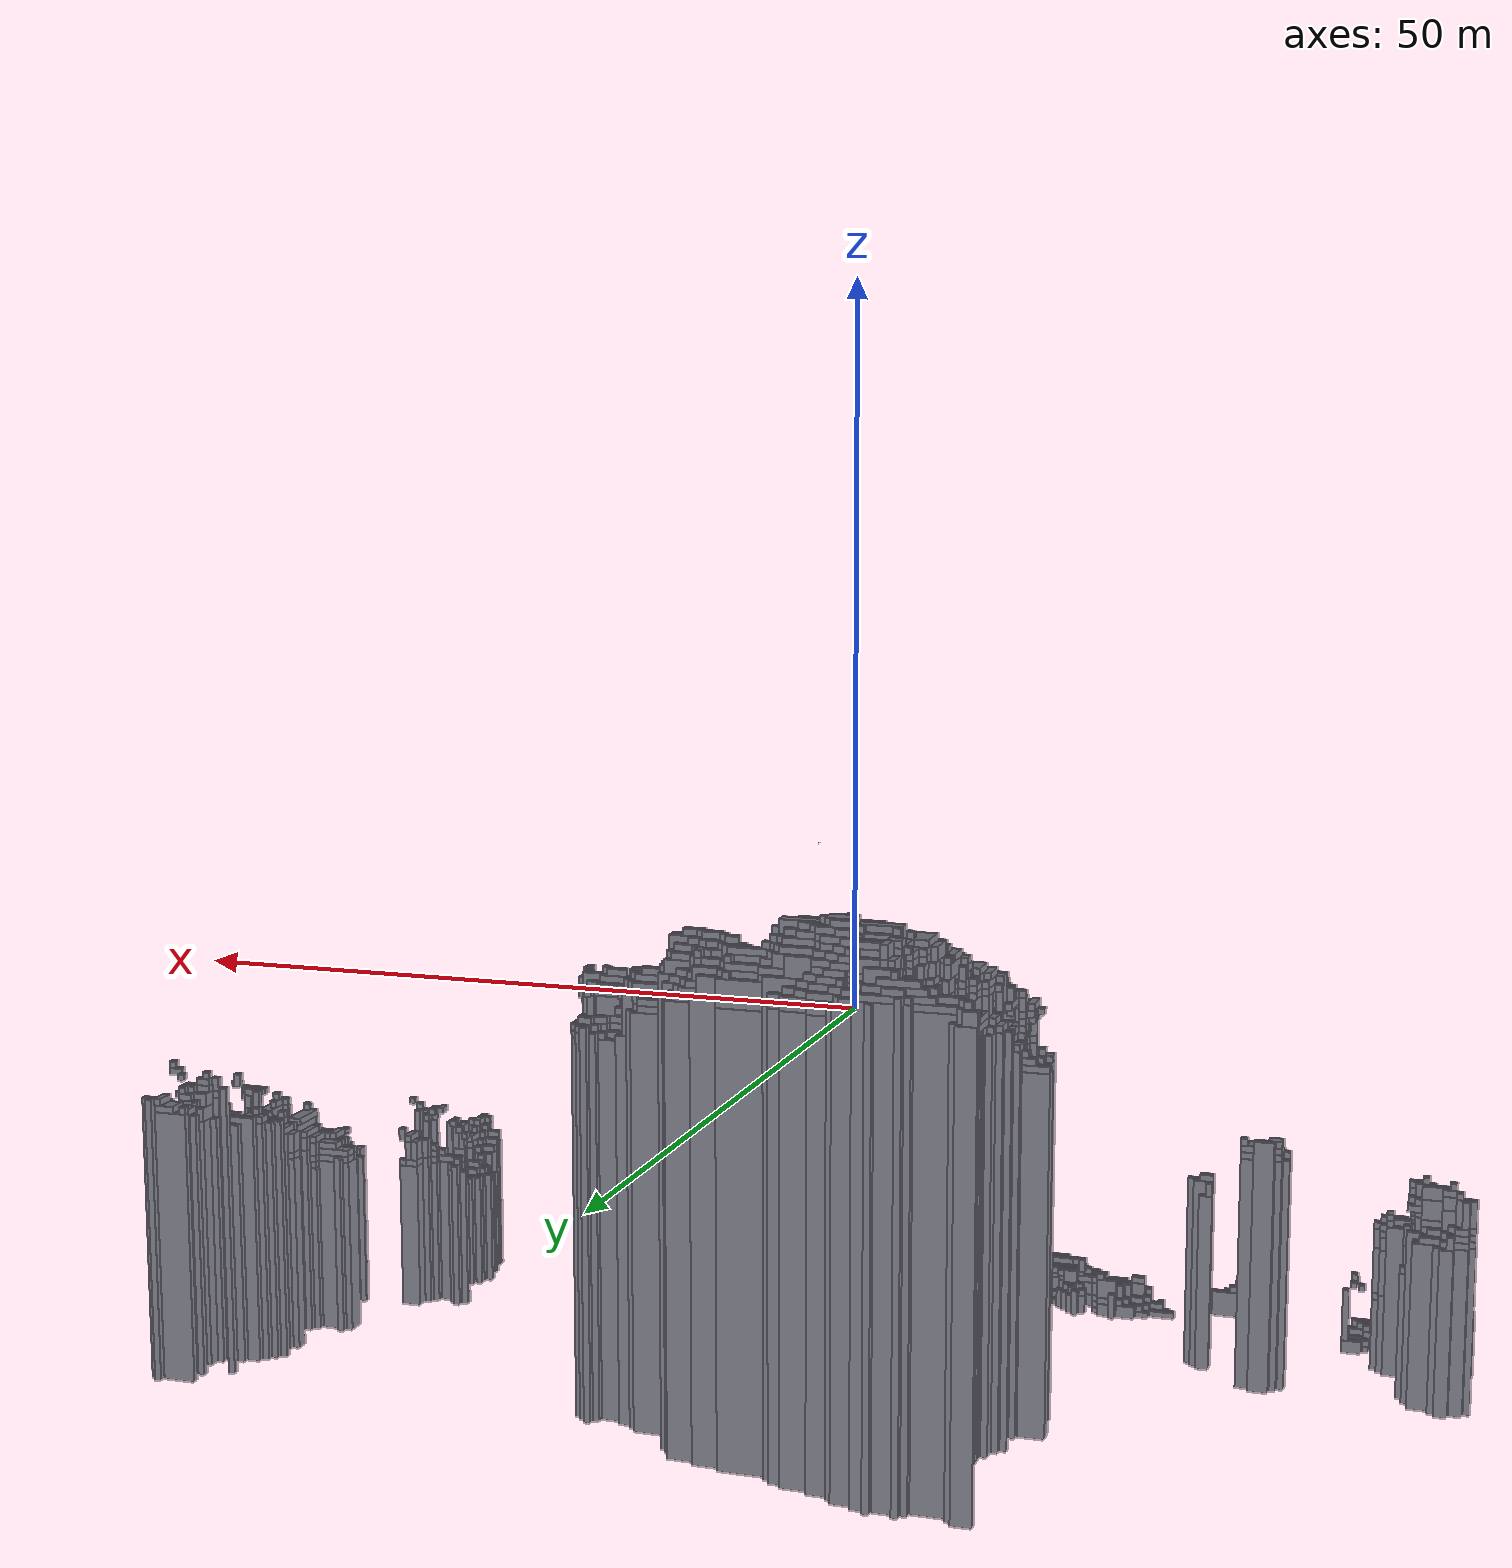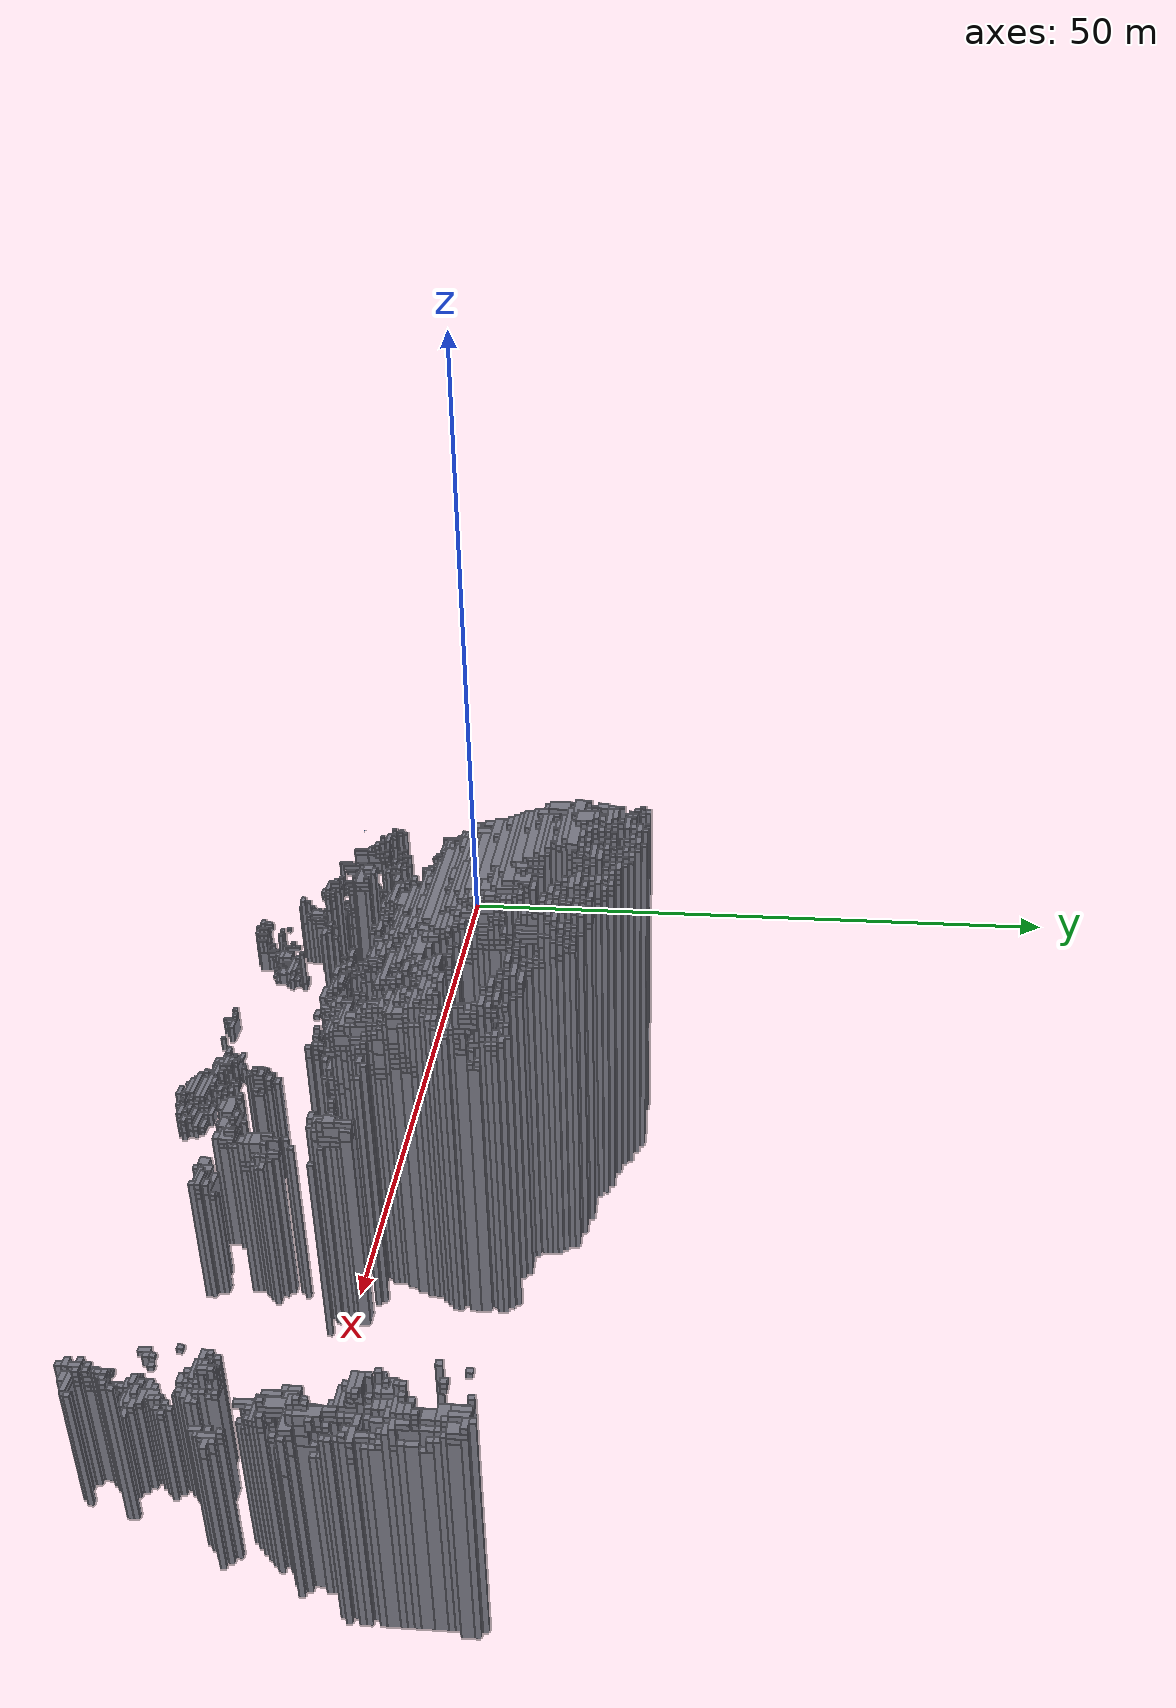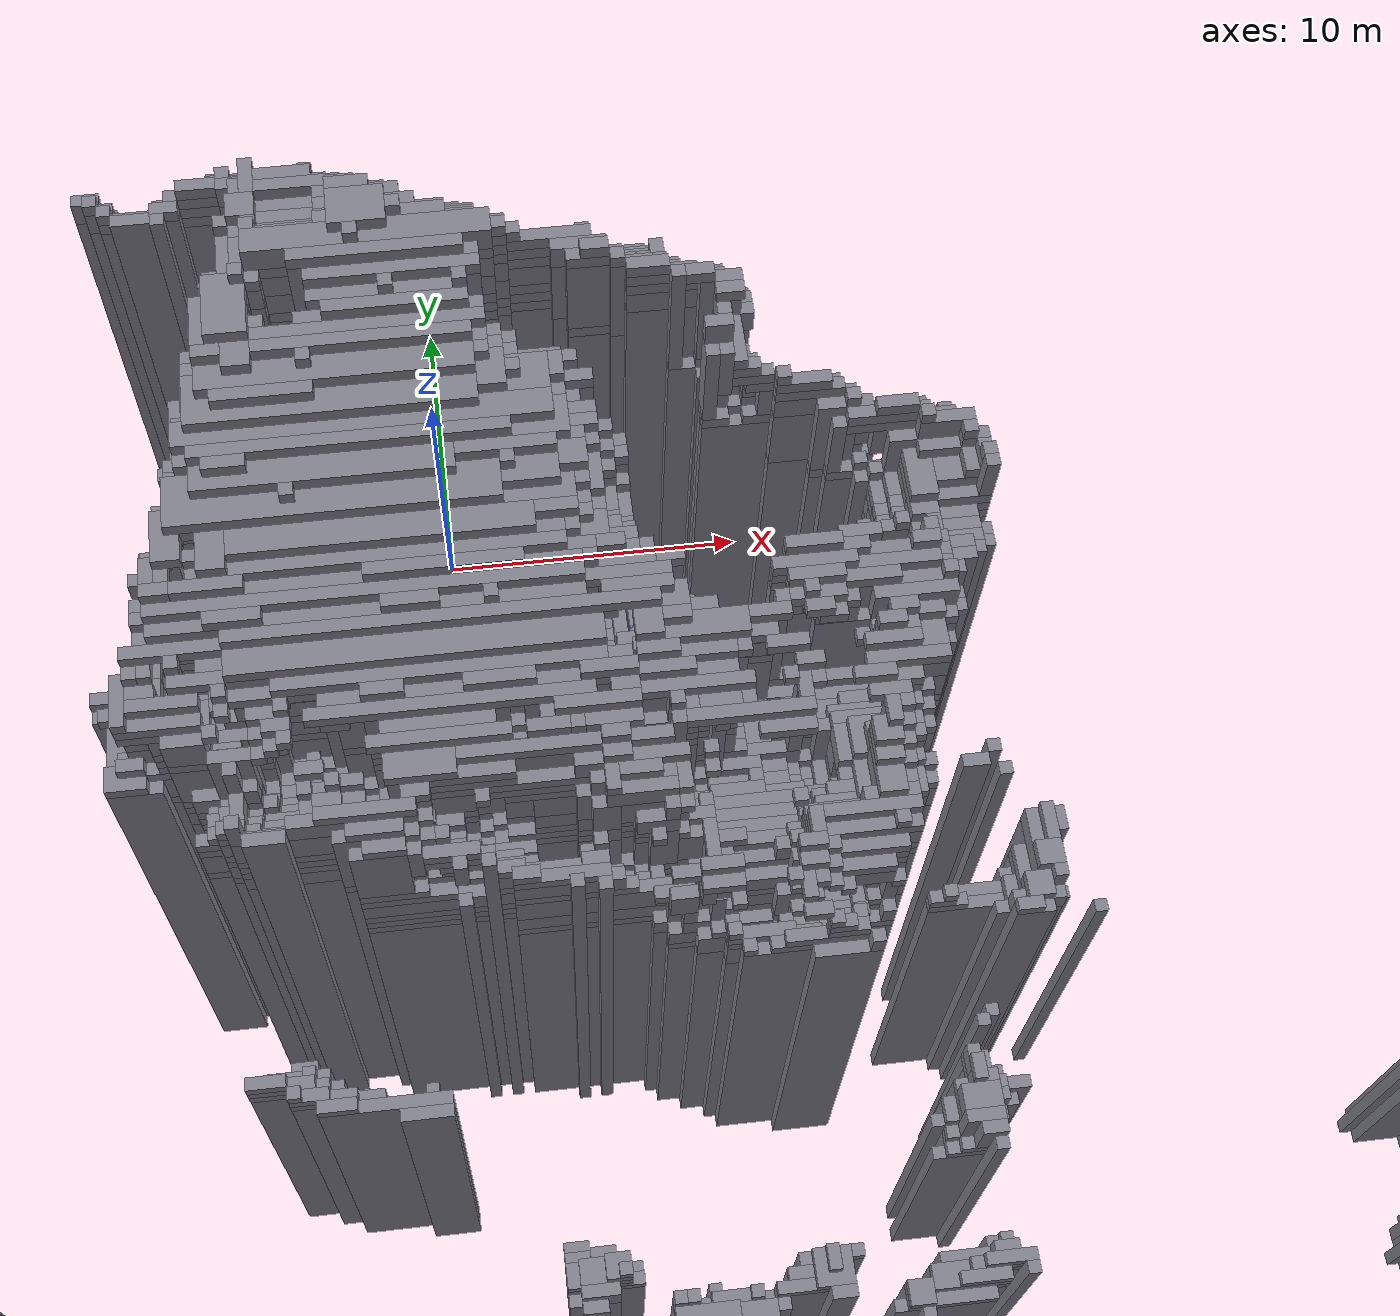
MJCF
<mujoco model="splat_collision">
  <compiler angle="radian"/>
  <option timestep="0.002"/>
  <visual><headlight ambient="0.4 0.4 0.4"/></visual>
  <asset>
    <!-- boxes need no assets -->
  </asset>
  <worldbody>
    <light pos="0 0 4" dir="0 0 -1"/>
    <geom name="vox0" type="box" pos="-39.233 -15.8933 -24.1855" size="2.25 0.25 6.25" rgba="0.5 0.5 0.55 1"/>
    <geom name="vox1" type="box" pos="-39.483 -15.8933 -17.6855" size="2 0.25 0.25" rgba="0.5 0.5 0.55 1"/>
    <geom name="vox2" type="box" pos="-40.233 -15.8933 -17.1855" size="1.25 0.25 0.25" rgba="0.5 0.5 0.55 1"/>
    <geom name="vox3" type="box" pos="-40.483 -15.8933 -16.6855" size="1 0.25 0.25" rgba="0.5 0.5 0.55 1"/>
    <geom name="vox4" type="box" pos="-40.733 -15.8933 -15.4355" size="0.75 0.25 1" rgba="0.5 0.5 0.55 1"/>
    <geom name="vox5" type="box" pos="-37.483 -23.8933 -27.9355" size="3.5 0.25 2.5" rgba="0.5 0.5 0.55 1"/>
    <geom name="vox6" type="box" pos="-38.983 -16.3933 -24.1855" size="2 0.25 6.25" rgba="0.5 0.5 0.55 1"/>
    <geom name="vox7" type="box" pos="-39.233 -16.3933 -17.6855" size="1.75 0.25 0.25" rgba="0.5 0.5 0.55 1"/>
    <geom name="vox8" type="box" pos="-39.483 -16.3933 -17.1855" size="1.5 0.25 0.25" rgba="0.5 0.5 0.55 1"/>
    <geom name="vox9" type="box" pos="-39.983 -16.3933 -16.1855" size="1 0.25 0.75" rgba="0.5 0.5 0.55 1"/>
    <geom name="vox10" type="box" pos="-39.733 -15.3933 -24.1855" size="1.25 0.25 6.25" rgba="0.5 0.5 0.55 1"/>
    <geom name="vox11" type="box" pos="-39.983 -15.3933 -17.6855" size="1 0.25 0.25" rgba="0.5 0.5 0.55 1"/>
    <geom name="vox12" type="box" pos="-40.233 -15.3933 -17.1855" size="0.75 0.25 0.25" rgba="0.5 0.5 0.55 1"/>
    <geom name="vox13" type="box" pos="-40.483 -15.3933 -16.6855" size="0.5 0.25 0.25" rgba="0.5 0.5 0.55 1"/>
    <geom name="vox14" type="box" pos="-40.733 -15.3933 -15.4355" size="0.25 0.25 1" rgba="0.5 0.5 0.55 1"/>
    <geom name="vox15" type="box" pos="-38.733 -26.3933 -27.6855" size="1.75 0.25 2.75" rgba="0.5 0.5 0.55 1"/>
    <geom name="vox16" type="box" pos="-37.483 -24.3933 -28.1855" size="3 0.25 2.25" rgba="0.5 0.5 0.55 1"/>
    <geom name="vox17" type="box" pos="-37.983 -24.3933 -25.6855" size="2.5 0.25 0.25" rgba="0.5 0.5 0.55 1"/>
    <geom name="vox18" type="box" pos="-36.983 -23.3933 -27.6855" size="3.5 0.25 2.75" rgba="0.5 0.5 0.55 1"/>
    <geom name="vox19" type="box" pos="-38.483 -16.8933 -23.9355" size="2 0.25 6.5" rgba="0.5 0.5 0.55 1"/>
    <geom name="vox20" type="box" pos="-38.983 -16.8933 -17.1855" size="1.5 0.25 0.25" rgba="0.5 0.5 0.55 1"/>
    <geom name="vox21" type="box" pos="-39.733 -16.3933 -14.9355" size="0.75 0.25 0.5" rgba="0.5 0.5 0.55 1"/>
    <geom name="vox22" type="box" pos="-40.233 -15.8933 -14.1855" size="0.25 0.25 0.25" rgba="0.5 0.5 0.55 1"/>
    <geom name="vox23" type="box" pos="-38.983 -27.8933 -27.6855" size="1 0.25 2.75" rgba="0.5 0.5 0.55 1"/>
    <geom name="vox24" type="box" pos="-38.483 -26.8933 -27.4355" size="1.5 0.25 3" rgba="0.5 0.5 0.55 1"/>
    <geom name="vox25" type="box" pos="-38.483 -25.3933 -27.9355" size="1.5 0.75 2.5" rgba="0.5 0.5 0.55 1"/>
    <geom name="vox26" type="box" pos="-36.983 -22.8933 -27.4355" size="3 0.25 3" rgba="0.5 0.5 0.55 1"/>
    <geom name="vox27" type="box" pos="-38.233 -22.3933 -27.6855" size="1.75 0.25 2.75" rgba="0.5 0.5 0.55 1"/>
    <geom name="vox28" type="box" pos="-39.233 -22.3933 -24.6855" size="0.75 0.25 0.25" rgba="0.5 0.5 0.55 1"/>
    <geom name="vox29" type="box" pos="-38.483 -21.8933 -27.9355" size="1.5 0.25 2.5" rgba="0.5 0.5 0.55 1"/>
    <geom name="vox30" type="box" pos="-39.233 -21.8933 -25.1855" size="0.75 0.25 0.25" rgba="0.5 0.5 0.55 1"/>
    <geom name="vox31" type="box" pos="-39.483 -21.8933 -24.6855" size="0.5 0.25 0.25" rgba="0.5 0.5 0.55 1"/>
    <geom name="vox32" type="box" pos="-39.483 -16.3933 -14.1855" size="0.5 0.25 0.25" rgba="0.5 0.5 0.55 1"/>
    <geom name="vox33" type="box" pos="-39.733 -16.3933 -13.6855" size="0.25 0.25 0.25" rgba="0.5 0.5 0.55 1"/>
    <geom name="vox34" type="box" pos="-39.483 -14.8933 -24.1855" size="0.5 0.25 6.25" rgba="0.5 0.5 0.55 1"/>
    <geom name="vox35" type="box" pos="-39.733 -14.8933 -17.4355" size="0.25 0.25 0.5" rgba="0.5 0.5 0.55 1"/>
    <geom name="vox36" type="box" pos="-38.733 -27.6433 -24.4355" size="0.75 0.5 0.5" rgba="0.5 0.5 0.55 1"/>
    <geom name="vox37" type="box" pos="-38.233 -27.3933 -27.6855" size="1.25 0.25 2.75" rgba="0.5 0.5 0.55 1"/>
    <geom name="vox38" type="box" pos="-38.233 -26.8933 -24.1855" size="1.25 0.25 0.25" rgba="0.5 0.5 0.55 1"/>
    <geom name="vox39" type="box" pos="-38.233 -26.3933 -24.6855" size="1.25 0.25 0.25" rgba="0.5 0.5 0.55 1"/>
    <geom name="vox40" type="box" pos="-38.233 -24.8933 -25.1855" size="1.25 1.25 0.25" rgba="0.5 0.5 0.55 1"/>
    <geom name="vox41" type="box" pos="-38.483 -23.3933 -24.6855" size="1 0.25 0.25" rgba="0.5 0.5 0.55 1"/>
    <geom name="vox42" type="box" pos="-39.233 -21.6433 -24.1855" size="0.25 0.5 0.25" rgba="0.5 0.5 0.55 1"/>
    <geom name="vox43" type="box" pos="-37.983 -21.3933 -27.6855" size="1.5 0.25 2.75" rgba="0.5 0.5 0.55 1"/>
    <geom name="vox44" type="box" pos="-38.983 -21.3933 -24.6855" size="0.5 0.25 0.25" rgba="0.5 0.5 0.55 1"/>
    <geom name="vox45" type="box" pos="-38.983 -21.3933 -23.6855" size="0.5 0.25 0.25" rgba="0.5 0.5 0.55 1"/>
    <geom name="vox46" type="box" pos="-38.483 -16.8933 -16.6855" size="1 0.25 0.25" rgba="0.5 0.5 0.55 1"/>
    <geom name="vox47" type="box" pos="-38.483 -16.8933 -14.4355" size="1 0.25 0.5" rgba="0.5 0.5 0.55 1"/>
    <geom name="vox48" type="box" pos="-37.983 -25.3933 -24.6855" size="1 0.75 0.25" rgba="0.5 0.5 0.55 1"/>
    <geom name="vox49" type="box" pos="-38.233 -24.1433 -24.6855" size="0.75 0.5 0.25" rgba="0.5 0.5 0.55 1"/>
    <geom name="vox50" type="box" pos="-38.483 -23.1433 -24.1855" size="0.5 0.5 0.25" rgba="0.5 0.5 0.55 1"/>
    <geom name="vox51" type="box" pos="-38.733 -22.3933 -24.1855" size="0.25 0.25 0.25" rgba="0.5 0.5 0.55 1"/>
    <geom name="vox52" type="box" pos="-38.733 -22.3933 -21.6855" size="0.25 0.25 0.25" rgba="0.5 0.5 0.55 1"/>
    <geom name="vox53" type="box" pos="-38.733 -21.1433 -22.9355" size="0.25 1 0.5" rgba="0.5 0.5 0.55 1"/>
    <geom name="vox54" type="box" pos="-38.733 -20.8933 -24.1855" size="0.25 0.75 0.25" rgba="0.5 0.5 0.55 1"/>
    <geom name="vox55" type="box" pos="-37.733 -20.6433 -27.4355" size="1.25 0.5 3" rgba="0.5 0.5 0.55 1"/>
    <geom name="vox56" type="box" pos="-37.733 -20.6433 -23.6855" size="1.25 0.5 0.25" rgba="0.5 0.5 0.55 1"/>
    <geom name="vox57" type="box" pos="-38.733 -20.8933 -22.1855" size="0.25 0.25 0.25" rgba="0.5 0.5 0.55 1"/>
    <geom name="vox58" type="box" pos="-37.733 -19.1433 -25.1855" size="1.25 0.5 5.25" rgba="0.5 0.5 0.55 1"/>
    <geom name="vox59" type="box" pos="-37.983 -19.1433 -19.6855" size="1 0.5 0.25" rgba="0.5 0.5 0.55 1"/>
    <geom name="vox60" type="box" pos="-37.733 -17.3933 -25.6855" size="1.25 0.25 4.75" rgba="0.5 0.5 0.55 1"/>
    <geom name="vox61" type="box" pos="-37.983 -17.3933 -18.1855" size="1 0.25 0.25" rgba="0.5 0.5 0.55 1"/>
    <geom name="vox62" type="box" pos="-38.233 -16.8933 -15.6855" size="0.75 0.25 0.75" rgba="0.5 0.5 0.55 1"/>
    <geom name="vox63" type="box" pos="-38.233 -27.3933 -23.6855" size="0.25 0.75 0.25" rgba="0.5 0.5 0.55 1"/>
    <geom name="vox64" type="box" pos="-37.983 -25.6433 -24.1855" size="0.5 1 0.25" rgba="0.5 0.5 0.55 1"/>
    <geom name="vox65" type="box" pos="-38.233 -24.1433 -24.1855" size="0.25 0.5 0.25" rgba="0.5 0.5 0.55 1"/>
    <geom name="vox66" type="box" pos="-37.983 -22.8933 -23.6855" size="0.5 0.25 0.25" rgba="0.5 0.5 0.55 1"/>
    <geom name="vox67" type="box" pos="-38.233 -22.8933 -21.1855" size="0.25 0.25 0.75" rgba="0.5 0.5 0.55 1"/>
    <geom name="vox68" type="box" pos="-37.983 -22.3933 -23.1855" size="0.5 0.25 0.25" rgba="0.5 0.5 0.55 1"/>
    <geom name="vox69" type="box" pos="-38.233 -22.3933 -22.6855" size="0.25 0.25 0.25" rgba="0.5 0.5 0.55 1"/>
    <geom name="vox70" type="box" pos="-37.483 -22.3933 -20.1855" size="1 0.25 0.25" rgba="0.5 0.5 0.55 1"/>
    <geom name="vox71" type="box" pos="-37.483 -20.6433 -23.1855" size="1 1 0.25" rgba="0.5 0.5 0.55 1"/>
    <geom name="vox72" type="box" pos="-37.483 -20.3933 -24.1855" size="1 0.75 0.25" rgba="0.5 0.5 0.55 1"/>
    <geom name="vox73" type="box" pos="-37.483 -20.3933 -22.6855" size="1 0.75 0.25" rgba="0.5 0.5 0.55 1"/>
    <geom name="vox74" type="box" pos="-37.233 -20.1433 -22.1855" size="1.25 0.5 0.25" rgba="0.5 0.5 0.55 1"/>
    <geom name="vox75" type="box" pos="-37.233 -19.8933 -27.4355" size="1.25 0.25 3" rgba="0.5 0.5 0.55 1"/>
    <geom name="vox76" type="box" pos="-37.233 -19.8933 -23.6855" size="1.25 0.25 0.25" rgba="0.5 0.5 0.55 1"/>
    <geom name="vox77" type="box" pos="-37.233 -19.8933 -20.6855" size="1.25 0.25 1.25" rgba="0.5 0.5 0.55 1"/>
    <geom name="vox78" type="box" pos="-37.733 -18.1433 -15.9355" size="0.75 1 0.5" rgba="0.5 0.5 0.55 1"/>
    <geom name="vox79" type="box" pos="-37.483 -18.1433 -25.6855" size="1 0.5 4.75" rgba="0.5 0.5 0.55 1"/>
    <geom name="vox80" type="box" pos="-37.483 -18.3933 -20.6855" size="1 0.25 0.25" rgba="0.5 0.5 0.55 1"/>
    <geom name="vox81" type="box" pos="-37.483 -17.3933 -20.6855" size="1 0.25 0.25" rgba="0.5 0.5 0.55 1"/>
    <geom name="vox82" type="box" pos="-37.733 -17.3933 -17.1855" size="0.75 0.25 0.75" rgba="0.5 0.5 0.55 1"/>
    <geom name="vox83" type="box" pos="-37.483 -17.3933 -15.1855" size="1 0.25 0.25" rgba="0.5 0.5 0.55 1"/>
    <geom name="vox84" type="box" pos="-37.733 -17.3933 -14.4355" size="0.75 0.25 0.5" rgba="0.5 0.5 0.55 1"/>
    <geom name="vox85" type="box" pos="-37.733 -30.3933 -28.4355" size="0.25 0.25 2" rgba="0.5 0.5 0.55 1"/>
    <geom name="vox86" type="box" pos="-37.483 -27.3933 -23.4355" size="0.5 0.25 1.5" rgba="0.5 0.5 0.55 1"/>
    <geom name="vox87" type="box" pos="-37.733 -26.8933 -23.1855" size="0.25 0.25 0.75" rgba="0.5 0.5 0.55 1"/>
    <geom name="vox88" type="box" pos="-37.733 -24.8933 -23.6855" size="0.25 0.25 0.25" rgba="0.5 0.5 0.55 1"/>
    <geom name="vox89" type="box" pos="-37.733 -22.6433 -24.1855" size="0.25 0.5 0.25" rgba="0.5 0.5 0.55 1"/>
    <geom name="vox90" type="box" pos="-37.733 -22.8933 -22.9355" size="0.25 0.25 0.5" rgba="0.5 0.5 0.55 1"/>
    <geom name="vox91" type="box" pos="-35.983 -22.8933 -20.4355" size="2 0.25 0.5" rgba="0.5 0.5 0.55 1"/>
    <geom name="vox92" type="box" pos="-37.233 -22.3933 -24.6855" size="0.75 0.25 0.25" rgba="0.5 0.5 0.55 1"/>
    <geom name="vox93" type="box" pos="-37.233 -22.3933 -23.6855" size="0.75 0.25 0.25" rgba="0.5 0.5 0.55 1"/>
    <geom name="vox94" type="box" pos="-37.233 -22.3933 -19.6855" size="0.75 0.25 0.25" rgba="0.5 0.5 0.55 1"/>
    <geom name="vox95" type="box" pos="-37.733 -22.3933 -18.1855" size="0.25 0.25 1.25" rgba="0.5 0.5 0.55 1"/>
    <geom name="vox96" type="box" pos="-37.483 -21.8933 -25.1855" size="0.5 0.25 0.25" rgba="0.5 0.5 0.55 1"/>
    <geom name="vox97" type="box" pos="-37.483 -21.8933 -23.1855" size="0.5 0.25 0.25" rgba="0.5 0.5 0.55 1"/>
    <geom name="vox98" type="box" pos="-37.733 -21.1433 -19.6855" size="0.25 1 0.25" rgba="0.5 0.5 0.55 1"/>
    <geom name="vox99" type="box" pos="-37.733 -21.6433 -17.4355" size="0.25 0.5 0.5" rgba="0.5 0.5 0.55 1"/>
    <geom name="vox100" type="box" pos="-37.233 -21.3933 -24.1855" size="0.75 0.25 0.75" rgba="0.5 0.5 0.55 1"/>
    <geom name="vox101" type="box" pos="-37.233 -21.3933 -22.6855" size="0.75 0.25 0.25" rgba="0.5 0.5 0.55 1"/>
    <geom name="vox102" type="box" pos="-37.233 -20.8933 -20.1855" size="0.75 0.75 0.25" rgba="0.5 0.5 0.55 1"/>
    <geom name="vox103" type="box" pos="-37.233 -20.8933 -21.4355" size="0.75 0.25 1" rgba="0.5 0.5 0.55 1"/>
    <geom name="vox104" type="box" pos="-36.983 -20.3933 -21.1855" size="1 0.25 0.75" rgba="0.5 0.5 0.55 1"/>
    <geom name="vox105" type="box" pos="-37.483 -19.8933 -15.9355" size="0.5 0.75 0.5" rgba="0.5 0.5 0.55 1"/>
    <geom name="vox106" type="box" pos="-37.483 -19.8933 -19.1855" size="0.5 0.25 0.25" rgba="0.5 0.5 0.55 1"/>
    <geom name="vox107" type="box" pos="-37.733 -19.1433 -19.1855" size="0.25 0.5 0.25" rgba="0.5 0.5 0.55 1"/>
    <geom name="vox108" type="box" pos="-37.483 -18.3933 -16.9355" size="0.5 0.75 0.5" rgba="0.5 0.5 0.55 1"/>
    <geom name="vox109" type="box" pos="-37.483 -18.3933 -15.1855" size="0.5 0.75 0.25" rgba="0.5 0.5 0.55 1"/>
    <geom name="vox110" type="box" pos="-37.483 -17.8933 -17.6855" size="0.5 0.25 0.25" rgba="0.5 0.5 0.55 1"/>
    <geom name="vox111" type="box" pos="-37.233 -17.8933 -14.6855" size="0.75 0.25 0.25" rgba="0.5 0.5 0.55 1"/>
    <geom name="vox112" type="box" pos="-37.733 -17.3933 -13.6855" size="0.25 0.25 0.25" rgba="0.5 0.5 0.55 1"/>
    <geom name="vox113" type="box" pos="-36.233 -32.1433 -29.1855" size="1.25 0.5 1.25" rgba="0.5 0.5 0.55 1"/>
    <geom name="vox114" type="box" pos="-36.233 -32.3933 -27.1855" size="1.25 0.25 0.75" rgba="0.5 0.5 0.55 1"/>
    <geom name="vox115" type="box" pos="-36.483 -32.3933 -26.1855" size="1 0.25 0.25" rgba="0.5 0.5 0.55 1"/>
    <geom name="vox116" type="box" pos="-36.733 -32.3933 -25.6855" size="0.75 0.25 0.25" rgba="0.5 0.5 0.55 1"/>
    <geom name="vox117" type="box" pos="-36.983 -32.3933 -25.1855" size="0.5 0.25 0.25" rgba="0.5 0.5 0.55 1"/>
    <geom name="vox118" type="box" pos="-36.983 -31.8933 -26.9355" size="0.5 0.25 1" rgba="0.5 0.5 0.55 1"/>
    <geom name="vox119" type="box" pos="-35.733 -22.8933 -19.6855" size="1.75 0.25 0.25" rgba="0.5 0.5 0.55 1"/>
    <geom name="vox120" type="box" pos="-36.983 -22.3933 -24.1855" size="0.5 0.25 0.25" rgba="0.5 0.5 0.55 1"/>
    <geom name="vox121" type="box" pos="-37.233 -21.8933 -24.1855" size="0.25 0.25 0.75" rgba="0.5 0.5 0.55 1"/>
    <geom name="vox122" type="box" pos="-37.233 -21.8933 -20.1855" size="0.25 0.25 0.25" rgba="0.5 0.5 0.55 1"/>
    <geom name="vox123" type="box" pos="-37.233 -20.6433 -17.1855" size="0.25 1.5 0.25" rgba="0.5 0.5 0.55 1"/>
    <geom name="vox124" type="box" pos="-36.983 -21.3933 -21.4355" size="0.5 0.25 1" rgba="0.5 0.5 0.55 1"/>
    <geom name="vox125" type="box" pos="-36.733 -20.3933 -19.6855" size="0.75 0.25 0.25" rgba="0.5 0.5 0.55 1"/>
    <geom name="vox126" type="box" pos="-37.233 -20.1433 -17.6855" size="0.25 0.5 0.25" rgba="0.5 0.5 0.55 1"/>
    <geom name="vox127" type="box" pos="-37.233 -19.8933 -16.6855" size="0.25 0.75 0.25" rgba="0.5 0.5 0.55 1"/>
    <geom name="vox128" type="box" pos="-37.233 -19.8933 -15.1855" size="0.25 0.75 0.25" rgba="0.5 0.5 0.55 1"/>
    <geom name="vox129" type="box" pos="-37.233 -19.8933 -18.4355" size="0.25 0.25 0.5" rgba="0.5 0.5 0.55 1"/>
    <geom name="vox130" type="box" pos="-36.983 -18.3933 -20.1855" size="0.5 0.25 0.25" rgba="0.5 0.5 0.55 1"/>
    <geom name="vox131" type="box" pos="-37.233 -18.3933 -19.6855" size="0.25 0.25 0.25" rgba="0.5 0.5 0.55 1"/>
    <geom name="vox132" type="box" pos="-37.233 -18.3933 -14.6855" size="0.25 0.25 0.25" rgba="0.5 0.5 0.55 1"/>
    <geom name="vox133" type="box" pos="-36.733 -17.8933 -20.6855" size="0.75 0.25 0.25" rgba="0.5 0.5 0.55 1"/>
    <geom name="vox134" type="box" pos="-36.983 -17.8933 -14.1855" size="0.5 0.25 0.25" rgba="0.5 0.5 0.55 1"/>
    <geom name="vox135" type="box" pos="-36.983 -17.3933 -20.1855" size="0.5 0.25 0.25" rgba="0.5 0.5 0.55 1"/>
    <geom name="vox136" type="box" pos="-37.233 -17.3933 -19.1855" size="0.25 0.25 0.75" rgba="0.5 0.5 0.55 1"/>
    <geom name="vox137" type="box" pos="-36.983 -16.8933 -15.6855" size="0.5 0.25 0.25" rgba="0.5 0.5 0.55 1"/>
    <geom name="vox138" type="box" pos="-37.233 -16.8933 -15.1855" size="0.25 0.25 0.25" rgba="0.5 0.5 0.55 1"/>
    <geom name="vox139" type="box" pos="-36.483 -32.8933 -28.1855" size="0.5 0.25 2.25" rgba="0.5 0.5 0.55 1"/>
    <geom name="vox140" type="box" pos="-36.733 -32.8933 -25.6855" size="0.25 0.25 0.25" rgba="0.5 0.5 0.55 1"/>
    <geom name="vox141" type="box" pos="-36.483 -31.8933 -25.6855" size="0.5 0.25 0.25" rgba="0.5 0.5 0.55 1"/>
    <geom name="vox142" type="box" pos="-36.733 -31.6433 -25.1855" size="0.25 0.5 0.25" rgba="0.5 0.5 0.55 1"/>
    <geom name="vox143" type="box" pos="-35.983 -31.3933 -29.4355" size="1 0.25 1" rgba="0.5 0.5 0.55 1"/>
    <geom name="vox144" type="box" pos="-36.733 -31.3933 -28.1855" size="0.25 0.25 0.25" rgba="0.5 0.5 0.55 1"/>
    <geom name="vox145" type="box" pos="-36.733 -31.3933 -25.6855" size="0.25 0.25 0.25" rgba="0.5 0.5 0.55 1"/>
    <geom name="vox146" type="box" pos="-36.733 -30.3933 -28.4355" size="0.25 0.25 2" rgba="0.5 0.5 0.55 1"/>
    <geom name="vox147" type="box" pos="-36.733 -24.8933 -27.9355" size="0.25 0.25 2.5" rgba="0.5 0.5 0.55 1"/>
    <geom name="vox148" type="box" pos="-36.733 -24.1433 -25.1855" size="0.25 0.5 0.25" rgba="0.5 0.5 0.55 1"/>
    <geom name="vox149" type="box" pos="-35.233 -23.3933 -20.1855" size="1.75 0.25 0.75" rgba="0.5 0.5 0.55 1"/>
    <geom name="vox150" type="box" pos="-35.483 -22.8933 -19.1855" size="1.5 0.25 0.25" rgba="0.5 0.5 0.55 1"/>
    <geom name="vox151" type="box" pos="-36.733 -22.3933 -18.9355" size="0.25 0.25 0.5" rgba="0.5 0.5 0.55 1"/>
    <geom name="vox152" type="box" pos="-36.733 -21.1433 -19.6855" size="0.25 0.5 0.25" rgba="0.5 0.5 0.55 1"/>
    <geom name="vox153" type="box" pos="-36.733 -21.1433 -17.6855" size="0.25 0.5 0.25" rgba="0.5 0.5 0.55 1"/>
    <geom name="vox154" type="box" pos="-36.483 -20.3933 -18.9355" size="0.5 0.25 0.5" rgba="0.5 0.5 0.55 1"/>
    <geom name="vox155" type="box" pos="-36.733 -20.3933 -18.1855" size="0.25 0.25 0.25" rgba="0.5 0.5 0.55 1"/>
    <geom name="vox156" type="box" pos="-36.733 -19.8933 -16.9355" size="0.25 0.25 0.5" rgba="0.5 0.5 0.55 1"/>
    <geom name="vox157" type="box" pos="-36.733 -19.3933 -16.6855" size="0.25 0.25 0.25" rgba="0.5 0.5 0.55 1"/>
    <geom name="vox158" type="box" pos="-36.733 -17.8933 -20.1855" size="0.25 0.25 0.25" rgba="0.5 0.5 0.55 1"/>
    <geom name="vox159" type="box" pos="-36.733 -17.8933 -15.1855" size="0.25 0.25 0.25" rgba="0.5 0.5 0.55 1"/>
    <geom name="vox160" type="box" pos="-36.733 -17.3933 -15.6855" size="0.25 0.25 0.25" rgba="0.5 0.5 0.55 1"/>
    <geom name="vox161" type="box" pos="-36.233 -30.8933 -29.4355" size="0.25 0.25 1" rgba="0.5 0.5 0.55 1"/>
    <geom name="vox162" type="box" pos="-36.233 -29.8933 -28.9355" size="0.25 0.25 1.5" rgba="0.5 0.5 0.55 1"/>
    <geom name="vox163" type="box" pos="-35.983 -23.8933 -25.1855" size="0.5 0.25 0.25" rgba="0.5 0.5 0.55 1"/>
    <geom name="vox164" type="box" pos="-34.983 -23.3933 -24.6855" size="1.5 0.25 0.25" rgba="0.5 0.5 0.55 1"/>
    <geom name="vox165" type="box" pos="-34.983 -23.3933 -19.1855" size="1.5 0.25 0.25" rgba="0.5 0.5 0.55 1"/>
    <geom name="vox166" type="box" pos="-35.233 -22.8933 -22.6855" size="1.25 0.25 1.75" rgba="0.5 0.5 0.55 1"/>
    <geom name="vox167" type="box" pos="-35.483 -22.8933 -18.6855" size="1 0.25 0.25" rgba="0.5 0.5 0.55 1"/>
    <geom name="vox168" type="box" pos="-36.233 -20.3933 -26.4355" size="0.25 0.25 4" rgba="0.5 0.5 0.55 1"/>
    <geom name="vox169" type="box" pos="-36.233 -20.3933 -20.1855" size="0.25 0.25 0.25" rgba="0.5 0.5 0.55 1"/>
    <geom name="vox170" type="box" pos="-36.233 -19.8933 -24.1855" size="0.25 0.25 0.25" rgba="0.5 0.5 0.55 1"/>
    <geom name="vox171" type="box" pos="-36.233 -19.8933 -22.9355" size="0.25 0.25 0.5" rgba="0.5 0.5 0.55 1"/>
    <geom name="vox172" type="box" pos="-36.233 -19.8933 -18.6855" size="0.25 0.25 0.75" rgba="0.5 0.5 0.55 1"/>
    <geom name="vox173" type="box" pos="-36.233 -17.8933 -25.6855" size="0.25 0.25 4.75" rgba="0.5 0.5 0.55 1"/>
    <geom name="vox174" type="box" pos="-35.733 -31.8933 -26.1855" size="0.25 0.25 0.25" rgba="0.5 0.5 0.55 1"/>
    <geom name="vox175" type="box" pos="-33.983 -29.1433 -29.6855" size="2 0.5 0.75" rgba="0.5 0.5 0.55 1"/>
    <geom name="vox176" type="box" pos="-34.733 -29.1433 -28.6855" size="1.25 0.5 0.25" rgba="0.5 0.5 0.55 1"/>
    <geom name="vox177" type="box" pos="-34.983 -29.1433 -28.1855" size="1 0.5 0.25" rgba="0.5 0.5 0.55 1"/>
    <geom name="vox178" type="box" pos="-35.733 -29.1433 -27.6855" size="0.25 0.5 0.25" rgba="0.5 0.5 0.55 1"/>
    <geom name="vox179" type="box" pos="-35.733 -28.8933 -25.1855" size="0.25 0.25 0.25" rgba="0.5 0.5 0.55 1"/>
    <geom name="vox180" type="box" pos="-35.733 -24.3933 -23.1855" size="0.25 0.25 0.25" rgba="0.5 0.5 0.55 1"/>
    <geom name="vox181" type="box" pos="-35.733 -23.8933 -24.6855" size="0.25 0.25 0.25" rgba="0.5 0.5 0.55 1"/>
    <geom name="vox182" type="box" pos="-34.733 -23.3933 -22.6855" size="1.25 0.25 1.75" rgba="0.5 0.5 0.55 1"/>
    <geom name="vox183" type="box" pos="-34.983 -23.3933 -18.6855" size="1 0.25 0.25" rgba="0.5 0.5 0.55 1"/>
    <geom name="vox184" type="box" pos="-35.233 -22.3933 -24.6855" size="0.75 0.25 5.75" rgba="0.5 0.5 0.55 1"/>
    <geom name="vox185" type="box" pos="-35.233 -31.8933 -27.1855" size="0.25 0.25 0.75" rgba="0.5 0.5 0.55 1"/>
    <geom name="vox186" type="box" pos="-35.233 -31.1433 -28.1855" size="0.25 0.5 0.25" rgba="0.5 0.5 0.55 1"/>
    <geom name="vox187" type="box" pos="-35.233 -30.8933 -29.4355" size="0.25 0.25 1" rgba="0.5 0.5 0.55 1"/>
    <geom name="vox188" type="box" pos="-33.733 -29.8933 -30.1855" size="1.75 0.25 0.25" rgba="0.5 0.5 0.55 1"/>
    <geom name="vox189" type="box" pos="-34.233 -29.8933 -29.6855" size="1.25 0.25 0.25" rgba="0.5 0.5 0.55 1"/>
    <geom name="vox190" type="box" pos="-34.483 -29.8933 -29.1855" size="1 0.25 0.25" rgba="0.5 0.5 0.55 1"/>
    <geom name="vox191" type="box" pos="-34.733 -29.8933 -28.4355" size="0.75 0.25 0.5" rgba="0.5 0.5 0.55 1"/>
    <geom name="vox192" type="box" pos="-35.233 -24.8933 -28.1855" size="0.25 0.25 2.25" rgba="0.5 0.5 0.55 1"/>
    <geom name="vox193" type="box" pos="-34.733 -23.8933 -23.1855" size="0.75 0.25 0.25" rgba="0.5 0.5 0.55 1"/>
    <geom name="vox194" type="box" pos="-34.983 -23.8933 -22.6855" size="0.5 0.25 0.25" rgba="0.5 0.5 0.55 1"/>
    <geom name="vox195" type="box" pos="-35.233 -23.8933 -20.4355" size="0.25 0.25 0.5" rgba="0.5 0.5 0.55 1"/>
    <geom name="vox196" type="box" pos="-34.733 -30.3933 -29.1855" size="0.25 0.25 1.25" rgba="0.5 0.5 0.55 1"/>
    <geom name="vox197" type="box" pos="-33.233 -28.3933 -29.4355" size="1.75 0.25 1" rgba="0.5 0.5 0.55 1"/>
    <geom name="vox198" type="box" pos="-34.483 -23.8933 -19.4355" size="0.5 0.25 0.5" rgba="0.5 0.5 0.55 1"/>
    <geom name="vox199" type="box" pos="-34.733 -22.6433 -18.1855" size="0.25 0.5 0.25" rgba="0.5 0.5 0.55 1"/>
    <geom name="vox200" type="box" pos="-34.733 -22.3933 -18.6855" size="0.25 0.25 0.25" rgba="0.5 0.5 0.55 1"/>
    <geom name="vox201" type="box" pos="-32.733 -27.8933 -29.6855" size="1.75 0.25 0.75" rgba="0.5 0.5 0.55 1"/>
    <geom name="vox202" type="box" pos="-33.233 -27.8933 -28.6855" size="1.25 0.25 0.25" rgba="0.5 0.5 0.55 1"/>
    <geom name="vox203" type="box" pos="-34.233 -27.8933 -28.1855" size="0.25 0.25 0.25" rgba="0.5 0.5 0.55 1"/>
    <geom name="vox204" type="box" pos="-34.233 -23.8933 -24.4355" size="0.25 0.25 1" rgba="0.5 0.5 0.55 1"/>
    <geom name="vox205" type="box" pos="-33.483 -30.3933 -30.1855" size="0.5 0.25 0.25" rgba="0.5 0.5 0.55 1"/>
    <geom name="vox206" type="box" pos="-33.733 -30.3933 -29.6855" size="0.25 0.25 0.25" rgba="0.5 0.5 0.55 1"/>
    <geom name="vox207" type="box" pos="-32.733 -27.3933 -29.9355" size="1.25 0.25 0.5" rgba="0.5 0.5 0.55 1"/>
    <geom name="vox208" type="box" pos="-33.233 -27.3933 -29.1855" size="0.75 0.25 0.25" rgba="0.5 0.5 0.55 1"/>
    <geom name="vox209" type="box" pos="-33.233 -28.8933 -28.6855" size="0.25 0.25 0.25" rgba="0.5 0.5 0.55 1"/>
    <geom name="vox210" type="box" pos="-32.733 -27.3933 -28.6855" size="0.25 0.25 0.25" rgba="0.5 0.5 0.55 1"/>
    <geom name="vox211" type="box" pos="-32.233 -26.8933 -30.1855" size="0.75 0.25 0.25" rgba="0.5 0.5 0.55 1"/>
    <geom name="vox212" type="box" pos="-32.733 -26.8933 -29.6855" size="0.25 0.25 0.25" rgba="0.5 0.5 0.55 1"/>
    <geom name="vox213" type="box" pos="-32.233 -27.8933 -25.6855" size="0.25 0.25 0.25" rgba="0.5 0.5 0.55 1"/>
    <geom name="vox214" type="box" pos="-31.733 -26.3933 -29.9355" size="0.75 0.25 0.5" rgba="0.5 0.5 0.55 1"/>
    <geom name="vox215" type="box" pos="-31.733 -27.3933 -25.1855" size="0.25 0.75 0.25" rgba="0.5 0.5 0.55 1"/>
    <geom name="vox216" type="box" pos="-31.733 -27.3933 -24.6855" size="0.25 0.25 0.25" rgba="0.5 0.5 0.55 1"/>
    <geom name="vox217" type="box" pos="-31.233 -26.3933 -27.4355" size="0.25 0.25 2" rgba="0.5 0.5 0.55 1"/>
    <geom name="vox218" type="box" pos="-26.233 -17.1433 -21.6855" size="1.75 0.5 8.75" rgba="0.5 0.5 0.55 1"/>
    <geom name="vox219" type="box" pos="-26.233 -17.3933 -12.6855" size="1.75 0.25 0.25" rgba="0.5 0.5 0.55 1"/>
    <geom name="vox220" type="box" pos="-26.483 -17.8933 -21.4355" size="1 0.25 9" rgba="0.5 0.5 0.55 1"/>
    <geom name="vox221" type="box" pos="-25.983 -16.8933 -12.1855" size="1.5 0.75 0.25" rgba="0.5 0.5 0.55 1"/>
    <geom name="vox222" type="box" pos="-25.983 -16.6433 -12.6855" size="1.5 0.5 0.25" rgba="0.5 0.5 0.55 1"/>
    <geom name="vox223" type="box" pos="-26.983 -16.6433 -11.6855" size="0.5 0.5 0.25" rgba="0.5 0.5 0.55 1"/>
    <geom name="vox224" type="box" pos="-25.983 -16.3933 -21.6855" size="1.5 0.25 8.75" rgba="0.5 0.5 0.55 1"/>
    <geom name="vox225" type="box" pos="-26.233 -15.8933 -20.9355" size="0.75 0.25 9.5" rgba="0.5 0.5 0.55 1"/>
    <geom name="vox226" type="box" pos="-25.733 -17.8933 -12.1855" size="0.25 0.25 0.25" rgba="0.5 0.5 0.55 1"/>
    <geom name="vox227" type="box" pos="-24.733 -16.3933 -11.6855" size="0.25 0.25 0.25" rgba="0.5 0.5 0.55 1"/>
    <geom name="vox228" type="box" pos="-21.233 -31.8933 -29.4355" size="1.25 0.25 1" rgba="0.5 0.5 0.55 1"/>
    <geom name="vox229" type="box" pos="-21.983 -31.8933 -28.1855" size="0.5 0.25 0.25" rgba="0.5 0.5 0.55 1"/>
    <geom name="vox230" type="box" pos="-22.233 -31.8933 -27.6855" size="0.25 0.25 0.25" rgba="0.5 0.5 0.55 1"/>
    <geom name="vox231" type="box" pos="-21.733 -32.6433 -29.4355" size="0.25 0.5 1" rgba="0.5 0.5 0.55 1"/>
    <geom name="vox232" type="box" pos="-21.233 -19.8933 -23.1855" size="0.75 0.25 7.25" rgba="0.5 0.5 0.55 1"/>
    <geom name="vox233" type="box" pos="-21.483 -19.8933 -15.6855" size="0.5 0.25 0.25" rgba="0.5 0.5 0.55 1"/>
    <geom name="vox234" type="box" pos="-21.483 -19.3933 -23.6855" size="0.5 0.25 6.75" rgba="0.5 0.5 0.55 1"/>
    <geom name="vox235" type="box" pos="-21.733 -19.3933 -16.4355" size="0.25 0.25 0.5" rgba="0.5 0.5 0.55 1"/>
    <geom name="vox236" type="box" pos="-21.233 -32.3933 -29.4355" size="0.25 0.25 1" rgba="0.5 0.5 0.55 1"/>
    <geom name="vox237" type="box" pos="-20.733 -20.3933 -23.1855" size="0.75 0.25 7.25" rgba="0.5 0.5 0.55 1"/>
    <geom name="vox238" type="box" pos="-18.733 -32.3933 -29.6855" size="0.25 0.25 0.75" rgba="0.5 0.5 0.55 1"/>
    <geom name="vox239" type="box" pos="-14.483 -29.8933 -30.1855" size="3 0.25 0.25" rgba="0.5 0.5 0.55 1"/>
    <geom name="vox240" type="box" pos="-13.983 -30.3933 -30.1855" size="3 0.25 0.25" rgba="0.5 0.5 0.55 1"/>
    <geom name="vox241" type="box" pos="-16.233 -30.8933 -29.9355" size="0.25 0.25 0.5" rgba="0.5 0.5 0.55 1"/>
    <geom name="vox242" type="box" pos="-13.733 -30.3933 -29.6855" size="2.75 0.25 0.25" rgba="0.5 0.5 0.55 1"/>
    <geom name="vox243" type="box" pos="-9.233 -30.8933 -29.9355" size="6.25 0.25 0.5" rgba="0.5 0.5 0.55 1"/>
    <geom name="vox244" type="box" pos="-11.733 -30.8933 -28.9355" size="3.75 0.25 0.5" rgba="0.5 0.5 0.55 1"/>
    <geom name="vox245" type="box" pos="-13.233 -30.3933 -29.1855" size="2.25 0.25 0.25" rgba="0.5 0.5 0.55 1"/>
    <geom name="vox246" type="box" pos="-13.483 -29.8933 -29.6855" size="2 0.25 0.25" rgba="0.5 0.5 0.55 1"/>
    <geom name="vox247" type="box" pos="-13.233 -29.3933 -30.1855" size="2.25 0.25 0.25" rgba="0.5 0.5 0.55 1"/>
    <geom name="vox248" type="box" pos="-8.733 -31.8933 -29.9355" size="6.25 0.25 0.5" rgba="0.5 0.5 0.55 1"/>
    <geom name="vox249" type="box" pos="-14.233 -31.6433 -29.1855" size="0.75 0.5 0.25" rgba="0.5 0.5 0.55 1"/>
    <geom name="vox250" type="box" pos="-8.983 -31.3933 -29.9355" size="6 0.25 0.5" rgba="0.5 0.5 0.55 1"/>
    <geom name="vox251" type="box" pos="-12.983 -30.3933 -28.4355" size="2 0.25 0.5" rgba="0.5 0.5 0.55 1"/>
    <geom name="vox252" type="box" pos="-14.483 -30.3933 -27.6855" size="0.5 0.25 0.25" rgba="0.5 0.5 0.55 1"/>
    <geom name="vox253" type="box" pos="-13.233 -29.8933 -29.1855" size="1.75 0.25 0.25" rgba="0.5 0.5 0.55 1"/>
    <geom name="vox254" type="box" pos="-12.983 -29.3933 -29.6855" size="2 0.25 0.25" rgba="0.5 0.5 0.55 1"/>
    <geom name="vox255" type="box" pos="-12.983 -28.8933 -29.9355" size="1.5 0.25 0.5" rgba="0.5 0.5 0.55 1"/>
    <geom name="vox256" type="box" pos="-12.733 -29.8933 -28.4355" size="1.25 0.25 0.5" rgba="0.5 0.5 0.55 1"/>
    <geom name="vox257" type="box" pos="-12.483 -29.3933 -29.1855" size="1.5 0.25 0.25" rgba="0.5 0.5 0.55 1"/>
    <geom name="vox258" type="box" pos="-8.233 -31.3933 -28.9355" size="5.25 0.25 0.5" rgba="0.5 0.5 0.55 1"/>
    <geom name="vox259" type="box" pos="-10.733 -30.8933 -28.1855" size="2.75 0.25 0.25" rgba="0.5 0.5 0.55 1"/>
    <geom name="vox260" type="box" pos="-12.233 -29.3933 -28.4355" size="1.25 0.25 0.5" rgba="0.5 0.5 0.55 1"/>
    <geom name="vox261" type="box" pos="-12.483 -28.8933 -29.1855" size="1 0.25 0.25" rgba="0.5 0.5 0.55 1"/>
    <geom name="vox262" type="box" pos="-2.483 -2.14327 -17.1855" size="11 0.5 13.25" rgba="0.5 0.5 0.55 1"/>
    <geom name="vox263" type="box" pos="-2.483 -1.89327 -3.6855" size="11 0.25 0.25" rgba="0.5 0.5 0.55 1"/>
    <geom name="vox264" type="box" pos="-12.233 -28.8933 -28.1855" size="0.75 0.25 0.75" rgba="0.5 0.5 0.55 1"/>
    <geom name="vox265" type="box" pos="-12.733 -28.3933 -29.4355" size="0.25 0.25 1" rgba="0.5 0.5 0.55 1"/>
    <geom name="vox266" type="box" pos="-11.983 -4.14327 -17.1855" size="1 1.5 13.25" rgba="0.5 0.5 0.55 1"/>
    <geom name="vox267" type="box" pos="-12.233 -5.14327 -3.6855" size="0.75 0.5 0.25" rgba="0.5 0.5 0.55 1"/>
    <geom name="vox268" type="box" pos="-12.233 -32.3933 -30.1855" size="0.25 0.25 0.25" rgba="0.5 0.5 0.55 1"/>
    <geom name="vox269" type="box" pos="-11.983 -4.89327 -3.1855" size="0.5 0.25 0.25" rgba="0.5 0.5 0.55 1"/>
    <geom name="vox270" type="box" pos="-9.483 -4.39327 -3.6855" size="3 0.25 0.25" rgba="0.5 0.5 0.55 1"/>
    <geom name="vox271" type="box" pos="-10.983 -4.39327 -0.185505" size="1.5 0.25 0.25" rgba="0.5 0.5 0.55 1"/>
    <geom name="vox272" type="box" pos="-1.983 -2.39327 -3.6855" size="10.5 0.25 0.25" rgba="0.5 0.5 0.55 1"/>
    <geom name="vox273" type="box" pos="-1.983 -1.89327 -3.1855" size="10.5 0.25 0.25" rgba="0.5 0.5 0.55 1"/>
    <geom name="vox274" type="box" pos="-11.733 14.6067 -13.6855" size="0.75 0.25 16.75" rgba="0.5 0.5 0.55 1"/>
    <geom name="vox275" type="box" pos="-11.983 14.6067 3.5645" size="0.5 0.25 0.5" rgba="0.5 0.5 0.55 1"/>
    <geom name="vox276" type="box" pos="-7.233 -31.8933 -28.9355" size="4.75 0.25 0.5" rgba="0.5 0.5 0.55 1"/>
    <geom name="vox277" type="box" pos="-11.733 -29.8933 -27.6855" size="0.25 0.75 0.25" rgba="0.5 0.5 0.55 1"/>
    <geom name="vox278" type="box" pos="-11.733 -28.8933 -27.1855" size="0.25 0.25 0.25" rgba="0.5 0.5 0.55 1"/>
    <geom name="vox279" type="box" pos="-10.733 -4.64327 -0.685505" size="1.25 0.5 0.25" rgba="0.5 0.5 0.55 1"/>
    <geom name="vox280" type="box" pos="-10.483 -4.89327 -0.185505" size="1.5 0.25 0.25" rgba="0.5 0.5 0.55 1"/>
    <geom name="vox281" type="box" pos="-11.733 -4.14327 0.314495" size="0.25 1 0.25" rgba="0.5 0.5 0.55 1"/>
    <geom name="vox282" type="box" pos="-9.233 -4.39327 -2.9355" size="2.75 0.25 0.5" rgba="0.5 0.5 0.55 1"/>
    <geom name="vox283" type="box" pos="-10.483 -4.39327 -2.1855" size="1.5 0.25 0.25" rgba="0.5 0.5 0.55 1"/>
    <geom name="vox284" type="box" pos="-10.733 -4.39327 -1.4355" size="1.25 0.25 0.5" rgba="0.5 0.5 0.55 1"/>
    <geom name="vox285" type="box" pos="-0.982998 -3.64327 -3.6855" size="11 0.5 0.25" rgba="0.5 0.5 0.55 1"/>
    <geom name="vox286" type="box" pos="-11.233 -3.89327 -0.435505" size="0.75 0.25 0.5" rgba="0.5 0.5 0.55 1"/>
    <geom name="vox287" type="box" pos="-11.483 -3.39327 -0.185505" size="0.5 0.25 0.25" rgba="0.5 0.5 0.55 1"/>
    <geom name="vox288" type="box" pos="-1.483 -2.89327 -3.6855" size="10.5 0.25 0.25" rgba="0.5 0.5 0.55 1"/>
    <geom name="vox289" type="box" pos="-10.983 -2.39327 -3.1855" size="1 0.25 0.25" rgba="0.5 0.5 0.55 1"/>
    <geom name="vox290" type="box" pos="-10.983 -1.89327 -2.6855" size="1 0.25 0.25" rgba="0.5 0.5 0.55 1"/>
    <geom name="vox291" type="box" pos="-11.233 14.1067 -13.6855" size="0.75 0.25 16.75" rgba="0.5 0.5 0.55 1"/>
    <geom name="vox292" type="box" pos="-11.483 14.1067 3.5645" size="0.5 0.25 0.5" rgba="0.5 0.5 0.55 1"/>
    <geom name="vox293" type="box" pos="-11.733 14.1067 4.3145" size="0.25 0.25 0.25" rgba="0.5 0.5 0.55 1"/>
    <geom name="vox294" type="box" pos="-7.233 -32.3933 -29.4355" size="4.25 0.25 1" rgba="0.5 0.5 0.55 1"/>
    <geom name="vox295" type="box" pos="-6.983 -31.8933 -28.1855" size="4.5 0.25 0.25" rgba="0.5 0.5 0.55 1"/>
    <geom name="vox296" type="box" pos="-8.483 -31.3933 -28.1855" size="3 0.25 0.25" rgba="0.5 0.5 0.55 1"/>
    <geom name="vox297" type="box" pos="-11.233 -29.3933 -27.6855" size="0.25 0.25 0.25" rgba="0.5 0.5 0.55 1"/>
    <geom name="vox298" type="box" pos="-9.233 -4.89327 -3.6855" size="2.25 0.25 0.25" rgba="0.5 0.5 0.55 1"/>
    <geom name="vox299" type="box" pos="-10.233 -4.39327 0.314495" size="1.25 0.25 0.25" rgba="0.5 0.5 0.55 1"/>
    <geom name="vox300" type="box" pos="-0.732998 -3.64327 -2.9355" size="10.75 0.5 0.5" rgba="0.5 0.5 0.55 1"/>
    <geom name="vox301" type="box" pos="-10.233 -3.64327 -2.1855" size="1.25 0.5 0.25" rgba="0.5 0.5 0.55 1"/>
    <geom name="vox302" type="box" pos="-10.483 -3.89327 -1.4355" size="1 0.25 0.5" rgba="0.5 0.5 0.55 1"/>
    <geom name="vox303" type="box" pos="-10.983 -3.89327 0.314495" size="0.5 0.25 0.25" rgba="0.5 0.5 0.55 1"/>
    <geom name="vox304" type="box" pos="-10.733 -3.39327 -1.6855" size="0.75 0.25 0.25" rgba="0.5 0.5 0.55 1"/>
    <geom name="vox305" type="box" pos="-10.983 -3.14327 -1.1855" size="0.5 0.5 0.25" rgba="0.5 0.5 0.55 1"/>
    <geom name="vox306" type="box" pos="-11.233 -3.14327 -0.685505" size="0.25 0.5 0.25" rgba="0.5 0.5 0.55 1"/>
    <geom name="vox307" type="box" pos="-11.233 -3.14327 0.564495" size="0.25 0.5 0.5" rgba="0.5 0.5 0.55 1"/>
    <geom name="vox308" type="box" pos="-1.233 -2.89327 -3.1855" size="10.25 0.25 0.25" rgba="0.5 0.5 0.55 1"/>
    <geom name="vox309" type="box" pos="-10.733 -2.89327 -2.4355" size="0.75 0.25 0.5" rgba="0.5 0.5 0.55 1"/>
    <geom name="vox310" type="box" pos="-10.983 -2.89327 -1.6855" size="0.5 0.25 0.25" rgba="0.5 0.5 0.55 1"/>
    <geom name="vox311" type="box" pos="-11.233 -2.89327 -0.185505" size="0.25 0.25 0.25" rgba="0.5 0.5 0.55 1"/>
    <geom name="vox312" type="box" pos="-3.483 -2.89327 1.3145" size="8 0.25 0.25" rgba="0.5 0.5 0.55 1"/>
    <geom name="vox313" type="box" pos="-10.983 -2.39327 -2.4355" size="0.5 0.25 0.5" rgba="0.5 0.5 0.55 1"/>
    <geom name="vox314" type="box" pos="-10.733 -1.64327 -2.1855" size="0.75 0.5 0.25" rgba="0.5 0.5 0.55 1"/>
    <geom name="vox315" type="box" pos="-1.483 -1.39327 -16.4355" size="10 0.25 14" rgba="0.5 0.5 0.55 1"/>
    <geom name="vox316" type="box" pos="-2.483 1.10673 -15.4355" size="9 0.25 15" rgba="0.5 0.5 0.55 1"/>
    <geom name="vox317" type="box" pos="-6.983 13.6067 -13.4355" size="4.5 0.25 17" rgba="0.5 0.5 0.55 1"/>
    <geom name="vox318" type="box" pos="-7.233 13.6067 3.8145" size="4.25 0.25 0.25" rgba="0.5 0.5 0.55 1"/>
    <geom name="vox319" type="box" pos="-11.233 13.6067 4.3145" size="0.25 0.25 0.25" rgba="0.5 0.5 0.55 1"/>
    <geom name="vox320" type="box" pos="-6.983 -32.3933 -28.1855" size="4 0.25 0.25" rgba="0.5 0.5 0.55 1"/>
    <geom name="vox321" type="box" pos="3.017 -4.14327 -18.1855" size="14 1 12.25" rgba="0.5 0.5 0.55 1"/>
    <geom name="vox322" type="box" pos="-8.733 -3.89327 -5.6855" size="2.25 1.25 0.25" rgba="0.5 0.5 0.55 1"/>
    <geom name="vox323" type="box" pos="-8.983 -3.89327 -4.6855" size="2 1.25 0.75" rgba="0.5 0.5 0.55 1"/>
    <geom name="vox324" type="box" pos="-8.983 -4.89327 -3.1855" size="2 0.25 0.25" rgba="0.5 0.5 0.55 1"/>
    <geom name="vox325" type="box" pos="-9.483 -4.89327 -2.6855" size="1.5 0.25 0.25" rgba="0.5 0.5 0.55 1"/>
    <geom name="vox326" type="box" pos="-9.983 -4.89327 -2.1855" size="1 0.25 0.25" rgba="0.5 0.5 0.55 1"/>
    <geom name="vox327" type="box" pos="-10.233 -4.89327 -1.4355" size="0.75 0.25 0.5" rgba="0.5 0.5 0.55 1"/>
    <geom name="vox328" type="box" pos="-10.733 -2.14327 0.814495" size="0.25 1.5 0.25" rgba="0.5 0.5 0.55 1"/>
    <geom name="vox329" type="box" pos="-0.982998 -2.89327 -18.1855" size="10 0.25 12.25" rgba="0.5 0.5 0.55 1"/>
    <geom name="vox330" type="box" pos="-10.733 -1.64327 -1.6855" size="0.25 1 0.25" rgba="0.5 0.5 0.55 1"/>
    <geom name="vox331" type="box" pos="-10.733 -2.14327 -1.1855" size="0.25 0.5 0.25" rgba="0.5 0.5 0.55 1"/>
    <geom name="vox332" type="box" pos="-3.483 -2.14327 1.3145" size="7.5 0.5 0.25" rgba="0.5 0.5 0.55 1"/>
    <geom name="vox333" type="box" pos="-1.733 -1.89327 1.8145" size="9.25 0.25 0.25" rgba="0.5 0.5 0.55 1"/>
    <geom name="vox334" type="box" pos="-10.733 -1.39327 0.314495" size="0.25 0.25 0.25" rgba="0.5 0.5 0.55 1"/>
    <geom name="vox335" type="box" pos="-10.233 -1.39327 1.5645" size="0.75 0.25 0.5" rgba="0.5 0.5 0.55 1"/>
    <geom name="vox336" type="box" pos="-1.983 -0.893269 -16.1855" size="9 0.25 14.25" rgba="0.5 0.5 0.55 1"/>
    <geom name="vox337" type="box" pos="-2.233 0.606731 -15.9355" size="8.75 0.25 14.5" rgba="0.5 0.5 0.55 1"/>
    <geom name="vox338" type="box" pos="-9.983 0.606731 -1.1855" size="1 0.25 0.25" rgba="0.5 0.5 0.55 1"/>
    <geom name="vox339" type="box" pos="-10.233 0.606731 -0.685505" size="0.75 0.25 0.25" rgba="0.5 0.5 0.55 1"/>
    <geom name="vox340" type="box" pos="-10.483 1.10673 -0.185505" size="0.5 0.75 0.25" rgba="0.5 0.5 0.55 1"/>
    <geom name="vox341" type="box" pos="-2.233 1.60673 -15.4355" size="8.75 0.25 15" rgba="0.5 0.5 0.55 1"/>
    <geom name="vox342" type="box" pos="-9.733 13.1067 -12.9355" size="1.25 0.25 17.5" rgba="0.5 0.5 0.55 1"/>
    <geom name="vox343" type="box" pos="-8.233 -31.3933 -27.6855" size="2.25 0.25 0.25" rgba="0.5 0.5 0.55 1"/>
    <geom name="vox344" type="box" pos="-9.733 -28.8933 -29.6855" size="0.75 0.25 0.75" rgba="0.5 0.5 0.55 1"/>
    <geom name="vox345" type="box" pos="-10.233 -28.8933 -28.6855" size="0.25 0.25 0.25" rgba="0.5 0.5 0.55 1"/>
    <geom name="vox346" type="box" pos="-10.233 -28.8933 -26.4355" size="0.25 0.25 0.5" rgba="0.5 0.5 0.55 1"/>
    <geom name="vox347" type="box" pos="3.017 -5.39327 -18.6855" size="13.5 0.25 11.75" rgba="0.5 0.5 0.55 1"/>
    <geom name="vox348" type="box" pos="0.767002 -5.39327 -6.4355" size="11.25 0.25 0.5" rgba="0.5 0.5 0.55 1"/>
    <geom name="vox349" type="box" pos="-0.232998 -5.39327 -5.6855" size="10.25 0.25 0.25" rgba="0.5 0.5 0.55 1"/>
    <geom name="vox350" type="box" pos="-8.733 -5.39327 -5.1855" size="1.75 0.25 0.25" rgba="0.5 0.5 0.55 1"/>
    <geom name="vox351" type="box" pos="-8.983 -5.39327 -3.6855" size="1.5 0.25 1.25" rgba="0.5 0.5 0.55 1"/>
    <geom name="vox352" type="box" pos="-9.233 -5.39327 -2.1855" size="1.25 0.25 0.25" rgba="0.5 0.5 0.55 1"/>
    <geom name="vox353" type="box" pos="-9.733 -5.39327 -1.1855" size="0.75 0.25 0.75" rgba="0.5 0.5 0.55 1"/>
    <geom name="vox354" type="box" pos="-2.983 -2.39327 1.8145" size="7.5 0.25 0.25" rgba="0.5 0.5 0.55 1"/>
    <geom name="vox355" type="box" pos="-10.233 -0.893269 -1.6855" size="0.25 1.25 0.25" rgba="0.5 0.5 0.55 1"/>
    <geom name="vox356" type="box" pos="-2.983 -1.89327 2.3145" size="7.5 0.25 0.25" rgba="0.5 0.5 0.55 1"/>
    <geom name="vox357" type="box" pos="-10.233 -1.39327 -1.1855" size="0.25 0.25 0.25" rgba="0.5 0.5 0.55 1"/>
    <geom name="vox358" type="box" pos="-9.983 -1.39327 0.814495" size="0.5 0.25 0.25" rgba="0.5 0.5 0.55 1"/>
    <geom name="vox359" type="box" pos="-9.983 -1.39327 2.5645" size="0.5 0.25 0.5" rgba="0.5 0.5 0.55 1"/>
    <geom name="vox360" type="box" pos="-10.233 -0.643269 1.8145" size="0.25 0.5 1.25" rgba="0.5 0.5 0.55 1"/>
    <geom name="vox361" type="box" pos="-1.983 -0.143269 -16.1855" size="8.5 0.5 14.25" rgba="0.5 0.5 0.55 1"/>
    <geom name="vox362" type="box" pos="-10.233 -0.143269 -1.1855" size="0.25 0.5 0.25" rgba="0.5 0.5 0.55 1"/>
    <geom name="vox363" type="box" pos="-10.233 0.106731 -0.185505" size="0.25 0.25 0.75" rgba="0.5 0.5 0.55 1"/>
    <geom name="vox364" type="box" pos="-9.983 0.106731 2.3145" size="0.5 0.25 0.25" rgba="0.5 0.5 0.55 1"/>
    <geom name="vox365" type="box" pos="-10.233 1.10673 0.314495" size="0.25 0.75 0.25" rgba="0.5 0.5 0.55 1"/>
    <geom name="vox366" type="box" pos="-1.983 2.35673 -15.4355" size="8.5 0.5 15" rgba="0.5 0.5 0.55 1"/>
    <geom name="vox367" type="box" pos="-1.983 2.10673 -0.185505" size="8.5 0.25 0.25" rgba="0.5 0.5 0.55 1"/>
    <geom name="vox368" type="box" pos="-7.733 -31.8933 -27.6855" size="2.25 0.25 0.25" rgba="0.5 0.5 0.55 1"/>
    <geom name="vox369" type="box" pos="-9.733 -31.3933 -27.1855" size="0.25 0.25 0.25" rgba="0.5 0.5 0.55 1"/>
    <geom name="vox370" type="box" pos="-7.983 -30.8933 -27.6855" size="2 0.25 0.25" rgba="0.5 0.5 0.55 1"/>
    <geom name="vox371" type="box" pos="-6.733 -30.3933 -30.1855" size="3.25 0.25 0.25" rgba="0.5 0.5 0.55 1"/>
    <geom name="vox372" type="box" pos="-8.983 -30.3933 -29.6855" size="1 0.25 0.25" rgba="0.5 0.5 0.55 1"/>
    <geom name="vox373" type="box" pos="-9.233 -30.3933 -28.9355" size="0.75 0.25 0.5" rgba="0.5 0.5 0.55 1"/>
    <geom name="vox374" type="box" pos="-9.233 -29.3933 -29.6855" size="0.75 0.25 0.75" rgba="0.5 0.5 0.55 1"/>
    <geom name="vox375" type="box" pos="-9.733 -28.8933 -26.1855" size="0.25 0.25 0.25" rgba="0.5 0.5 0.55 1"/>
    <geom name="vox376" type="box" pos="-9.733 -28.3933 -29.4355" size="0.25 0.25 1" rgba="0.5 0.5 0.55 1"/>
    <geom name="vox377" type="box" pos="3.267 -7.39327 -18.9355" size="13.25 0.25 11.5" rgba="0.5 0.5 0.55 1"/>
    <geom name="vox378" type="box" pos="-4.983 -7.39327 -7.1855" size="5 0.25 0.25" rgba="0.5 0.5 0.55 1"/>
    <geom name="vox379" type="box" pos="-5.233 -7.39327 -6.1855" size="4.75 0.25 0.75" rgba="0.5 0.5 0.55 1"/>
    <geom name="vox380" type="box" pos="-7.233 -7.39327 -5.1855" size="2.75 0.25 0.25" rgba="0.5 0.5 0.55 1"/>
    <geom name="vox381" type="box" pos="-7.483 -7.39327 -4.6855" size="2.5 0.25 0.25" rgba="0.5 0.5 0.55 1"/>
    <geom name="vox382" type="box" pos="3.267 -5.89327 -18.9355" size="13.25 0.25 11.5" rgba="0.5 0.5 0.55 1"/>
    <geom name="vox383" type="box" pos="1.017 -5.89327 -7.1855" size="11 0.25 0.25" rgba="0.5 0.5 0.55 1"/>
    <geom name="vox384" type="box" pos="0.767002 -5.89327 -6.6855" size="10.75 0.25 0.25" rgba="0.5 0.5 0.55 1"/>
    <geom name="vox385" type="box" pos="-0.982998 -5.89327 -6.1855" size="9 0.25 0.25" rgba="0.5 0.5 0.55 1"/>
    <geom name="vox386" type="box" pos="-6.983 -5.89327 -5.6855" size="3 0.25 0.25" rgba="0.5 0.5 0.55 1"/>
    <geom name="vox387" type="box" pos="-8.483 -5.89327 -5.1855" size="1.5 0.25 0.25" rgba="0.5 0.5 0.55 1"/>
    <geom name="vox388" type="box" pos="-8.733 -5.89327 -4.4355" size="1.25 0.25 0.5" rgba="0.5 0.5 0.55 1"/>
    <geom name="vox389" type="box" pos="-2.733 -3.89327 0.814495" size="7.25 0.25 0.25" rgba="0.5 0.5 0.55 1"/>
    <geom name="vox390" type="box" pos="-9.733 -3.39327 1.3145" size="0.25 0.25 0.25" rgba="0.5 0.5 0.55 1"/>
    <geom name="vox391" type="box" pos="-2.733 -1.89327 0.814495" size="7.25 0.25 0.25" rgba="0.5 0.5 0.55 1"/>
    <geom name="vox392" type="box" pos="-2.483 -1.39327 -2.1855" size="7.5 0.25 0.25" rgba="0.5 0.5 0.55 1"/>
    <geom name="vox393" type="box" pos="-2.733 -1.39327 -1.6855" size="7.25 0.25 0.25" rgba="0.5 0.5 0.55 1"/>
    <geom name="vox394" type="box" pos="-9.733 0.356731 2.8145" size="0.25 1.5 0.25" rgba="0.5 0.5 0.55 1"/>
    <geom name="vox395" type="box" pos="-9.483 -0.143269 -1.6855" size="0.5 0.5 0.25" rgba="0.5 0.5 0.55 1"/>
    <geom name="vox396" type="box" pos="-9.483 0.356731 3.3145" size="0.5 1 0.25" rgba="0.5 0.5 0.55 1"/>
    <geom name="vox397" type="box" pos="-9.733 0.106731 -1.1855" size="0.25 0.25 0.25" rgba="0.5 0.5 0.55 1"/>
    <geom name="vox398" type="box" pos="-9.733 1.10673 2.3145" size="0.25 0.75 0.25" rgba="0.5 0.5 0.55 1"/>
    <geom name="vox399" type="box" pos="-9.733 1.35673 0.814495" size="0.25 0.5 1.25" rgba="0.5 0.5 0.55 1"/>
    <geom name="vox400" type="box" pos="-9.483 3.35673 0.314495" size="0.5 1.5 0.25" rgba="0.5 0.5 0.55 1"/>
    <geom name="vox401" type="box" pos="-9.483 3.10673 0.814495" size="0.5 1.25 0.25" rgba="0.5 0.5 0.55 1"/>
    <geom name="vox402" type="box" pos="-1.733 2.85673 -0.185505" size="8.25 0.5 0.25" rgba="0.5 0.5 0.55 1"/>
    <geom name="vox403" type="box" pos="-1.733 3.10673 -15.4355" size="8.25 0.25 15" rgba="0.5 0.5 0.55 1"/>
    <geom name="vox404" type="box" pos="-2.233 3.60673 -15.1855" size="7.75 0.25 15.25" rgba="0.5 0.5 0.55 1"/>
    <geom name="vox405" type="box" pos="-2.483 4.35673 -15.1855" size="7.5 0.5 15.25" rgba="0.5 0.5 0.55 1"/>
    <geom name="vox406" type="box" pos="-9.233 4.10673 1.3145" size="0.75 0.25 0.25" rgba="0.5 0.5 0.55 1"/>
    <geom name="vox407" type="box" pos="-6.983 -32.8933 -29.1855" size="2.5 0.25 1.25" rgba="0.5 0.5 0.55 1"/>
    <geom name="vox408" type="box" pos="-6.233 -32.3933 -27.6855" size="3.25 0.25 0.25" rgba="0.5 0.5 0.55 1"/>
    <geom name="vox409" type="box" pos="-7.733 -31.8933 -27.1855" size="1.75 0.25 0.25" rgba="0.5 0.5 0.55 1"/>
    <geom name="vox410" type="box" pos="-8.983 -30.3933 -27.9355" size="0.5 0.25 0.5" rgba="0.5 0.5 0.55 1"/>
    <geom name="vox411" type="box" pos="-8.733 -29.8933 -29.6855" size="0.75 0.25 0.75" rgba="0.5 0.5 0.55 1"/>
    <geom name="vox412" type="box" pos="-8.983 -29.8933 -28.6855" size="0.5 0.25 0.25" rgba="0.5 0.5 0.55 1"/>
    <geom name="vox413" type="box" pos="-9.233 -29.3933 -28.6855" size="0.25 0.25 0.25" rgba="0.5 0.5 0.55 1"/>
    <geom name="vox414" type="box" pos="-7.733 -14.3933 -21.4355" size="1.75 0.25 9" rgba="0.5 0.5 0.55 1"/>
    <geom name="vox415" type="box" pos="-7.983 -14.3933 -12.1855" size="1.5 0.25 0.25" rgba="0.5 0.5 0.55 1"/>
    <geom name="vox416" type="box" pos="-8.233 -14.3933 -11.6855" size="1.25 0.25 0.25" rgba="0.5 0.5 0.55 1"/>
    <geom name="vox417" type="box" pos="-8.733 -14.3933 -11.1855" size="0.75 0.25 0.25" rgba="0.5 0.5 0.55 1"/>
    <geom name="vox418" type="box" pos="-7.483 -7.39327 -4.1855" size="2 0.25 0.25" rgba="0.5 0.5 0.55 1"/>
    <geom name="vox419" type="box" pos="3.267 -6.64327 -18.9355" size="12.75 0.5 11.5" rgba="0.5 0.5 0.55 1"/>
    <geom name="vox420" type="box" pos="3.267 -6.89327 -7.1855" size="12.75 0.25 0.25" rgba="0.5 0.5 0.55 1"/>
    <geom name="vox421" type="box" pos="-4.733 -6.64327 -6.4355" size="4.75 0.5 0.5" rgba="0.5 0.5 0.55 1"/>
    <geom name="vox422" type="box" pos="-6.733 -6.64327 -5.6855" size="2.75 0.5 0.25" rgba="0.5 0.5 0.55 1"/>
    <geom name="vox423" type="box" pos="-6.983 -6.89327 -5.1855" size="2.5 0.25 0.25" rgba="0.5 0.5 0.55 1"/>
    <geom name="vox424" type="box" pos="-7.233 -6.89327 -4.6855" size="2.25 0.25 0.25" rgba="0.5 0.5 0.55 1"/>
    <geom name="vox425" type="box" pos="-8.483 -6.89327 -4.1855" size="1 0.25 0.25" rgba="0.5 0.5 0.55 1"/>
    <geom name="vox426" type="box" pos="1.267 -6.39327 -7.1855" size="10.75 0.25 0.25" rgba="0.5 0.5 0.55 1"/>
    <geom name="vox427" type="box" pos="-7.233 -6.39327 -5.1855" size="2.25 0.25 0.25" rgba="0.5 0.5 0.55 1"/>
    <geom name="vox428" type="box" pos="-8.233 -6.39327 -4.6855" size="1.25 0.25 0.25" rgba="0.5 0.5 0.55 1"/>
    <geom name="vox429" type="box" pos="-8.233 -1.39327 2.8145" size="1.25 0.25 0.25" rgba="0.5 0.5 0.55 1"/>
    <geom name="vox430" type="box" pos="-9.233 1.85673 2.8145" size="0.25 1.5 0.25" rgba="0.5 0.5 0.55 1"/>
    <geom name="vox431" type="box" pos="-3.733 1.35673 3.8145" size="5.75 1 0.25" rgba="0.5 0.5 0.55 1"/>
    <geom name="vox432" type="box" pos="-2.983 1.10673 2.3145" size="6.5 0.25 0.25" rgba="0.5 0.5 0.55 1"/>
    <geom name="vox433" type="box" pos="-9.233 1.60673 -0.185505" size="0.25 0.25 0.25" rgba="0.5 0.5 0.55 1"/>
    <geom name="vox434" type="box" pos="-9.233 2.35673 2.3145" size="0.25 1 0.25" rgba="0.5 0.5 0.55 1"/>
    <geom name="vox435" type="box" pos="-2.233 1.85673 3.3145" size="7.25 0.5 0.25" rgba="0.5 0.5 0.55 1"/>
    <geom name="vox436" type="box" pos="-9.233 2.85673 1.5645" size="0.25 1 0.5" rgba="0.5 0.5 0.55 1"/>
    <geom name="vox437" type="box" pos="-8.733 2.60673 3.3145" size="0.75 0.25 0.25" rgba="0.5 0.5 0.55 1"/>
    <geom name="vox438" type="box" pos="-8.983 3.10673 3.3145" size="0.5 0.25 0.25" rgba="0.5 0.5 0.55 1"/>
    <geom name="vox439" type="box" pos="-8.983 5.35673 1.8145" size="0.5 1.5 0.25" rgba="0.5 0.5 0.55 1"/>
    <geom name="vox440" type="box" pos="-1.983 4.60673 0.814495" size="7.5 0.25 0.25" rgba="0.5 0.5 0.55 1"/>
    <geom name="vox441" type="box" pos="-8.733 5.60673 1.3145" size="0.75 1.25 0.25" rgba="0.5 0.5 0.55 1"/>
    <geom name="vox442" type="box" pos="-2.233 5.10673 -14.6855" size="7.25 0.25 15.75" rgba="0.5 0.5 0.55 1"/>
    <geom name="vox443" type="box" pos="-2.483 5.60673 -14.6855" size="7 0.25 15.75" rgba="0.5 0.5 0.55 1"/>
    <geom name="vox444" type="box" pos="-3.233 6.10673 -14.6855" size="6.25 0.25 15.75" rgba="0.5 0.5 0.55 1"/>
    <geom name="vox445" type="box" pos="-7.483 6.60673 -14.6855" size="2 0.25 15.75" rgba="0.5 0.5 0.55 1"/>
    <geom name="vox446" type="box" pos="-9.233 12.6067 -12.6855" size="0.25 0.25 17.75" rgba="0.5 0.5 0.55 1"/>
    <geom name="vox447" type="box" pos="-8.983 13.1067 4.8145" size="0.5 0.25 0.25" rgba="0.5 0.5 0.55 1"/>
    <geom name="vox448" type="box" pos="-6.733 13.6067 4.3145" size="2.75 0.25 0.25" rgba="0.5 0.5 0.55 1"/>
    <geom name="vox449" type="box" pos="-7.733 -13.8933 -21.4355" size="1.25 0.25 9" rgba="0.5 0.5 0.55 1"/>
    <geom name="vox450" type="box" pos="-3.483 -7.89327 -18.6855" size="5.5 0.25 11.75" rgba="0.5 0.5 0.55 1"/>
    <geom name="vox451" type="box" pos="-4.483 -7.89327 -6.6855" size="4.5 0.25 0.25" rgba="0.5 0.5 0.55 1"/>
    <geom name="vox452" type="box" pos="-4.733 -7.89327 -5.9355" size="4.25 0.25 0.5" rgba="0.5 0.5 0.55 1"/>
    <geom name="vox453" type="box" pos="-5.233 -7.89327 -5.1855" size="3.75 0.25 0.25" rgba="0.5 0.5 0.55 1"/>
    <geom name="vox454" type="box" pos="-6.733 -7.89327 -4.6855" size="2.25 0.25 0.25" rgba="0.5 0.5 0.55 1"/>
    <geom name="vox455" type="box" pos="-6.983 -7.89327 -3.9355" size="2 0.25 0.5" rgba="0.5 0.5 0.55 1"/>
    <geom name="vox456" type="box" pos="-8.233 -7.89327 -3.1855" size="0.75 0.25 0.25" rgba="0.5 0.5 0.55 1"/>
    <geom name="vox457" type="box" pos="-8.483 -7.89327 -2.6855" size="0.5 0.25 0.25" rgba="0.5 0.5 0.55 1"/>
    <geom name="vox458" type="box" pos="-8.233 -7.39327 -3.6855" size="0.75 0.25 0.25" rgba="0.5 0.5 0.55 1"/>
    <geom name="vox459" type="box" pos="-8.483 -6.89327 -3.6855" size="0.5 0.25 0.25" rgba="0.5 0.5 0.55 1"/>
    <geom name="vox460" type="box" pos="-7.983 -6.39327 -4.1855" size="1 0.25 0.25" rgba="0.5 0.5 0.55 1"/>
    <geom name="vox461" type="box" pos="-8.233 -5.89327 -2.4355" size="0.75 0.25 1.5" rgba="0.5 0.5 0.55 1"/>
    <geom name="vox462" type="box" pos="-8.733 -5.39327 -0.185505" size="0.25 0.25 0.25" rgba="0.5 0.5 0.55 1"/>
    <geom name="vox463" type="box" pos="1.017 -3.39327 -2.1855" size="10 0.25 0.25" rgba="0.5 0.5 0.55 1"/>
    <geom name="vox464" type="box" pos="-2.233 -3.14327 0.814495" size="6.75 0.5 0.25" rgba="0.5 0.5 0.55 1"/>
    <geom name="vox465" type="box" pos="0.0170021 -2.89327 -2.4355" size="9 0.25 0.5" rgba="0.5 0.5 0.55 1"/>
    <geom name="vox466" type="box" pos="-0.232998 -2.39327 -3.1855" size="8.75 0.25 0.25" rgba="0.5 0.5 0.55 1"/>
    <geom name="vox467" type="box" pos="-2.483 -2.39327 0.814495" size="6.5 0.25 0.25" rgba="0.5 0.5 0.55 1"/>
    <geom name="vox468" type="box" pos="-0.232998 -1.89327 -2.6855" size="8.75 0.25 0.25" rgba="0.5 0.5 0.55 1"/>
    <geom name="vox469" type="box" pos="-1.983 -1.89327 -2.1855" size="7 0.25 0.25" rgba="0.5 0.5 0.55 1"/>
    <geom name="vox470" type="box" pos="-2.233 -1.89327 -0.685505" size="6.75 0.25 1.25" rgba="0.5 0.5 0.55 1"/>
    <geom name="vox471" type="box" pos="-2.233 -1.39327 0.564495" size="6.75 0.25 2" rgba="0.5 0.5 0.55 1"/>
    <geom name="vox472" type="box" pos="-1.983 -0.893269 -1.6855" size="7 0.25 0.25" rgba="0.5 0.5 0.55 1"/>
    <geom name="vox473" type="box" pos="-2.233 0.856731 3.3145" size="6.75 0.5 0.25" rgba="0.5 0.5 0.55 1"/>
    <geom name="vox474" type="box" pos="-2.733 1.10673 -0.185505" size="6.25 0.25 0.25" rgba="0.5 0.5 0.55 1"/>
    <geom name="vox475" type="box" pos="-2.483 1.60673 2.8145" size="6.5 0.75 0.25" rgba="0.5 0.5 0.55 1"/>
    <geom name="vox476" type="box" pos="-8.733 2.10673 2.3145" size="0.25 0.25 0.25" rgba="0.5 0.5 0.55 1"/>
    <geom name="vox477" type="box" pos="-2.483 3.60673 0.314495" size="6.5 1.25 0.25" rgba="0.5 0.5 0.55 1"/>
    <geom name="vox478" type="box" pos="-8.733 3.35673 0.814495" size="0.25 1 0.25" rgba="0.5 0.5 0.55 1"/>
    <geom name="vox479" type="box" pos="-8.733 3.35673 2.8145" size="0.25 1 0.25" rgba="0.5 0.5 0.55 1"/>
    <geom name="vox480" type="box" pos="-1.983 2.60673 3.8145" size="7 0.25 0.25" rgba="0.5 0.5 0.55 1"/>
    <geom name="vox481" type="box" pos="-2.233 3.10673 4.3145" size="6.75 0.75 0.25" rgba="0.5 0.5 0.55 1"/>
    <geom name="vox482" type="box" pos="-8.483 3.35673 3.8145" size="0.5 0.5 0.25" rgba="0.5 0.5 0.55 1"/>
    <geom name="vox483" type="box" pos="-2.483 3.35673 4.8145" size="6.5 0.5 0.25" rgba="0.5 0.5 0.55 1"/>
    <geom name="vox484" type="box" pos="-8.733 3.85673 3.3145" size="0.25 0.5 0.25" rgba="0.5 0.5 0.55 1"/>
    <geom name="vox485" type="box" pos="-8.733 5.60673 2.3145" size="0.25 1.75 0.25" rgba="0.5 0.5 0.55 1"/>
    <geom name="vox486" type="box" pos="-8.733 4.10673 4.0645" size="0.25 0.25 0.5" rgba="0.5 0.5 0.55 1"/>
    <geom name="vox487" type="box" pos="-7.483 7.10673 -14.1855" size="1.5 0.25 16.25" rgba="0.5 0.5 0.55 1"/>
    <geom name="vox488" type="box" pos="-6.733 13.6067 4.8145" size="2.25 0.25 0.25" rgba="0.5 0.5 0.55 1"/>
    <geom name="vox489" type="box" pos="-8.233 -32.8933 -27.6855" size="0.25 0.25 0.25" rgba="0.5 0.5 0.55 1"/>
    <geom name="vox490" type="box" pos="-6.483 -32.3933 -27.1855" size="2 0.25 0.25" rgba="0.5 0.5 0.55 1"/>
    <geom name="vox491" type="box" pos="-8.233 -30.3933 -27.6855" size="0.25 0.25 0.25" rgba="0.5 0.5 0.55 1"/>
    <geom name="vox492" type="box" pos="-3.483 -8.39327 -18.4355" size="5 0.25 12" rgba="0.5 0.5 0.55 1"/>
    <geom name="vox493" type="box" pos="-4.233 -8.39327 -5.9355" size="4.25 0.25 0.5" rgba="0.5 0.5 0.55 1"/>
    <geom name="vox494" type="box" pos="-4.483 -8.39327 -5.1855" size="4 0.25 0.25" rgba="0.5 0.5 0.55 1"/>
    <geom name="vox495" type="box" pos="-4.983 -8.39327 -4.6855" size="3.5 0.25 0.25" rgba="0.5 0.5 0.55 1"/>
    <geom name="vox496" type="box" pos="-5.983 -8.39327 -4.1855" size="2.5 0.25 0.25" rgba="0.5 0.5 0.55 1"/>
    <geom name="vox497" type="box" pos="-6.483 -8.39327 -3.1855" size="2 0.25 0.75" rgba="0.5 0.5 0.55 1"/>
    <geom name="vox498" type="box" pos="-8.233 -8.39327 -1.6855" size="0.25 0.25 0.75" rgba="0.5 0.5 0.55 1"/>
    <geom name="vox499" type="box" pos="-8.233 -6.89327 -2.9355" size="0.25 0.75 0.5" rgba="0.5 0.5 0.55 1"/>
    <geom name="vox500" type="box" pos="-7.983 -6.39327 -3.6855" size="0.5 0.25 0.25" rgba="0.5 0.5 0.55 1"/>
    <geom name="vox501" type="box" pos="-8.233 -6.39327 -1.6855" size="0.25 0.25 0.75" rgba="0.5 0.5 0.55 1"/>
    <geom name="vox502" type="box" pos="-8.233 -4.89327 0.314495" size="0.25 0.25 0.25" rgba="0.5 0.5 0.55 1"/>
    <geom name="vox503" type="box" pos="-8.233 -4.39327 0.814495" size="0.25 0.25 0.25" rgba="0.5 0.5 0.55 1"/>
    <geom name="vox504" type="box" pos="0.767002 -3.89327 -2.1855" size="9.25 0.25 0.25" rgba="0.5 0.5 0.55 1"/>
    <geom name="vox505" type="box" pos="-1.983 -3.39327 0.314495" size="6.5 0.75 0.25" rgba="0.5 0.5 0.55 1"/>
    <geom name="vox506" type="box" pos="1.267 -3.39327 -1.4355" size="9.75 0.25 0.5" rgba="0.5 0.5 0.55 1"/>
    <geom name="vox507" type="box" pos="-1.733 -3.39327 -0.685505" size="6.75 0.25 0.25" rgba="0.5 0.5 0.55 1"/>
    <geom name="vox508" type="box" pos="-1.983 -3.14327 -0.185505" size="6.5 0.5 0.25" rgba="0.5 0.5 0.55 1"/>
    <geom name="vox509" type="box" pos="-1.983 -2.89327 -1.1855" size="6.5 0.25 0.75" rgba="0.5 0.5 0.55 1"/>
    <geom name="vox510" type="box" pos="0.0170021 -2.39327 -2.6855" size="8.5 0.25 0.25" rgba="0.5 0.5 0.55 1"/>
    <geom name="vox511" type="box" pos="-1.983 -2.39327 -2.1855" size="6.5 0.25 0.25" rgba="0.5 0.5 0.55 1"/>
    <geom name="vox512" type="box" pos="-2.233 -2.39327 -0.685505" size="6.25 0.25 1.25" rgba="0.5 0.5 0.55 1"/>
    <geom name="vox513" type="box" pos="-7.483 -2.39327 2.3145" size="1 0.25 0.25" rgba="0.5 0.5 0.55 1"/>
    <geom name="vox514" type="box" pos="-1.733 -0.893269 0.564495" size="6.75 0.25 2" rgba="0.5 0.5 0.55 1"/>
    <geom name="vox515" type="box" pos="-2.233 -0.893269 2.8145" size="6.25 0.25 0.25" rgba="0.5 0.5 0.55 1"/>
    <geom name="vox516" type="box" pos="-7.983 -0.393269 3.3145" size="0.5 0.75 0.25" rgba="0.5 0.5 0.55 1"/>
    <geom name="vox517" type="box" pos="-0.982998 -0.143269 -1.6855" size="7.5 0.5 0.25" rgba="0.5 0.5 0.55 1"/>
    <geom name="vox518" type="box" pos="-0.982998 0.606731 -1.1855" size="7.5 0.25 0.25" rgba="0.5 0.5 0.55 1"/>
    <geom name="vox519" type="box" pos="-2.483 0.606731 -0.685505" size="6 0.25 0.25" rgba="0.5 0.5 0.55 1"/>
    <geom name="vox520" type="box" pos="-2.733 0.606731 1.3145" size="5.75 0.25 1.75" rgba="0.5 0.5 0.55 1"/>
    <geom name="vox521" type="box" pos="-2.483 1.10673 1.0645" size="6 0.25 1" rgba="0.5 0.5 0.55 1"/>
    <geom name="vox522" type="box" pos="-0.982998 1.60673 -0.185505" size="7.5 0.25 0.25" rgba="0.5 0.5 0.55 1"/>
    <geom name="vox523" type="box" pos="-2.483 1.60673 2.3145" size="6 0.25 0.25" rgba="0.5 0.5 0.55 1"/>
    <geom name="vox524" type="box" pos="-3.983 1.85673 4.3145" size="4.5 0.5 0.25" rgba="0.5 0.5 0.55 1"/>
    <geom name="vox525" type="box" pos="-2.233 2.10673 0.314495" size="6.25 0.25 0.25" rgba="0.5 0.5 0.55 1"/>
    <geom name="vox526" type="box" pos="-2.483 2.10673 0.814495" size="6 0.25 0.25" rgba="0.5 0.5 0.55 1"/>
    <geom name="vox527" type="box" pos="-2.983 2.60673 4.8145" size="5.5 0.25 0.25" rgba="0.5 0.5 0.55 1"/>
    <geom name="vox528" type="box" pos="-3.483 4.35673 5.3145" size="5 1 0.25" rgba="0.5 0.5 0.55 1"/>
    <geom name="vox529" type="box" pos="-7.983 4.10673 0.814495" size="0.5 0.25 0.25" rgba="0.5 0.5 0.55 1"/>
    <geom name="vox530" type="box" pos="-8.233 5.10673 4.5645" size="0.25 1.25 0.5" rgba="0.5 0.5 0.55 1"/>
    <geom name="vox531" type="box" pos="-8.233 5.85673 2.0645" size="0.25 1 0.5" rgba="0.5 0.5 0.55 1"/>
    <geom name="vox532" type="box" pos="-8.233 7.10673 2.8145" size="0.25 1.75 0.25" rgba="0.5 0.5 0.55 1"/>
    <geom name="vox533" type="box" pos="-8.233 6.10673 3.5645" size="0.25 0.75 0.5" rgba="0.5 0.5 0.55 1"/>
    <geom name="vox534" type="box" pos="-7.983 5.60673 5.3145" size="0.5 0.25 0.25" rgba="0.5 0.5 0.55 1"/>
    <geom name="vox535" type="box" pos="-8.233 6.10673 5.3145" size="0.25 0.25 0.25" rgba="0.5 0.5 0.55 1"/>
    <geom name="vox536" type="box" pos="-7.233 7.85673 2.3145" size="1.25 1 0.25" rgba="0.5 0.5 0.55 1"/>
    <geom name="vox537" type="box" pos="-7.233 8.10673 -14.1855" size="1.25 0.75 16.25" rgba="0.5 0.5 0.55 1"/>
    <geom name="vox538" type="box" pos="-2.983 8.60673 3.3145" size="5.5 0.25 0.25" rgba="0.5 0.5 0.55 1"/>
    <geom name="vox539" type="box" pos="-6.983 13.6067 5.3145" size="1.5 0.25 0.25" rgba="0.5 0.5 0.55 1"/>
    <geom name="vox540" type="box" pos="-6.233 -14.8933 -21.4355" size="1.75 0.25 9" rgba="0.5 0.5 0.55 1"/>
    <geom name="vox541" type="box" pos="-6.733 -14.8933 -12.1855" size="1.25 0.25 0.25" rgba="0.5 0.5 0.55 1"/>
    <geom name="vox542" type="box" pos="-7.233 -14.8933 -11.6855" size="0.75 0.25 0.25" rgba="0.5 0.5 0.55 1"/>
    <geom name="vox543" type="box" pos="-7.733 -14.8933 -11.1855" size="0.25 0.25 0.25" rgba="0.5 0.5 0.55 1"/>
    <geom name="vox544" type="box" pos="-7.483 -13.3933 -21.6855" size="0.5 0.25 8.75" rgba="0.5 0.5 0.55 1"/>
    <geom name="vox545" type="box" pos="-7.233 -8.89327 -15.9355" size="0.75 0.25 14.5" rgba="0.5 0.5 0.55 1"/>
    <geom name="vox546" type="box" pos="-7.733 -6.39327 -2.9355" size="0.25 0.25 0.5" rgba="0.5 0.5 0.55 1"/>
    <geom name="vox547" type="box" pos="-1.483 -4.39327 0.314495" size="6.5 0.25 0.25" rgba="0.5 0.5 0.55 1"/>
    <geom name="vox548" type="box" pos="1.017 -3.89327 -1.4355" size="9 0.25 0.5" rgba="0.5 0.5 0.55 1"/>
    <geom name="vox549" type="box" pos="-1.483 -3.89327 -0.685505" size="6.5 0.25 0.25" rgba="0.5 0.5 0.55 1"/>
    <geom name="vox550" type="box" pos="-1.733 -3.89327 -0.185505" size="6.25 0.25 0.25" rgba="0.5 0.5 0.55 1"/>
    <geom name="vox551" type="box" pos="-1.483 -3.64327 1.3145" size="6.5 0.5 0.25" rgba="0.5 0.5 0.55 1"/>
    <geom name="vox552" type="box" pos="-0.482998 -2.89327 1.8145" size="7.5 0.25 0.25" rgba="0.5 0.5 0.55 1"/>
    <geom name="vox553" type="box" pos="-0.732998 -0.143269 -1.1855" size="7.25 0.5 0.25" rgba="0.5 0.5 0.55 1"/>
    <geom name="vox554" type="box" pos="-0.732998 -0.393269 -0.685505" size="7.25 0.25 0.25" rgba="0.5 0.5 0.55 1"/>
    <geom name="vox555" type="box" pos="-1.983 -0.393269 1.3145" size="6 0.25 1.75" rgba="0.5 0.5 0.55 1"/>
    <geom name="vox556" type="box" pos="-1.983 0.106731 -0.685505" size="6 0.25 0.25" rgba="0.5 0.5 0.55 1"/>
    <geom name="vox557" type="box" pos="-2.233 0.106731 1.3145" size="5.75 0.25 1.75" rgba="0.5 0.5 0.55 1"/>
    <geom name="vox558" type="box" pos="-1.983 1.60673 0.314495" size="6 0.25 0.25" rgba="0.5 0.5 0.55 1"/>
    <geom name="vox559" type="box" pos="-2.233 1.60673 1.3145" size="5.75 0.25 0.75" rgba="0.5 0.5 0.55 1"/>
    <geom name="vox560" type="box" pos="-2.233 2.10673 1.8145" size="5.75 0.25 0.75" rgba="0.5 0.5 0.55 1"/>
    <geom name="vox561" type="box" pos="-7.233 2.10673 4.8145" size="0.75 0.25 0.25" rgba="0.5 0.5 0.55 1"/>
    <geom name="vox562" type="box" pos="-2.233 2.60673 0.814495" size="5.75 0.25 0.25" rgba="0.5 0.5 0.55 1"/>
    <geom name="vox563" type="box" pos="-1.983 4.60673 4.8145" size="6 0.75 0.25" rgba="0.5 0.5 0.55 1"/>
    <geom name="vox564" type="box" pos="-3.233 4.85673 5.8145" size="4.75 0.5 0.25" rgba="0.5 0.5 0.55 1"/>
    <geom name="vox565" type="box" pos="-1.483 5.10673 1.3145" size="6.5 0.25 0.25" rgba="0.5 0.5 0.55 1"/>
    <geom name="vox566" type="box" pos="-1.733 5.60673 1.8145" size="6.25 0.25 0.75" rgba="0.5 0.5 0.55 1"/>
    <geom name="vox567" type="box" pos="-7.733 5.60673 4.5645" size="0.25 0.25 0.5" rgba="0.5 0.5 0.55 1"/>
    <geom name="vox568" type="box" pos="-7.483 5.60673 6.0645" size="0.5 0.25 0.5" rgba="0.5 0.5 0.55 1"/>
    <geom name="vox569" type="box" pos="-2.483 6.10673 1.8145" size="5.5 0.25 0.75" rgba="0.5 0.5 0.55 1"/>
    <geom name="vox570" type="box" pos="-7.733 8.10673 2.8145" size="0.25 2.25 0.25" rgba="0.5 0.5 0.55 1"/>
    <geom name="vox571" type="box" pos="-7.733 6.85673 6.0645" size="0.25 1 0.5" rgba="0.5 0.5 0.55 1"/>
    <geom name="vox572" type="box" pos="-6.733 6.60673 1.8145" size="1.25 0.25 0.75" rgba="0.5 0.5 0.55 1"/>
    <geom name="vox573" type="box" pos="-7.733 7.60673 3.5645" size="0.25 0.75 0.5" rgba="0.5 0.5 0.55 1"/>
    <geom name="vox574" type="box" pos="-7.733 8.10673 4.3145" size="0.25 0.75 0.25" rgba="0.5 0.5 0.55 1"/>
    <geom name="vox575" type="box" pos="-7.733 7.85673 5.0645" size="0.25 0.5 0.5" rgba="0.5 0.5 0.55 1"/>
    <geom name="vox576" type="box" pos="-2.733 9.10673 3.8145" size="5.25 0.75 0.25" rgba="0.5 0.5 0.55 1"/>
    <geom name="vox577" type="box" pos="-2.483 9.60673 -13.9355" size="5.5 0.75 16.5" rgba="0.5 0.5 0.55 1"/>
    <geom name="vox578" type="box" pos="-2.483 9.35673 3.3145" size="5.5 0.5 0.25" rgba="0.5 0.5 0.55 1"/>
    <geom name="vox579" type="box" pos="-7.733 10.1067 3.5645" size="0.25 0.25 0.5" rgba="0.5 0.5 0.55 1"/>
    <geom name="vox580" type="box" pos="-5.983 14.1067 -13.1855" size="2 0.25 17.25" rgba="0.5 0.5 0.55 1"/>
    <geom name="vox581" type="box" pos="-6.233 14.1067 4.3145" size="1.75 0.25 0.25" rgba="0.5 0.5 0.55 1"/>
    <geom name="vox582" type="box" pos="-7.233 -13.8933 -12.1855" size="0.25 0.25 0.25" rgba="0.5 0.5 0.55 1"/>
    <geom name="vox583" type="box" pos="-7.233 -5.64327 -1.1855" size="0.25 0.5 0.25" rgba="0.5 0.5 0.55 1"/>
    <geom name="vox584" type="box" pos="-6.983 -5.39327 -0.685505" size="0.5 0.25 0.25" rgba="0.5 0.5 0.55 1"/>
    <geom name="vox585" type="box" pos="-7.233 -4.89327 -2.6855" size="0.25 0.25 0.25" rgba="0.5 0.5 0.55 1"/>
    <geom name="vox586" type="box" pos="-6.983 -4.64327 -0.185505" size="0.5 0.5 0.25" rgba="0.5 0.5 0.55 1"/>
    <geom name="vox587" type="box" pos="-6.983 -4.39327 -1.4355" size="0.5 0.25 1" rgba="0.5 0.5 0.55 1"/>
    <geom name="vox588" type="box" pos="-2.233 -0.143269 3.3145" size="5.25 0.5 0.25" rgba="0.5 0.5 0.55 1"/>
    <geom name="vox589" type="box" pos="-1.983 2.60673 2.3145" size="5.5 0.25 1.25" rgba="0.5 0.5 0.55 1"/>
    <geom name="vox590" type="box" pos="-1.733 3.35673 0.814495" size="5.75 0.5 0.25" rgba="0.5 0.5 0.55 1"/>
    <geom name="vox591" type="box" pos="-0.982998 3.10673 3.8145" size="6.5 0.25 0.25" rgba="0.5 0.5 0.55 1"/>
    <geom name="vox592" type="box" pos="-5.733 4.10673 5.8145" size="1.75 0.25 0.25" rgba="0.5 0.5 0.55 1"/>
    <geom name="vox593" type="box" pos="-0.982998 4.60673 4.3145" size="6.5 0.25 0.25" rgba="0.5 0.5 0.55 1"/>
    <geom name="vox594" type="box" pos="-1.233 5.10673 2.0645" size="6.25 0.25 0.5" rgba="0.5 0.5 0.55 1"/>
    <geom name="vox595" type="box" pos="-1.233 5.10673 4.3145" size="6.25 0.25 0.25" rgba="0.5 0.5 0.55 1"/>
    <geom name="vox596" type="box" pos="-1.483 5.60673 2.8145" size="6 0.25 0.25" rgba="0.5 0.5 0.55 1"/>
    <geom name="vox597" type="box" pos="-7.233 7.35673 6.3145" size="0.25 1.5 0.25" rgba="0.5 0.5 0.55 1"/>
    <geom name="vox598" type="box" pos="-6.733 7.10673 6.8145" size="0.75 1.25 0.25" rgba="0.5 0.5 0.55 1"/>
    <geom name="vox599" type="box" pos="-6.733 8.35673 2.8145" size="0.75 1.5 0.25" rgba="0.5 0.5 0.55 1"/>
    <geom name="vox600" type="box" pos="-6.733 7.85673 3.5645" size="0.75 0.5 0.5" rgba="0.5 0.5 0.55 1"/>
    <geom name="vox601" type="box" pos="-6.733 8.10673 5.8145" size="0.75 0.75 0.25" rgba="0.5 0.5 0.55 1"/>
    <geom name="vox602" type="box" pos="-6.483 9.10673 4.3145" size="1 1.25 0.25" rgba="0.5 0.5 0.55 1"/>
    <geom name="vox603" type="box" pos="-6.483 8.60673 5.0645" size="1 0.75 0.5" rgba="0.5 0.5 0.55 1"/>
    <geom name="vox604" type="box" pos="-0.482998 10.6067 -14.1855" size="7 0.25 16.25" rgba="0.5 0.5 0.55 1"/>
    <geom name="vox605" type="box" pos="-6.733 14.1067 4.8145" size="0.75 0.25 0.25" rgba="0.5 0.5 0.55 1"/>
    <geom name="vox606" type="box" pos="-7.233 14.6067 -12.9355" size="0.25 0.25 17.5" rgba="0.5 0.5 0.55 1"/>
    <geom name="vox607" type="box" pos="-4.483 -15.3933 -21.1855" size="2.5 0.25 9.25" rgba="0.5 0.5 0.55 1"/>
    <geom name="vox608" type="box" pos="-6.233 -15.3933 -11.6855" size="0.75 0.25 0.25" rgba="0.5 0.5 0.55 1"/>
    <geom name="vox609" type="box" pos="-6.733 -5.89327 -0.685505" size="0.25 0.25 0.25" rgba="0.5 0.5 0.55 1"/>
    <geom name="vox610" type="box" pos="-6.483 -5.39327 -0.185505" size="0.5 0.25 0.25" rgba="0.5 0.5 0.55 1"/>
    <geom name="vox611" type="box" pos="-6.733 -3.64327 -4.6855" size="0.25 1 0.75" rgba="0.5 0.5 0.55 1"/>
    <geom name="vox612" type="box" pos="-1.483 3.35673 2.3145" size="5.5 0.5 1.25" rgba="0.5 0.5 0.55 1"/>
    <geom name="vox613" type="box" pos="-0.732998 3.60673 3.8145" size="6.25 0.25 0.25" rgba="0.5 0.5 0.55 1"/>
    <geom name="vox614" type="box" pos="-0.982998 4.10673 0.814495" size="6 0.25 0.25" rgba="0.5 0.5 0.55 1"/>
    <geom name="vox615" type="box" pos="-1.233 4.10673 4.3145" size="5.75 0.25 0.25" rgba="0.5 0.5 0.55 1"/>
    <geom name="vox616" type="box" pos="-0.732998 4.60673 2.5645" size="6.25 0.25 1.5" rgba="0.5 0.5 0.55 1"/>
    <geom name="vox617" type="box" pos="-0.982998 5.10673 3.3145" size="6 0.25 0.75" rgba="0.5 0.5 0.55 1"/>
    <geom name="vox618" type="box" pos="-6.483 5.35673 6.3145" size="0.5 0.5 0.25" rgba="0.5 0.5 0.55 1"/>
    <geom name="vox619" type="box" pos="-6.233 6.60673 2.8145" size="0.75 0.25 0.25" rgba="0.5 0.5 0.55 1"/>
    <geom name="vox620" type="box" pos="-6.233 6.60673 6.3145" size="0.75 0.25 0.25" rgba="0.5 0.5 0.55 1"/>
    <geom name="vox621" type="box" pos="-6.483 7.10673 3.5645" size="0.5 0.25 0.5" rgba="0.5 0.5 0.55 1"/>
    <geom name="vox622" type="box" pos="-6.483 7.10673 6.0645" size="0.5 0.25 0.5" rgba="0.5 0.5 0.55 1"/>
    <geom name="vox623" type="box" pos="-6.483 7.60673 4.8145" size="0.5 0.25 0.75" rgba="0.5 0.5 0.55 1"/>
    <geom name="vox624" type="box" pos="-6.483 8.85673 6.3145" size="0.5 1.5 0.25" rgba="0.5 0.5 0.55 1"/>
    <geom name="vox625" type="box" pos="-1.983 9.60673 5.8145" size="5 0.75 0.25" rgba="0.5 0.5 0.55 1"/>
    <geom name="vox626" type="box" pos="-0.232998 9.60673 4.8145" size="6.75 0.25 0.25" rgba="0.5 0.5 0.55 1"/>
    <geom name="vox627" type="box" pos="-0.482998 9.60673 5.3145" size="6.5 0.25 0.25" rgba="0.5 0.5 0.55 1"/>
    <geom name="vox628" type="box" pos="-0.482998 10.1067 4.8145" size="6.5 0.25 0.25" rgba="0.5 0.5 0.55 1"/>
    <geom name="vox629" type="box" pos="-1.733 10.1067 5.3145" size="5.25 0.25 0.25" rgba="0.5 0.5 0.55 1"/>
    <geom name="vox630" type="box" pos="-1.733 10.6067 4.8145" size="5.25 0.25 0.25" rgba="0.5 0.5 0.55 1"/>
    <geom name="vox631" type="box" pos="-3.733 10.6067 6.8145" size="3.25 0.25 0.25" rgba="0.5 0.5 0.55 1"/>
    <geom name="vox632" type="box" pos="-1.983 11.1067 -13.9355" size="5 0.25 16.5" rgba="0.5 0.5 0.55 1"/>
    <geom name="vox633" type="box" pos="-6.233 11.1067 4.5645" size="0.75 0.25 0.5" rgba="0.5 0.5 0.55 1"/>
    <geom name="vox634" type="box" pos="-4.483 13.1067 -13.4355" size="2.5 0.25 17" rgba="0.5 0.5 0.55 1"/>
    <geom name="vox635" type="box" pos="-4.733 13.1067 3.8145" size="2.25 0.25 0.25" rgba="0.5 0.5 0.55 1"/>
    <geom name="vox636" type="box" pos="-4.983 13.1067 4.3145" size="2 0.25 0.25" rgba="0.5 0.5 0.55 1"/>
    <geom name="vox637" type="box" pos="-5.483 13.1067 4.8145" size="1.5 0.25 0.25" rgba="0.5 0.5 0.55 1"/>
    <geom name="vox638" type="box" pos="-5.733 13.1067 5.5645" size="1.25 0.25 0.5" rgba="0.5 0.5 0.55 1"/>
    <geom name="vox639" type="box" pos="-6.733 13.6067 5.8145" size="0.25 0.25 0.25" rgba="0.5 0.5 0.55 1"/>
    <geom name="vox640" type="box" pos="-5.483 -32.8933 -27.6855" size="1 0.25 0.25" rgba="0.5 0.5 0.55 1"/>
    <geom name="vox641" type="box" pos="-5.733 -32.8933 -26.9355" size="0.75 0.25 0.5" rgba="0.5 0.5 0.55 1"/>
    <geom name="vox642" type="box" pos="-4.733 -30.8933 -29.1855" size="1.75 0.25 0.25" rgba="0.5 0.5 0.55 1"/>
    <geom name="vox643" type="box" pos="-5.983 -30.8933 -28.6855" size="0.5 0.25 0.25" rgba="0.5 0.5 0.55 1"/>
    <geom name="vox644" type="box" pos="-6.233 -30.8933 -28.1855" size="0.25 0.25 0.25" rgba="0.5 0.5 0.55 1"/>
    <geom name="vox645" type="box" pos="-4.983 -30.3933 -29.6855" size="1.5 0.25 0.25" rgba="0.5 0.5 0.55 1"/>
    <geom name="vox646" type="box" pos="-5.733 -29.8933 -29.6855" size="0.75 0.25 0.75" rgba="0.5 0.5 0.55 1"/>
    <geom name="vox647" type="box" pos="-5.483 -8.39327 -1.9355" size="1 0.25 0.5" rgba="0.5 0.5 0.55 1"/>
    <geom name="vox648" type="box" pos="-6.233 -5.89327 -0.185505" size="0.25 0.25 0.25" rgba="0.5 0.5 0.55 1"/>
    <geom name="vox649" type="box" pos="-6.233 -4.89327 0.314495" size="0.25 0.25 0.25" rgba="0.5 0.5 0.55 1"/>
    <geom name="vox650" type="box" pos="1.767 -3.89327 -5.6855" size="8.25 0.75 0.25" rgba="0.5 0.5 0.55 1"/>
    <geom name="vox651" type="box" pos="-6.233 -4.39327 -0.185505" size="0.25 0.25 0.25" rgba="0.5 0.5 0.55 1"/>
    <geom name="vox652" type="box" pos="-0.732998 -4.39327 0.814495" size="5.75 0.25 0.25" rgba="0.5 0.5 0.55 1"/>
    <geom name="vox653" type="box" pos="1.767 -3.64327 -4.6855" size="8.25 0.5 0.75" rgba="0.5 0.5 0.55 1"/>
    <geom name="vox654" type="box" pos="1.267 -2.89327 -4.9355" size="7.75 0.25 1" rgba="0.5 0.5 0.55 1"/>
    <geom name="vox655" type="box" pos="-0.732998 4.10673 2.5645" size="5.75 0.25 1.5" rgba="0.5 0.5 0.55 1"/>
    <geom name="vox656" type="box" pos="-0.982998 5.60673 3.8145" size="5.5 0.25 0.75" rgba="0.5 0.5 0.55 1"/>
    <geom name="vox657" type="box" pos="-1.733 5.60673 4.8145" size="4.75 0.25 0.25" rgba="0.5 0.5 0.55 1"/>
    <geom name="vox658" type="box" pos="-1.983 5.60673 5.3145" size="4.5 0.25 0.25" rgba="0.5 0.5 0.55 1"/>
    <geom name="vox659" type="box" pos="-2.233 5.60673 5.8145" size="4.25 0.25 0.25" rgba="0.5 0.5 0.55 1"/>
    <geom name="vox660" type="box" pos="-1.733 6.10673 2.8145" size="4.75 0.25 0.25" rgba="0.5 0.5 0.55 1"/>
    <geom name="vox661" type="box" pos="-2.233 6.10673 6.3145" size="4.25 0.25 0.25" rgba="0.5 0.5 0.55 1"/>
    <geom name="vox662" type="box" pos="-5.983 6.60673 4.5645" size="0.5 0.25 1.5" rgba="0.5 0.5 0.55 1"/>
    <geom name="vox663" type="box" pos="-6.233 7.10673 4.8145" size="0.25 0.25 0.75" rgba="0.5 0.5 0.55 1"/>
    <geom name="vox664" type="box" pos="-6.233 8.10673 7.3145" size="0.25 0.25 0.25" rgba="0.5 0.5 0.55 1"/>
    <geom name="vox665" type="box" pos="-1.983 9.10673 6.8145" size="4.5 0.75 0.25" rgba="0.5 0.5 0.55 1"/>
    <geom name="vox666" type="box" pos="0.767002 10.1067 3.3145" size="7.25 0.25 0.75" rgba="0.5 0.5 0.55 1"/>
    <geom name="vox667" type="box" pos="-2.233 10.1067 6.8145" size="4.25 0.25 0.25" rgba="0.5 0.5 0.55 1"/>
    <geom name="vox668" type="box" pos="0.0170021 10.6067 2.3145" size="6.5 0.25 0.25" rgba="0.5 0.5 0.55 1"/>
    <geom name="vox669" type="box" pos="-1.483 10.6067 4.3145" size="5 0.25 0.25" rgba="0.5 0.5 0.55 1"/>
    <geom name="vox670" type="box" pos="-1.983 10.6067 5.5645" size="4.5 0.25 0.5" rgba="0.5 0.5 0.55 1"/>
    <geom name="vox671" type="box" pos="-2.233 10.6067 6.3145" size="4.25 0.25 0.25" rgba="0.5 0.5 0.55 1"/>
    <geom name="vox672" type="box" pos="-5.983 10.8567 7.3145" size="0.5 0.5 0.25" rgba="0.5 0.5 0.55 1"/>
    <geom name="vox673" type="box" pos="-1.733 11.1067 2.8145" size="4.75 0.25 0.25" rgba="0.5 0.5 0.55 1"/>
    <geom name="vox674" type="box" pos="-5.983 11.1067 3.5645" size="0.5 0.25 0.5" rgba="0.5 0.5 0.55 1"/>
    <geom name="vox675" type="box" pos="-5.983 11.1067 6.0645" size="0.5 0.25 1" rgba="0.5 0.5 0.55 1"/>
    <geom name="vox676" type="box" pos="-1.983 11.6067 -13.9355" size="4.5 0.25 16.5" rgba="0.5 0.5 0.55 1"/>
    <geom name="vox677" type="box" pos="-5.983 12.1067 2.8145" size="0.5 0.75 0.25" rgba="0.5 0.5 0.55 1"/>
    <geom name="vox678" type="box" pos="-6.233 12.1067 4.8145" size="0.25 0.75 1.75" rgba="0.5 0.5 0.55 1"/>
    <geom name="vox679" type="box" pos="-2.483 12.1067 -13.9355" size="4 0.25 16.5" rgba="0.5 0.5 0.55 1"/>
    <geom name="vox680" type="box" pos="-3.483 12.6067 -13.9355" size="3 0.25 16.5" rgba="0.5 0.5 0.55 1"/>
    <geom name="vox681" type="box" pos="-5.483 -30.3933 -29.1855" size="0.5 0.25 0.25" rgba="0.5 0.5 0.55 1"/>
    <geom name="vox682" type="box" pos="-5.733 -30.3933 -28.6855" size="0.25 0.25 0.25" rgba="0.5 0.5 0.55 1"/>
    <geom name="vox683" type="box" pos="-5.483 -7.89327 -3.1855" size="0.5 0.25 0.25" rgba="0.5 0.5 0.55 1"/>
    <geom name="vox684" type="box" pos="-5.733 -7.89327 -2.1855" size="0.25 0.25 0.75" rgba="0.5 0.5 0.55 1"/>
    <geom name="vox685" type="box" pos="-5.733 -7.39327 -3.6855" size="0.25 0.25 0.25" rgba="0.5 0.5 0.55 1"/>
    <geom name="vox686" type="box" pos="-5.733 -7.39327 -1.1855" size="0.25 0.25 0.25" rgba="0.5 0.5 0.55 1"/>
    <geom name="vox687" type="box" pos="-5.733 -6.89327 -4.1855" size="0.25 0.25 0.25" rgba="0.5 0.5 0.55 1"/>
    <geom name="vox688" type="box" pos="-5.483 -6.89327 -0.685505" size="0.5 0.25 0.25" rgba="0.5 0.5 0.55 1"/>
    <geom name="vox689" type="box" pos="-5.733 -4.89327 -5.6855" size="0.25 0.25 0.25" rgba="0.5 0.5 0.55 1"/>
    <geom name="vox690" type="box" pos="-5.733 -4.39327 -5.1855" size="0.25 0.25 0.25" rgba="0.5 0.5 0.55 1"/>
    <geom name="vox691" type="box" pos="-2.233 5.60673 6.3145" size="3.75 0.25 0.25" rgba="0.5 0.5 0.55 1"/>
    <geom name="vox692" type="box" pos="-1.483 6.10673 4.0645" size="4.5 0.25 1" rgba="0.5 0.5 0.55 1"/>
    <geom name="vox693" type="box" pos="-1.733 6.10673 5.3145" size="4.25 0.25 0.25" rgba="0.5 0.5 0.55 1"/>
    <geom name="vox694" type="box" pos="-1.983 6.10673 5.8145" size="4 0.25 0.25" rgba="0.5 0.5 0.55 1"/>
    <geom name="vox695" type="box" pos="-5.733 8.35673 -13.6855" size="0.25 0.5 16.75" rgba="0.5 0.5 0.55 1"/>
    <geom name="vox696" type="box" pos="-5.733 8.10673 3.5645" size="0.25 0.25 0.5" rgba="0.5 0.5 0.55 1"/>
    <geom name="vox697" type="box" pos="-5.733 8.35673 6.0645" size="0.25 0.5 0.5" rgba="0.5 0.5 0.55 1"/>
    <geom name="vox698" type="box" pos="-5.733 8.10673 6.8145" size="0.25 0.25 0.25" rgba="0.5 0.5 0.55 1"/>
    <geom name="vox699" type="box" pos="-1.733 8.85673 7.5645" size="4.25 0.5 0.5" rgba="0.5 0.5 0.55 1"/>
    <geom name="vox700" type="box" pos="-1.483 9.35673 2.8145" size="4.5 0.5 0.25" rgba="0.5 0.5 0.55 1"/>
    <geom name="vox701" type="box" pos="-1.483 9.35673 6.3145" size="4.5 0.5 0.25" rgba="0.5 0.5 0.55 1"/>
    <geom name="vox702" type="box" pos="-1.983 9.60673 7.3145" size="4 0.25 0.25" rgba="0.5 0.5 0.55 1"/>
    <geom name="vox703" type="box" pos="-5.733 9.60673 7.8145" size="0.25 0.25 0.25" rgba="0.5 0.5 0.55 1"/>
    <geom name="vox704" type="box" pos="-1.733 10.1067 6.3145" size="4.25 0.25 0.25" rgba="0.5 0.5 0.55 1"/>
    <geom name="vox705" type="box" pos="-5.733 10.1067 7.3145" size="0.25 0.25 0.25" rgba="0.5 0.5 0.55 1"/>
    <geom name="vox706" type="box" pos="0.267002 10.6067 3.3145" size="6.25 0.25 0.75" rgba="0.5 0.5 0.55 1"/>
    <geom name="vox707" type="box" pos="-5.733 12.1067 7.0645" size="0.25 0.75 0.5" rgba="0.5 0.5 0.55 1"/>
    <geom name="vox708" type="box" pos="-5.733 12.3567 6.0645" size="0.25 0.5 0.5" rgba="0.5 0.5 0.55 1"/>
    <geom name="vox709" type="box" pos="-5.733 12.6067 4.3145" size="0.25 0.25 1.25" rgba="0.5 0.5 0.55 1"/>
    <geom name="vox710" type="box" pos="-5.233 -32.3933 -26.6855" size="0.25 0.25 0.25" rgba="0.5 0.5 0.55 1"/>
    <geom name="vox711" type="box" pos="-3.733 -8.39327 -1.1855" size="1.75 0.25 0.25" rgba="0.5 0.5 0.55 1"/>
    <geom name="vox712" type="box" pos="-4.983 -7.89327 -1.1855" size="0.5 0.25 0.25" rgba="0.5 0.5 0.55 1"/>
    <geom name="vox713" type="box" pos="-0.482998 -5.39327 0.314495" size="5 0.25 0.25" rgba="0.5 0.5 0.55 1"/>
    <geom name="vox714" type="box" pos="-5.233 1.10673 4.3145" size="0.25 0.25 0.25" rgba="0.5 0.5 0.55 1"/>
    <geom name="vox715" type="box" pos="-1.483 8.60673 -13.6855" size="4 0.25 16.75" rgba="0.5 0.5 0.55 1"/>
    <geom name="vox716" type="box" pos="-1.483 9.35673 4.3145" size="4 1 0.25" rgba="0.5 0.5 0.55 1"/>
    <geom name="vox717" type="box" pos="-1.483 8.85673 5.0645" size="4 0.5 0.5" rgba="0.5 0.5 0.55 1"/>
    <geom name="vox718" type="box" pos="-1.483 8.60673 6.0645" size="4 0.25 0.5" rgba="0.5 0.5 0.55 1"/>
    <geom name="vox719" type="box" pos="-3.233 11.1067 6.8145" size="2.25 0.25 0.25" rgba="0.5 0.5 0.55 1"/>
    <geom name="vox720" type="box" pos="-3.983 11.6067 7.3145" size="1.5 0.25 0.25" rgba="0.5 0.5 0.55 1"/>
    <geom name="vox721" type="box" pos="-4.233 12.1067 6.8145" size="1.25 0.25 0.25" rgba="0.5 0.5 0.55 1"/>
    <geom name="vox722" type="box" pos="-4.483 12.1067 7.3145" size="1 0.25 0.25" rgba="0.5 0.5 0.55 1"/>
    <geom name="vox723" type="box" pos="-2.983 12.6067 2.8145" size="2.5 0.25 0.25" rgba="0.5 0.5 0.55 1"/>
    <geom name="vox724" type="box" pos="-4.483 12.6067 6.0645" size="1 0.25 0.5" rgba="0.5 0.5 0.55 1"/>
    <geom name="vox725" type="box" pos="-5.233 14.6067 -13.1855" size="0.25 0.25 17.25" rgba="0.5 0.5 0.55 1"/>
    <geom name="vox726" type="box" pos="-1.483 -8.89327 -18.4355" size="3.5 0.25 12" rgba="0.5 0.5 0.55 1"/>
    <geom name="vox727" type="box" pos="-2.983 -8.89327 -6.1855" size="2 0.25 0.25" rgba="0.5 0.5 0.55 1"/>
    <geom name="vox728" type="box" pos="-3.483 -8.89327 -3.9355" size="1.5 0.25 2" rgba="0.5 0.5 0.55 1"/>
    <geom name="vox729" type="box" pos="-4.733 -7.39327 -0.685505" size="0.25 0.25 0.25" rgba="0.5 0.5 0.55 1"/>
    <geom name="vox730" type="box" pos="-4.483 -5.39327 -5.1855" size="0.5 0.25 0.25" rgba="0.5 0.5 0.55 1"/>
    <geom name="vox731" type="box" pos="-4.483 -5.39327 -0.185505" size="0.5 0.25 0.25" rgba="0.5 0.5 0.55 1"/>
    <geom name="vox732" type="box" pos="2.517 -4.89327 -5.6855" size="7.5 0.25 0.25" rgba="0.5 0.5 0.55 1"/>
    <geom name="vox733" type="box" pos="1.517 -4.89327 0.314495" size="6.5 0.25 0.25" rgba="0.5 0.5 0.55 1"/>
    <geom name="vox734" type="box" pos="2.267 -4.39327 -2.9355" size="7.25 0.25 2.5" rgba="0.5 0.5 0.55 1"/>
    <geom name="vox735" type="box" pos="0.0170021 -4.39327 -0.185505" size="5 0.25 0.25" rgba="0.5 0.5 0.55 1"/>
    <geom name="vox736" type="box" pos="5.517 -9.39327 -19.9355" size="10 0.25 10.5" rgba="0.5 0.5 0.55 1"/>
    <geom name="vox737" type="box" pos="4.017 -9.39327 -9.1855" size="8.5 0.25 0.25" rgba="0.5 0.5 0.55 1"/>
    <geom name="vox738" type="box" pos="1.267 -9.39327 -8.6855" size="5.75 0.25 0.25" rgba="0.5 0.5 0.55 1"/>
    <geom name="vox739" type="box" pos="1.017 -9.39327 -8.1855" size="5.5 0.25 0.25" rgba="0.5 0.5 0.55 1"/>
    <geom name="vox740" type="box" pos="0.267002 -9.39327 -7.4355" size="4.75 0.25 0.5" rgba="0.5 0.5 0.55 1"/>
    <geom name="vox741" type="box" pos="-2.733 -9.39327 -6.6855" size="1.75 0.25 0.25" rgba="0.5 0.5 0.55 1"/>
    <geom name="vox742" type="box" pos="-3.233 -9.39327 -6.1855" size="1.25 0.25 0.25" rgba="0.5 0.5 0.55 1"/>
    <geom name="vox743" type="box" pos="-3.483 -9.39327 -4.1855" size="1 0.25 1.75" rgba="0.5 0.5 0.55 1"/>
    <geom name="vox744" type="box" pos="-3.483 -8.89327 -1.6855" size="1 0.25 0.25" rgba="0.5 0.5 0.55 1"/>
    <geom name="vox745" type="box" pos="2.517 -4.89327 -4.4355" size="7 0.25 1" rgba="0.5 0.5 0.55 1"/>
    <geom name="vox746" type="box" pos="0.267002 -4.89327 -3.1855" size="4.75 0.25 0.25" rgba="0.5 0.5 0.55 1"/>
    <geom name="vox747" type="box" pos="0.0170021 -4.89327 -1.4355" size="4.5 0.25 1.5" rgba="0.5 0.5 0.55 1"/>
    <geom name="vox748" type="box" pos="-4.233 5.10673 6.3145" size="0.25 0.25 0.25" rgba="0.5 0.5 0.55 1"/>
    <geom name="vox749" type="box" pos="-1.233 6.60673 -11.9355" size="3.25 0.25 18.5" rgba="0.5 0.5 0.55 1"/>
    <geom name="vox750" type="box" pos="-1.233 8.10673 -11.4355" size="3.25 0.25 19" rgba="0.5 0.5 0.55 1"/>
    <geom name="vox751" type="box" pos="-1.483 8.10673 7.8145" size="3 0.25 0.25" rgba="0.5 0.5 0.55 1"/>
    <geom name="vox752" type="box" pos="-0.732998 11.1067 3.8145" size="3.75 0.25 0.75" rgba="0.5 0.5 0.55 1"/>
    <geom name="vox753" type="box" pos="-1.483 11.1067 5.3145" size="3 0.25 0.75" rgba="0.5 0.5 0.55 1"/>
    <geom name="vox754" type="box" pos="-2.483 11.1067 6.3145" size="2 0.25 0.25" rgba="0.5 0.5 0.55 1"/>
    <geom name="vox755" type="box" pos="-0.982998 11.6067 2.8145" size="3.5 0.25 0.25" rgba="0.5 0.5 0.55 1"/>
    <geom name="vox756" type="box" pos="-3.233 11.6067 6.8145" size="1.25 0.25 0.25" rgba="0.5 0.5 0.55 1"/>
    <geom name="vox757" type="box" pos="-3.483 12.1067 6.3145" size="1 0.25 0.25" rgba="0.5 0.5 0.55 1"/>
    <geom name="vox758" type="box" pos="-3.733 -31.8933 -27.6855" size="0.25 0.25 0.25" rgba="0.5 0.5 0.55 1"/>
    <geom name="vox759" type="box" pos="-2.983 -15.8933 -21.1855" size="1 0.25 9.25" rgba="0.5 0.5 0.55 1"/>
    <geom name="vox760" type="box" pos="-3.233 -9.39327 -2.1855" size="0.75 0.25 0.25" rgba="0.5 0.5 0.55 1"/>
    <geom name="vox761" type="box" pos="-1.233 7.35673 -11.6855" size="2.75 0.5 18.75" rgba="0.5 0.5 0.55 1"/>
    <geom name="vox762" type="box" pos="-0.982998 7.60673 7.3145" size="3 0.25 0.25" rgba="0.5 0.5 0.55 1"/>
    <geom name="vox763" type="box" pos="-0.732998 11.6067 3.3145" size="3.25 0.25 0.25" rgba="0.5 0.5 0.55 1"/>
    <geom name="vox764" type="box" pos="-2.233 11.6067 5.8145" size="1.75 0.25 0.25" rgba="0.5 0.5 0.55 1"/>
    <geom name="vox765" type="box" pos="-2.733 11.6067 6.3145" size="1.25 0.25 0.25" rgba="0.5 0.5 0.55 1"/>
    <geom name="vox766" type="box" pos="-1.233 12.1067 2.8145" size="2.75 0.25 0.25" rgba="0.5 0.5 0.55 1"/>
    <geom name="vox767" type="box" pos="-2.233 12.6067 3.3145" size="1.75 0.25 0.25" rgba="0.5 0.5 0.55 1"/>
    <geom name="vox768" type="box" pos="-3.733 12.6067 6.8145" size="0.25 0.25 0.25" rgba="0.5 0.5 0.55 1"/>
    <geom name="vox769" type="box" pos="-3.233 -31.3933 -28.1855" size="0.25 0.25 0.25" rgba="0.5 0.5 0.55 1"/>
    <geom name="vox770" type="box" pos="-1.733 -6.39327 -5.6855" size="1.75 0.75 0.25" rgba="0.5 0.5 0.55 1"/>
    <geom name="vox771" type="box" pos="-0.982998 -6.39327 -0.185505" size="2.5 0.25 0.25" rgba="0.5 0.5 0.55 1"/>
    <geom name="vox772" type="box" pos="3.017 -5.39327 -4.6855" size="6.5 0.25 0.75" rgba="0.5 0.5 0.55 1"/>
    <geom name="vox773" type="box" pos="0.767002 -5.39327 -3.6855" size="4.25 0.25 0.25" rgba="0.5 0.5 0.55 1"/>
    <geom name="vox774" type="box" pos="0.517002 -5.39327 -3.1855" size="4 0.25 0.25" rgba="0.5 0.5 0.55 1"/>
    <geom name="vox775" type="box" pos="0.267002 -5.39327 -2.1855" size="3.75 0.25 0.75" rgba="0.5 0.5 0.55 1"/>
    <geom name="vox776" type="box" pos="-0.982998 -5.39327 -0.685505" size="2.5 0.25 0.75" rgba="0.5 0.5 0.55 1"/>
    <geom name="vox777" type="box" pos="-2.733 -4.89327 0.814495" size="0.75 0.25 0.25" rgba="0.5 0.5 0.55 1"/>
    <geom name="vox778" type="box" pos="-0.982998 6.60673 6.8145" size="2.5 0.25 0.25" rgba="0.5 0.5 0.55 1"/>
    <geom name="vox779" type="box" pos="-1.233 9.60673 7.8145" size="2.25 0.25 0.25" rgba="0.5 0.5 0.55 1"/>
    <geom name="vox780" type="box" pos="-1.233 10.1067 7.3145" size="2.25 0.25 0.25" rgba="0.5 0.5 0.55 1"/>
    <geom name="vox781" type="box" pos="-1.983 10.6067 7.3145" size="1.5 0.25 0.25" rgba="0.5 0.5 0.55 1"/>
    <geom name="vox782" type="box" pos="-2.233 11.1067 7.3145" size="1.25 0.25 0.25" rgba="0.5 0.5 0.55 1"/>
    <geom name="vox783" type="box" pos="-1.983 11.6067 5.3145" size="1.5 0.25 0.25" rgba="0.5 0.5 0.55 1"/>
    <geom name="vox784" type="box" pos="-2.733 12.1067 5.8145" size="0.75 0.25 0.25" rgba="0.5 0.5 0.55 1"/>
    <geom name="vox785" type="box" pos="-2.733 -14.8933 -21.4355" size="0.25 0.25 9" rgba="0.5 0.5 0.55 1"/>
    <geom name="vox786" type="box" pos="-1.733 -6.64327 -5.1855" size="1.25 1 0.25" rgba="0.5 0.5 0.55 1"/>
    <geom name="vox787" type="box" pos="-1.733 -6.64327 -0.685505" size="1.25 1 0.25" rgba="0.5 0.5 0.55 1"/>
    <geom name="vox788" type="box" pos="-1.483 -6.39327 -2.9355" size="1.5 0.75 2" rgba="0.5 0.5 0.55 1"/>
    <geom name="vox789" type="box" pos="-0.982998 -5.89327 -0.185505" size="2 0.25 0.25" rgba="0.5 0.5 0.55 1"/>
    <geom name="vox790" type="box" pos="-0.232998 -1.39327 2.8145" size="2.75 0.25 0.25" rgba="0.5 0.5 0.55 1"/>
    <geom name="vox791" type="box" pos="-1.983 9.60673 8.3145" size="1 0.75 0.25" rgba="0.5 0.5 0.55 1"/>
    <geom name="vox792" type="box" pos="-1.483 10.1067 7.8145" size="1.5 0.25 0.25" rgba="0.5 0.5 0.55 1"/>
    <geom name="vox793" type="box" pos="-1.733 10.6067 7.8145" size="1.25 0.25 0.25" rgba="0.5 0.5 0.55 1"/>
    <geom name="vox794" type="box" pos="-2.233 10.6067 8.3145" size="0.75 0.25 0.25" rgba="0.5 0.5 0.55 1"/>
    <geom name="vox795" type="box" pos="-2.483 11.1067 7.8145" size="0.5 0.25 0.25" rgba="0.5 0.5 0.55 1"/>
    <geom name="vox796" type="box" pos="-0.732998 11.6067 3.8145" size="2.25 0.25 0.25" rgba="0.5 0.5 0.55 1"/>
    <geom name="vox797" type="box" pos="-1.233 11.6067 4.3145" size="1.75 0.25 0.25" rgba="0.5 0.5 0.55 1"/>
    <geom name="vox798" type="box" pos="-1.483 11.6067 4.8145" size="1.5 0.25 0.25" rgba="0.5 0.5 0.55 1"/>
    <geom name="vox799" type="box" pos="-0.732998 12.1067 3.3145" size="2.25 0.25 0.25" rgba="0.5 0.5 0.55 1"/>
    <geom name="vox800" type="box" pos="-2.233 12.1067 5.3145" size="0.75 0.25 0.25" rgba="0.5 0.5 0.55 1"/>
    <geom name="vox801" type="box" pos="-1.733 12.6067 3.8145" size="1.25 0.25 0.25" rgba="0.5 0.5 0.55 1"/>
    <geom name="vox802" type="box" pos="-2.483 12.6067 4.3145" size="0.5 0.25 0.25" rgba="0.5 0.5 0.55 1"/>
    <geom name="vox803" type="box" pos="-2.733 12.6067 4.8145" size="0.25 0.25 0.25" rgba="0.5 0.5 0.55 1"/>
    <geom name="vox804" type="box" pos="-2.233 -9.39327 -3.4355" size="0.25 0.25 1" rgba="0.5 0.5 0.55 1"/>
    <geom name="vox805" type="box" pos="-1.983 -8.39327 -2.1855" size="0.5 0.25 0.25" rgba="0.5 0.5 0.55 1"/>
    <geom name="vox806" type="box" pos="-2.233 -8.39327 -1.6855" size="0.25 0.25 0.25" rgba="0.5 0.5 0.55 1"/>
    <geom name="vox807" type="box" pos="-1.983 -7.64327 -1.1855" size="0.5 0.5 0.25" rgba="0.5 0.5 0.55 1"/>
    <geom name="vox808" type="box" pos="-1.983 -7.39327 -4.6855" size="0.5 0.25 0.25" rgba="0.5 0.5 0.55 1"/>
    <geom name="vox809" type="box" pos="2.267 -7.39327 -2.1855" size="4.75 0.25 0.25" rgba="0.5 0.5 0.55 1"/>
    <geom name="vox810" type="box" pos="-0.482998 -7.39327 -1.6855" size="2 0.25 0.25" rgba="0.5 0.5 0.55 1"/>
    <geom name="vox811" type="box" pos="-1.483 -2.39327 2.3145" size="1 0.25 0.25" rgba="0.5 0.5 0.55 1"/>
    <geom name="vox812" type="box" pos="-2.233 8.60673 8.3145" size="0.25 0.25 0.25" rgba="0.5 0.5 0.55 1"/>
    <geom name="vox813" type="box" pos="-0.982998 12.1067 3.8145" size="1.5 0.25 0.25" rgba="0.5 0.5 0.55 1"/>
    <geom name="vox814" type="box" pos="-1.483 12.1067 4.3145" size="1 0.25 0.25" rgba="0.5 0.5 0.55 1"/>
    <geom name="vox815" type="box" pos="-1.733 12.1067 4.8145" size="0.75 0.25 0.25" rgba="0.5 0.5 0.55 1"/>
    <geom name="vox816" type="box" pos="-0.732998 -9.39327 -3.6855" size="1.25 0.25 0.25" rgba="0.5 0.5 0.55 1"/>
    <geom name="vox817" type="box" pos="-0.982998 -9.39327 -3.1855" size="1 0.25 0.25" rgba="0.5 0.5 0.55 1"/>
    <geom name="vox818" type="box" pos="-1.733 -8.89327 -3.4355" size="0.25 0.25 1" rgba="0.5 0.5 0.55 1"/>
    <geom name="vox819" type="box" pos="-1.733 -7.89327 -1.6855" size="0.25 0.25 0.25" rgba="0.5 0.5 0.55 1"/>
    <geom name="vox820" type="box" pos="-1.233 -9.39327 -4.1855" size="0.25 0.25 0.25" rgba="0.5 0.5 0.55 1"/>
    <geom name="vox821" type="box" pos="-1.233 -8.89327 -5.1855" size="0.25 0.25 0.75" rgba="0.5 0.5 0.55 1"/>
    <geom name="vox822" type="box" pos="-1.233 -8.89327 -2.6855" size="0.25 0.25 0.25" rgba="0.5 0.5 0.55 1"/>
    <geom name="vox823" type="box" pos="0.0170021 -7.39327 -1.1855" size="1.5 0.25 0.25" rgba="0.5 0.5 0.55 1"/>
    <geom name="vox824" type="box" pos="-1.233 7.10673 7.3145" size="0.25 0.25 0.25" rgba="0.5 0.5 0.55 1"/>
    <geom name="vox825" type="box" pos="-0.732998 -9.89327 -18.4355" size="0.25 0.25 12" rgba="0.5 0.5 0.55 1"/>
    <geom name="vox826" type="box" pos="-0.732998 -9.89327 -3.6855" size="0.25 0.25 0.75" rgba="0.5 0.5 0.55 1"/>
    <geom name="vox827" type="box" pos="-0.732998 9.60673 8.3145" size="0.25 0.25 0.25" rgba="0.5 0.5 0.55 1"/>
    <geom name="vox828" type="box" pos="0.0170021 -9.39327 -4.1855" size="0.5 0.25 0.25" rgba="0.5 0.5 0.55 1"/>
    <geom name="vox829" type="box" pos="-0.232998 -8.89327 -4.6855" size="0.25 0.25 0.25" rgba="0.5 0.5 0.55 1"/>
    <geom name="vox830" type="box" pos="-0.232998 -6.39327 -5.1855" size="0.25 0.75 0.25" rgba="0.5 0.5 0.55 1"/>
    <geom name="vox831" type="box" pos="3.267 -6.89327 -0.685505" size="3.75 0.25 0.25" rgba="0.5 0.5 0.55 1"/>
    <geom name="vox832" type="box" pos="0.517002 -6.39327 -0.685505" size="1 0.25 0.25" rgba="0.5 0.5 0.55 1"/>
    <geom name="vox833" type="box" pos="0.267002 -5.89327 -0.685505" size="0.75 0.25 0.25" rgba="0.5 0.5 0.55 1"/>
    <geom name="vox834" type="box" pos="0.267002 -9.89327 -16.6855" size="0.25 0.25 13.75" rgba="0.5 0.5 0.55 1"/>
    <geom name="vox835" type="box" pos="2.517 -9.39327 -6.6855" size="2.5 0.25 0.25" rgba="0.5 0.5 0.55 1"/>
    <geom name="vox836" type="box" pos="0.267002 -9.39327 -4.6855" size="0.25 0.25 0.25" rgba="0.5 0.5 0.55 1"/>
    <geom name="vox837" type="box" pos="1.017 -8.89327 -6.1855" size="1 0.25 0.25" rgba="0.5 0.5 0.55 1"/>
    <geom name="vox838" type="box" pos="0.267002 -8.89327 -5.6855" size="0.25 0.25 0.25" rgba="0.5 0.5 0.55 1"/>
    <geom name="vox839" type="box" pos="0.267002 -7.89327 -2.1855" size="0.25 0.25 0.25" rgba="0.5 0.5 0.55 1"/>
    <geom name="vox840" type="box" pos="3.517 -6.89327 -2.6855" size="3.5 0.25 0.25" rgba="0.5 0.5 0.55 1"/>
    <geom name="vox841" type="box" pos="2.017 -6.89327 -1.6855" size="2 0.25 0.75" rgba="0.5 0.5 0.55 1"/>
    <geom name="vox842" type="box" pos="4.017 -6.39327 -6.6855" size="4 0.25 0.25" rgba="0.5 0.5 0.55 1"/>
    <geom name="vox843" type="box" pos="3.767 -6.39327 -4.6855" size="3.75 0.25 1.75" rgba="0.5 0.5 0.55 1"/>
    <geom name="vox844" type="box" pos="2.017 -6.14327 -2.6855" size="2 0.5 0.25" rgba="0.5 0.5 0.55 1"/>
    <geom name="vox845" type="box" pos="1.767 -6.14327 -2.1855" size="1.75 0.5 0.25" rgba="0.5 0.5 0.55 1"/>
    <geom name="vox846" type="box" pos="1.767 -6.39327 -1.6855" size="1.75 0.25 0.25" rgba="0.5 0.5 0.55 1"/>
    <geom name="vox847" type="box" pos="0.767002 -6.39327 -1.1855" size="0.75 0.25 0.25" rgba="0.5 0.5 0.55 1"/>
    <geom name="vox848" type="box" pos="4.017 -5.89327 -4.6855" size="4 0.25 1.25" rgba="0.5 0.5 0.55 1"/>
    <geom name="vox849" type="box" pos="2.517 -5.89327 -3.1855" size="2.5 0.25 0.25" rgba="0.5 0.5 0.55 1"/>
    <geom name="vox850" type="box" pos="0.767002 -5.89327 -1.6855" size="0.75 0.25 0.25" rgba="0.5 0.5 0.55 1"/>
    <geom name="vox851" type="box" pos="0.517002 -5.89327 -1.1855" size="0.5 0.25 0.25" rgba="0.5 0.5 0.55 1"/>
    <geom name="vox852" type="box" pos="1.267 -4.89327 0.814495" size="1.25 0.25 0.25" rgba="0.5 0.5 0.55 1"/>
    <geom name="vox853" type="box" pos="2.517 -9.39327 -5.9355" size="2 0.25 0.5" rgba="0.5 0.5 0.55 1"/>
    <geom name="vox854" type="box" pos="1.017 -9.39327 -5.1855" size="0.5 0.25 0.25" rgba="0.5 0.5 0.55 1"/>
    <geom name="vox855" type="box" pos="8.517 -7.39327 -7.1855" size="8 0.25 0.25" rgba="0.5 0.5 0.55 1"/>
    <geom name="vox856" type="box" pos="3.767 -7.39327 -2.6855" size="3.25 0.25 0.25" rgba="0.5 0.5 0.55 1"/>
    <geom name="vox857" type="box" pos="6.267 -6.89327 -6.6855" size="5.75 0.25 0.25" rgba="0.5 0.5 0.55 1"/>
    <geom name="vox858" type="box" pos="3.767 -6.89327 -3.1855" size="3.25 0.25 0.25" rgba="0.5 0.5 0.55 1"/>
    <geom name="vox859" type="box" pos="2.267 2.10673 4.3145" size="1.75 0.25 0.25" rgba="0.5 0.5 0.55 1"/>
    <geom name="vox860" type="box" pos="8.267 -9.89327 -20.1855" size="7.25 0.25 10.25" rgba="0.5 0.5 0.55 1"/>
    <geom name="vox861" type="box" pos="6.767 -9.89327 -9.6855" size="5.75 0.25 0.25" rgba="0.5 0.5 0.55 1"/>
    <geom name="vox862" type="box" pos="6.517 -9.89327 -8.9355" size="5.5 0.25 0.5" rgba="0.5 0.5 0.55 1"/>
    <geom name="vox863" type="box" pos="4.017 -9.89327 -7.6855" size="3 0.25 0.75" rgba="0.5 0.5 0.55 1"/>
    <geom name="vox864" type="box" pos="3.267 -9.89327 -6.6855" size="2.25 0.25 0.25" rgba="0.5 0.5 0.55 1"/>
    <geom name="vox865" type="box" pos="3.017 -9.89327 -5.9355" size="2 0.25 0.5" rgba="0.5 0.5 0.55 1"/>
    <geom name="vox866" type="box" pos="2.767 -9.89327 -5.1855" size="1.75 0.25 0.25" rgba="0.5 0.5 0.55 1"/>
    <geom name="vox867" type="box" pos="1.517 -9.89327 -4.6855" size="0.5 0.25 0.25" rgba="0.5 0.5 0.55 1"/>
    <geom name="vox868" type="box" pos="6.767 -7.39327 -6.6855" size="5.75 0.25 0.25" rgba="0.5 0.5 0.55 1"/>
    <geom name="vox869" type="box" pos="4.017 -7.39327 -3.1855" size="3 0.25 0.25" rgba="0.5 0.5 0.55 1"/>
    <geom name="vox870" type="box" pos="4.267 -6.89327 -6.1855" size="3.25 0.25 0.25" rgba="0.5 0.5 0.55 1"/>
    <geom name="vox871" type="box" pos="4.017 -6.89327 -4.6855" size="3 0.25 1.25" rgba="0.5 0.5 0.55 1"/>
    <geom name="vox872" type="box" pos="1.267 -2.39327 2.3145" size="0.25 0.25 0.25" rgba="0.5 0.5 0.55 1"/>
    <geom name="vox873" type="box" pos="1.267 7.10673 7.3145" size="0.25 0.25 0.25" rgba="0.5 0.5 0.55 1"/>
    <geom name="vox874" type="box" pos="2.517 -21.1433 -24.6855" size="1 1 5.75" rgba="0.5 0.5 0.55 1"/>
    <geom name="vox875" type="box" pos="3.017 -21.3933 -18.6855" size="1.5 0.25 0.25" rgba="0.5 0.5 0.55 1"/>
    <geom name="vox876" type="box" pos="2.767 -21.1433 -18.1855" size="1.25 0.5 0.25" rgba="0.5 0.5 0.55 1"/>
    <geom name="vox877" type="box" pos="2.767 -20.8933 -18.6855" size="1.25 0.25 0.25" rgba="0.5 0.5 0.55 1"/>
    <geom name="vox878" type="box" pos="2.517 -20.3933 -18.6855" size="1 0.25 0.25" rgba="0.5 0.5 0.55 1"/>
    <geom name="vox879" type="box" pos="2.017 -19.8933 -24.6855" size="0.5 0.25 5.75" rgba="0.5 0.5 0.55 1"/>
    <geom name="vox880" type="box" pos="2.017 4.60673 5.3145" size="0.5 0.75 0.25" rgba="0.5 0.5 0.55 1"/>
    <geom name="vox881" type="box" pos="1.767 5.10673 5.8145" size="0.25 0.25 0.25" rgba="0.5 0.5 0.55 1"/>
    <geom name="vox882" type="box" pos="1.767 7.60673 -11.6855" size="0.25 0.25 18.75" rgba="0.5 0.5 0.55 1"/>
    <geom name="vox883" type="box" pos="2.517 -22.3933 -24.1855" size="0.5 0.25 6.25" rgba="0.5 0.5 0.55 1"/>
    <geom name="vox884" type="box" pos="2.767 -21.8933 -18.1855" size="0.75 0.25 0.75" rgba="0.5 0.5 0.55 1"/>
    <geom name="vox885" type="box" pos="3.017 -21.1433 -17.6855" size="1 0.5 0.25" rgba="0.5 0.5 0.55 1"/>
    <geom name="vox886" type="box" pos="7.017 -7.39327 -6.1855" size="5 0.25 0.25" rgba="0.5 0.5 0.55 1"/>
    <geom name="vox887" type="box" pos="4.767 -7.39327 -5.4355" size="2.75 0.25 0.5" rgba="0.5 0.5 0.55 1"/>
    <geom name="vox888" type="box" pos="4.517 -7.39327 -4.1855" size="2.5 0.25 0.75" rgba="0.5 0.5 0.55 1"/>
    <geom name="vox889" type="box" pos="2.767 -6.39327 -0.685505" size="0.75 0.25 0.75" rgba="0.5 0.5 0.55 1"/>
    <geom name="vox890" type="box" pos="2.767 -5.89327 -1.6855" size="0.75 0.25 0.25" rgba="0.5 0.5 0.55 1"/>
    <geom name="vox891" type="box" pos="3.017 -5.39327 -0.685505" size="1 0.25 0.75" rgba="0.5 0.5 0.55 1"/>
    <geom name="vox892" type="box" pos="3.017 1.60673 3.8145" size="1 0.75 0.25" rgba="0.5 0.5 0.55 1"/>
    <geom name="vox893" type="box" pos="2.267 1.60673 4.3145" size="0.25 0.25 0.25" rgba="0.5 0.5 0.55 1"/>
    <geom name="vox894" type="box" pos="3.017 -20.3933 -18.1855" size="0.5 0.25 0.25" rgba="0.5 0.5 0.55 1"/>
    <geom name="vox895" type="box" pos="3.017 -5.89327 -0.685505" size="0.5 0.25 0.75" rgba="0.5 0.5 0.55 1"/>
    <geom name="vox896" type="box" pos="2.767 4.60673 5.3145" size="0.25 0.25 0.25" rgba="0.5 0.5 0.55 1"/>
    <geom name="vox897" type="box" pos="2.767 9.35673 4.0645" size="0.25 0.5 0.5" rgba="0.5 0.5 0.55 1"/>
    <geom name="vox898" type="box" pos="2.767 9.10673 5.0645" size="0.25 0.25 0.5" rgba="0.5 0.5 0.55 1"/>
    <geom name="vox899" type="box" pos="2.767 9.35673 6.8145" size="0.25 0.5 0.25" rgba="0.5 0.5 0.55 1"/>
    <geom name="vox900" type="box" pos="2.767 9.10673 7.3145" size="0.25 0.25 0.25" rgba="0.5 0.5 0.55 1"/>
    <geom name="vox901" type="box" pos="4.517 10.1067 4.3145" size="2 0.25 0.25" rgba="0.5 0.5 0.55 1"/>
    <geom name="vox902" type="box" pos="3.517 -21.1433 -17.1855" size="0.5 0.5 0.25" rgba="0.5 0.5 0.55 1"/>
    <geom name="vox903" type="box" pos="3.267 -10.3933 -17.4355" size="0.25 0.25 13" rgba="0.5 0.5 0.55 1"/>
    <geom name="vox904" type="box" pos="4.517 -5.89327 0.314495" size="1.5 0.25 0.25" rgba="0.5 0.5 0.55 1"/>
    <geom name="vox905" type="box" pos="3.767 0.106731 3.3145" size="0.75 0.25 0.25" rgba="0.5 0.5 0.55 1"/>
    <geom name="vox906" type="box" pos="3.267 0.606731 2.8145" size="0.25 0.25 0.25" rgba="0.5 0.5 0.55 1"/>
    <geom name="vox907" type="box" pos="6.767 9.60673 -14.1855" size="3.75 0.25 16.25" rgba="0.5 0.5 0.55 1"/>
    <geom name="vox908" type="box" pos="6.517 9.60673 2.3145" size="3.5 0.25 0.25" rgba="0.5 0.5 0.55 1"/>
    <geom name="vox909" type="box" pos="6.267 9.60673 2.8145" size="3.25 0.25 0.25" rgba="0.5 0.5 0.55 1"/>
    <geom name="vox910" type="box" pos="6.017 9.60673 3.3145" size="3 0.25 0.25" rgba="0.5 0.5 0.55 1"/>
    <geom name="vox911" type="box" pos="5.767 9.60673 4.0645" size="2.75 0.25 0.5" rgba="0.5 0.5 0.55 1"/>
    <geom name="vox912" type="box" pos="4.517 9.60673 5.8145" size="1.5 0.25 0.25" rgba="0.5 0.5 0.55 1"/>
    <geom name="vox913" type="box" pos="3.267 9.60673 6.3145" size="0.25 0.25 0.25" rgba="0.5 0.5 0.55 1"/>
    <geom name="vox914" type="box" pos="5.767 10.1067 -13.9355" size="2.75 0.25 16.5" rgba="0.5 0.5 0.55 1"/>
    <geom name="vox915" type="box" pos="4.017 -21.1433 -24.6855" size="0.5 0.5 5.75" rgba="0.5 0.5 0.55 1"/>
    <geom name="vox916" type="box" pos="3.767 -21.3933 -16.6855" size="0.25 0.25 0.25" rgba="0.5 0.5 0.55 1"/>
    <geom name="vox917" type="box" pos="4.017 -9.39327 -5.1855" size="0.5 0.25 0.25" rgba="0.5 0.5 0.55 1"/>
    <geom name="vox918" type="box" pos="9.517 -8.89327 -19.4355" size="6 0.25 11" rgba="0.5 0.5 0.55 1"/>
    <geom name="vox919" type="box" pos="4.267 -8.89327 -8.1855" size="0.75 0.25 0.25" rgba="0.5 0.5 0.55 1"/>
    <geom name="vox920" type="box" pos="4.017 -8.89327 -6.6855" size="0.5 0.25 1.25" rgba="0.5 0.5 0.55 1"/>
    <geom name="vox921" type="box" pos="10.017 -7.89327 -18.4355" size="6.5 0.25 12" rgba="0.5 0.5 0.55 1"/>
    <geom name="vox922" type="box" pos="8.017 -7.89327 -6.1855" size="4.5 0.25 0.25" rgba="0.5 0.5 0.55 1"/>
    <geom name="vox923" type="box" pos="6.017 -7.89327 -5.6855" size="2.5 0.25 0.25" rgba="0.5 0.5 0.55 1"/>
    <geom name="vox924" type="box" pos="5.517 -7.89327 -4.9355" size="2 0.25 0.5" rgba="0.5 0.5 0.55 1"/>
    <geom name="vox925" type="box" pos="5.267 -7.89327 -3.4355" size="1.75 0.25 1" rgba="0.5 0.5 0.55 1"/>
    <geom name="vox926" type="box" pos="5.517 -7.39327 -1.4355" size="2 0.25 0.5" rgba="0.5 0.5 0.55 1"/>
    <geom name="vox927" type="box" pos="3.767 -6.39327 -0.435505" size="0.25 0.25 0.5" rgba="0.5 0.5 0.55 1"/>
    <geom name="vox928" type="box" pos="3.767 -5.89327 -0.185505" size="0.25 0.25 0.25" rgba="0.5 0.5 0.55 1"/>
    <geom name="vox929" type="box" pos="4.267 0.106731 2.8145" size="0.75 0.25 0.25" rgba="0.5 0.5 0.55 1"/>
    <geom name="vox930" type="box" pos="3.767 2.60673 3.0645" size="0.25 0.25 0.5" rgba="0.5 0.5 0.55 1"/>
    <geom name="vox931" type="box" pos="4.267 -10.3933 -17.6855" size="0.25 0.25 12.75" rgba="0.5 0.5 0.55 1"/>
    <geom name="vox932" type="box" pos="4.267 -8.64327 -4.9355" size="0.25 0.5 0.5" rgba="0.5 0.5 0.55 1"/>
    <geom name="vox933" type="box" pos="10.017 -8.39327 -19.1855" size="6 0.25 11.25" rgba="0.5 0.5 0.55 1"/>
    <geom name="vox934" type="box" pos="4.517 -8.39327 -6.6855" size="0.5 0.25 1.25" rgba="0.5 0.5 0.55 1"/>
    <geom name="vox935" type="box" pos="4.517 -8.39327 -3.4355" size="0.5 0.25 1" rgba="0.5 0.5 0.55 1"/>
    <geom name="vox936" type="box" pos="5.517 -7.89327 -1.9355" size="1.5 0.25 0.5" rgba="0.5 0.5 0.55 1"/>
    <geom name="vox937" type="box" pos="5.017 -6.39327 -0.185505" size="1 0.25 0.25" rgba="0.5 0.5 0.55 1"/>
    <geom name="vox938" type="box" pos="5.017 -4.89327 0.814495" size="1 0.25 0.25" rgba="0.5 0.5 0.55 1"/>
    <geom name="vox939" type="box" pos="4.267 -1.89327 1.3145" size="0.25 0.25 0.25" rgba="0.5 0.5 0.55 1"/>
    <geom name="vox940" type="box" pos="5.267 -0.393269 1.8145" size="1.25 0.25 0.25" rgba="0.5 0.5 0.55 1"/>
    <geom name="vox941" type="box" pos="4.767 -0.143269 2.3145" size="0.75 0.5 0.25" rgba="0.5 0.5 0.55 1"/>
    <geom name="vox942" type="box" pos="4.267 -0.393269 2.8145" size="0.25 0.25 0.25" rgba="0.5 0.5 0.55 1"/>
    <geom name="vox943" type="box" pos="5.267 0.606731 -0.685505" size="1.25 0.25 0.25" rgba="0.5 0.5 0.55 1"/>
    <geom name="vox944" type="box" pos="4.517 0.606731 2.8145" size="0.5 0.25 0.25" rgba="0.5 0.5 0.55 1"/>
    <geom name="vox945" type="box" pos="5.267 1.10673 -0.185505" size="1.25 0.25 0.25" rgba="0.5 0.5 0.55 1"/>
    <geom name="vox946" type="box" pos="4.517 1.85673 3.8145" size="0.5 0.5 0.25" rgba="0.5 0.5 0.55 1"/>
    <geom name="vox947" type="box" pos="4.767 3.10673 3.3145" size="0.75 0.75 0.25" rgba="0.5 0.5 0.55 1"/>
    <geom name="vox948" type="box" pos="4.767 3.35673 0.314495" size="0.75 0.5 0.25" rgba="0.5 0.5 0.55 1"/>
    <geom name="vox949" type="box" pos="5.017 3.10673 2.8145" size="1 0.25 0.25" rgba="0.5 0.5 0.55 1"/>
    <geom name="vox950" type="box" pos="4.767 3.60673 1.8145" size="0.75 0.25 1.25" rgba="0.5 0.5 0.55 1"/>
    <geom name="vox951" type="box" pos="4.517 4.35673 0.314495" size="0.5 0.5 0.25" rgba="0.5 0.5 0.55 1"/>
    <geom name="vox952" type="box" pos="4.267 4.85673 4.8145" size="0.25 0.5 0.25" rgba="0.5 0.5 0.55 1"/>
    <geom name="vox953" type="box" pos="4.767 -8.39327 -4.9355" size="0.25 0.25 0.5" rgba="0.5 0.5 0.55 1"/>
    <geom name="vox954" type="box" pos="5.767 -8.39327 -1.9355" size="1.25 0.25 0.5" rgba="0.5 0.5 0.55 1"/>
    <geom name="vox955" type="box" pos="4.767 -8.14327 -1.1855" size="0.25 0.5 0.25" rgba="0.5 0.5 0.55 1"/>
    <geom name="vox956" type="box" pos="5.017 -7.39327 -0.685505" size="0.5 0.25 0.25" rgba="0.5 0.5 0.55 1"/>
    <geom name="vox957" type="box" pos="5.017 -6.89327 -0.185505" size="0.5 0.25 0.25" rgba="0.5 0.5 0.55 1"/>
    <geom name="vox958" type="box" pos="4.767 -1.39327 1.3145" size="0.25 0.25 1.25" rgba="0.5 0.5 0.55 1"/>
    <geom name="vox959" type="box" pos="5.517 -0.393269 0.564495" size="1 0.25 1" rgba="0.5 0.5 0.55 1"/>
    <geom name="vox960" type="box" pos="5.517 0.106731 -0.685505" size="1 0.25 0.25" rgba="0.5 0.5 0.55 1"/>
    <geom name="vox961" type="box" pos="5.267 0.106731 1.8145" size="0.75 0.25 0.25" rgba="0.5 0.5 0.55 1"/>
    <geom name="vox962" type="box" pos="5.517 0.606731 0.314495" size="1 0.25 0.75" rgba="0.5 0.5 0.55 1"/>
    <geom name="vox963" type="box" pos="5.267 0.606731 1.3145" size="0.75 0.25 0.25" rgba="0.5 0.5 0.55 1"/>
    <geom name="vox964" type="box" pos="5.017 0.606731 2.0645" size="0.5 0.25 0.5" rgba="0.5 0.5 0.55 1"/>
    <geom name="vox965" type="box" pos="5.517 1.35673 0.314495" size="1 0.5 0.25" rgba="0.5 0.5 0.55 1"/>
    <geom name="vox966" type="box" pos="5.017 1.85673 2.8145" size="0.5 1 0.25" rgba="0.5 0.5 0.55 1"/>
    <geom name="vox967" type="box" pos="4.767 1.10673 3.3145" size="0.25 0.25 0.25" rgba="0.5 0.5 0.55 1"/>
    <geom name="vox968" type="box" pos="5.017 3.10673 2.3145" size="0.5 0.25 0.25" rgba="0.5 0.5 0.55 1"/>
    <geom name="vox969" type="box" pos="4.767 5.10673 4.8145" size="0.25 0.25 0.25" rgba="0.5 0.5 0.55 1"/>
    <geom name="vox970" type="box" pos="7.517 9.10673 -14.1855" size="3 0.25 16.25" rgba="0.5 0.5 0.55 1"/>
    <geom name="vox971" type="box" pos="6.267 9.10673 3.5645" size="1.75 0.25 1.5" rgba="0.5 0.5 0.55 1"/>
    <geom name="vox972" type="box" pos="5.517 9.10673 5.5645" size="1 0.25 0.5" rgba="0.5 0.5 0.55 1"/>
    <geom name="vox973" type="box" pos="6.017 -8.39327 -3.1855" size="1 0.25 0.75" rgba="0.5 0.5 0.55 1"/>
    <geom name="vox974" type="box" pos="5.767 -7.89327 -1.1855" size="0.75 0.25 0.25" rgba="0.5 0.5 0.55 1"/>
    <geom name="vox975" type="box" pos="5.517 -5.39327 0.314495" size="0.5 0.25 0.25" rgba="0.5 0.5 0.55 1"/>
    <geom name="vox976" type="box" pos="7.267 -4.89327 -0.185505" size="2.25 0.25 0.25" rgba="0.5 0.5 0.55 1"/>
    <geom name="vox977" type="box" pos="5.267 -2.89327 1.3145" size="0.25 0.25 0.25" rgba="0.5 0.5 0.55 1"/>
    <geom name="vox978" type="box" pos="6.267 -2.39327 1.8145" size="1.25 0.25 0.25" rgba="0.5 0.5 0.55 1"/>
    <geom name="vox979" type="box" pos="6.017 -1.39327 1.5645" size="1 0.25 0.5" rgba="0.5 0.5 0.55 1"/>
    <geom name="vox980" type="box" pos="5.767 -0.893269 1.0645" size="0.75 0.25 1" rgba="0.5 0.5 0.55 1"/>
    <geom name="vox981" type="box" pos="5.517 -0.893269 2.3145" size="0.5 0.25 0.25" rgba="0.5 0.5 0.55 1"/>
    <geom name="vox982" type="box" pos="5.767 0.106731 0.564495" size="0.75 0.25 1" rgba="0.5 0.5 0.55 1"/>
    <geom name="vox983" type="box" pos="5.767 1.35673 0.814495" size="0.75 0.5 0.25" rgba="0.5 0.5 0.55 1"/>
    <geom name="vox984" type="box" pos="5.517 1.35673 1.3145" size="0.5 0.5 0.25" rgba="0.5 0.5 0.55 1"/>
    <geom name="vox985" type="box" pos="5.267 1.35673 2.0645" size="0.25 0.5 0.5" rgba="0.5 0.5 0.55 1"/>
    <geom name="vox986" type="box" pos="5.767 2.10673 0.314495" size="0.75 0.25 0.25" rgba="0.5 0.5 0.55 1"/>
    <geom name="vox987" type="box" pos="5.517 2.10673 2.3145" size="0.5 0.25 0.25" rgba="0.5 0.5 0.55 1"/>
    <geom name="vox988" type="box" pos="5.267 4.60673 -14.9355" size="0.25 0.25 15.5" rgba="0.5 0.5 0.55 1"/>
    <geom name="vox989" type="box" pos="8.017 8.60673 -14.4355" size="3 0.25 16" rgba="0.5 0.5 0.55 1"/>
    <geom name="vox990" type="box" pos="6.517 8.60673 1.8145" size="1.5 0.25 0.25" rgba="0.5 0.5 0.55 1"/>
    <geom name="vox991" type="box" pos="6.267 8.60673 3.8145" size="1.25 0.25 1.75" rgba="0.5 0.5 0.55 1"/>
    <geom name="vox992" type="box" pos="6.017 8.60673 5.8145" size="1 0.25 0.25" rgba="0.5 0.5 0.55 1"/>
    <geom name="vox993" type="box" pos="7.517 -22.8933 -25.1855" size="2 0.75 5.25" rgba="0.5 0.5 0.55 1"/>
    <geom name="vox994" type="box" pos="7.517 -23.1433 -19.4355" size="2 0.5 0.5" rgba="0.5 0.5 0.55 1"/>
    <geom name="vox995" type="box" pos="6.767 -23.1433 -18.6855" size="1.25 0.5 0.25" rgba="0.5 0.5 0.55 1"/>
    <geom name="vox996" type="box" pos="5.767 -22.3933 -18.9355" size="0.25 0.25 1" rgba="0.5 0.5 0.55 1"/>
    <geom name="vox997" type="box" pos="6.017 -9.39327 -7.6855" size="0.5 0.25 0.25" rgba="0.5 0.5 0.55 1"/>
    <geom name="vox998" type="box" pos="6.267 -8.89327 -8.1855" size="0.75 0.25 0.25" rgba="0.5 0.5 0.55 1"/>
    <geom name="vox999" type="box" pos="6.267 -8.89327 -3.4355" size="0.75 0.25 0.5" rgba="0.5 0.5 0.55 1"/>
    <geom name="vox1000" type="box" pos="10.767 -8.39327 -6.9355" size="5.25 0.25 1" rgba="0.5 0.5 0.55 1"/>
    <geom name="vox1001" type="box" pos="6.517 -8.39327 -5.6855" size="1 0.25 0.25" rgba="0.5 0.5 0.55 1"/>
    <geom name="vox1002" type="box" pos="6.267 -8.39327 -4.6855" size="0.75 0.25 0.75" rgba="0.5 0.5 0.55 1"/>
    <geom name="vox1003" type="box" pos="6.267 -6.89327 -1.6855" size="0.75 0.25 0.75" rgba="0.5 0.5 0.55 1"/>
    <geom name="vox1004" type="box" pos="6.517 -6.39327 -2.6855" size="1 0.25 0.25" rgba="0.5 0.5 0.55 1"/>
    <geom name="vox1005" type="box" pos="6.767 -5.89327 -3.1855" size="1.25 0.25 0.25" rgba="0.5 0.5 0.55 1"/>
    <geom name="vox1006" type="box" pos="5.767 -5.89327 -2.6855" size="0.25 0.25 0.25" rgba="0.5 0.5 0.55 1"/>
    <geom name="vox1007" type="box" pos="7.517 -5.39327 -3.6855" size="2 0.25 0.25" rgba="0.5 0.5 0.55 1"/>
    <geom name="vox1008" type="box" pos="7.767 -5.39327 -0.185505" size="2.25 0.25 0.25" rgba="0.5 0.5 0.55 1"/>
    <geom name="vox1009" type="box" pos="7.517 -4.89327 -1.9355" size="2 0.25 1.5" rgba="0.5 0.5 0.55 1"/>
    <geom name="vox1010" type="box" pos="7.267 -2.89327 -1.4355" size="1.75 0.25 0.5" rgba="0.5 0.5 0.55 1"/>
    <geom name="vox1011" type="box" pos="7.017 -1.89327 -2.1855" size="1.5 0.75 0.25" rgba="0.5 0.5 0.55 1"/>
    <geom name="vox1012" type="box" pos="6.267 -0.893269 -0.935505" size="0.75 0.25 1" rgba="0.5 0.5 0.55 1"/>
    <geom name="vox1013" type="box" pos="6.017 2.10673 1.0645" size="0.5 0.25 0.5" rgba="0.5 0.5 0.55 1"/>
    <geom name="vox1014" type="box" pos="5.767 2.10673 1.8145" size="0.25 0.25 0.25" rgba="0.5 0.5 0.55 1"/>
    <geom name="vox1015" type="box" pos="6.017 2.60673 0.314495" size="0.5 0.25 0.25" rgba="0.5 0.5 0.55 1"/>
    <geom name="vox1016" type="box" pos="6.017 2.60673 2.3145" size="0.5 0.25 0.25" rgba="0.5 0.5 0.55 1"/>
    <geom name="vox1017" type="box" pos="5.767 2.60673 2.8145" size="0.25 0.25 0.25" rgba="0.5 0.5 0.55 1"/>
    <geom name="vox1018" type="box" pos="5.767 3.10673 3.3145" size="0.25 0.25 0.25" rgba="0.5 0.5 0.55 1"/>
    <geom name="vox1019" type="box" pos="6.017 8.60673 6.3145" size="0.5 0.25 0.25" rgba="0.5 0.5 0.55 1"/>
    <geom name="vox1020" type="box" pos="5.767 10.1067 5.3145" size="0.25 0.25 0.25" rgba="0.5 0.5 0.55 1"/>
    <geom name="vox1021" type="box" pos="5.767 10.6067 4.3145" size="0.25 0.25 0.25" rgba="0.5 0.5 0.55 1"/>
    <geom name="vox1022" type="box" pos="6.767 -23.8933 -24.4355" size="0.75 0.25 6" rgba="0.5 0.5 0.55 1"/>
    <geom name="vox1023" type="box" pos="6.267 -22.3933 -18.1855" size="0.25 0.25 0.25" rgba="0.5 0.5 0.55 1"/>
    <geom name="vox1024" type="box" pos="10.517 -10.3933 -20.1855" size="4.5 0.25 10.25" rgba="0.5 0.5 0.55 1"/>
    <geom name="vox1025" type="box" pos="7.517 -10.3933 -9.4355" size="1.5 0.25 0.5" rgba="0.5 0.5 0.55 1"/>
    <geom name="vox1026" type="box" pos="7.267 -10.3933 -6.6855" size="1.25 0.25 0.25" rgba="0.5 0.5 0.55 1"/>
    <geom name="vox1027" type="box" pos="6.267 -9.14327 -7.1855" size="0.25 0.5 0.25" rgba="0.5 0.5 0.55 1"/>
    <geom name="vox1028" type="box" pos="6.267 -9.39327 -3.6855" size="0.25 0.25 0.25" rgba="0.5 0.5 0.55 1"/>
    <geom name="vox1029" type="box" pos="6.517 -8.89327 -7.6855" size="0.5 0.25 0.25" rgba="0.5 0.5 0.55 1"/>
    <geom name="vox1030" type="box" pos="6.517 -8.89327 -5.4355" size="0.5 0.25 1.5" rgba="0.5 0.5 0.55 1"/>
    <geom name="vox1031" type="box" pos="7.767 -5.39327 -2.9355" size="1.75 0.25 0.5" rgba="0.5 0.5 0.55 1"/>
    <geom name="vox1032" type="box" pos="7.767 -4.39327 0.0644951" size="1.75 0.25 0.5" rgba="0.5 0.5 0.55 1"/>
    <geom name="vox1033" type="box" pos="6.767 -4.39327 0.814495" size="0.75 0.25 0.25" rgba="0.5 0.5 0.55 1"/>
    <geom name="vox1034" type="box" pos="8.017 -3.64327 -0.685505" size="2 0.5 0.25" rgba="0.5 0.5 0.55 1"/>
    <geom name="vox1035" type="box" pos="6.517 -3.64327 1.3145" size="0.5 0.5 0.25" rgba="0.5 0.5 0.55 1"/>
    <geom name="vox1036" type="box" pos="7.267 -1.89327 -1.6855" size="1.25 0.75 0.25" rgba="0.5 0.5 0.55 1"/>
    <geom name="vox1037" type="box" pos="7.267 -2.14327 -1.1855" size="1.25 0.5 0.25" rgba="0.5 0.5 0.55 1"/>
    <geom name="vox1038" type="box" pos="7.017 -1.39327 -0.935505" size="1 0.25 0.5" rgba="0.5 0.5 0.55 1"/>
    <geom name="vox1039" type="box" pos="6.267 2.60673 1.3145" size="0.25 0.25 0.75" rgba="0.5 0.5 0.55 1"/>
    <geom name="vox1040" type="box" pos="6.267 3.10673 0.314495" size="0.25 0.25 0.25" rgba="0.5 0.5 0.55 1"/>
    <geom name="vox1041" type="box" pos="6.267 3.10673 2.3145" size="0.25 0.25 0.25" rgba="0.5 0.5 0.55 1"/>
    <geom name="vox1042" type="box" pos="10.767 -10.8933 -20.4355" size="4.25 0.25 10" rgba="0.5 0.5 0.55 1"/>
    <geom name="vox1043" type="box" pos="7.767 -10.8933 -10.1855" size="1.25 0.25 0.25" rgba="0.5 0.5 0.55 1"/>
    <geom name="vox1044" type="box" pos="7.517 -10.8933 -9.4355" size="1 0.25 0.5" rgba="0.5 0.5 0.55 1"/>
    <geom name="vox1045" type="box" pos="7.017 -10.8933 -6.1855" size="0.5 0.25 0.75" rgba="0.5 0.5 0.55 1"/>
    <geom name="vox1046" type="box" pos="7.517 -10.8933 -3.6855" size="1 0.25 0.25" rgba="0.5 0.5 0.55 1"/>
    <geom name="vox1047" type="box" pos="7.767 -10.3933 -7.9355" size="1.25 0.25 1" rgba="0.5 0.5 0.55 1"/>
    <geom name="vox1048" type="box" pos="6.767 -8.89327 -7.1855" size="0.25 0.25 0.25" rgba="0.5 0.5 0.55 1"/>
    <geom name="vox1049" type="box" pos="6.767 -8.89327 -2.4355" size="0.25 0.25 0.5" rgba="0.5 0.5 0.55 1"/>
    <geom name="vox1050" type="box" pos="8.267 -3.64327 0.314495" size="1.75 0.5 0.75" rgba="0.5 0.5 0.55 1"/>
    <geom name="vox1051" type="box" pos="7.767 -2.89327 -0.685505" size="1.25 0.25 0.25" rgba="0.5 0.5 0.55 1"/>
    <geom name="vox1052" type="box" pos="7.267 -2.64327 1.3145" size="0.75 0.5 0.25" rgba="0.5 0.5 0.55 1"/>
    <geom name="vox1053" type="box" pos="7.517 -2.39327 -0.685505" size="1 0.25 0.25" rgba="0.5 0.5 0.55 1"/>
    <geom name="vox1054" type="box" pos="7.267 -1.89327 -0.685505" size="0.75 0.25 0.25" rgba="0.5 0.5 0.55 1"/>
    <geom name="vox1055" type="box" pos="7.017 -1.89327 1.3145" size="0.5 0.25 0.25" rgba="0.5 0.5 0.55 1"/>
    <geom name="vox1056" type="box" pos="7.017 -1.39327 -0.185505" size="0.5 0.25 0.25" rgba="0.5 0.5 0.55 1"/>
    <geom name="vox1057" type="box" pos="6.767 -1.39327 0.564495" size="0.25 0.25 0.5" rgba="0.5 0.5 0.55 1"/>
    <geom name="vox1058" type="box" pos="6.767 -0.893269 1.8145" size="0.25 0.25 0.25" rgba="0.5 0.5 0.55 1"/>
    <geom name="vox1059" type="box" pos="9.017 8.10673 -14.1855" size="2.5 0.25 16.25" rgba="0.5 0.5 0.55 1"/>
    <geom name="vox1060" type="box" pos="7.267 8.10673 4.0645" size="0.75 0.25 2" rgba="0.5 0.5 0.55 1"/>
    <geom name="vox1061" type="box" pos="6.767 8.10673 6.3145" size="0.25 0.25 0.25" rgba="0.5 0.5 0.55 1"/>
    <geom name="vox1062" type="box" pos="8.017 -22.3933 -19.4355" size="1 0.25 0.5" rgba="0.5 0.5 0.55 1"/>
    <geom name="vox1063" type="box" pos="7.267 -21.8933 -25.1855" size="0.25 0.25 5.25" rgba="0.5 0.5 0.55 1"/>
    <geom name="vox1064" type="box" pos="7.767 -10.8933 -8.4355" size="0.75 0.25 0.5" rgba="0.5 0.5 0.55 1"/>
    <geom name="vox1065" type="box" pos="7.267 -10.8933 -7.4355" size="0.25 0.25 0.5" rgba="0.5 0.5 0.55 1"/>
    <geom name="vox1066" type="box" pos="7.267 -8.89327 -2.1855" size="0.25 0.25 0.25" rgba="0.5 0.5 0.55 1"/>
    <geom name="vox1067" type="box" pos="7.267 -8.14327 -1.6855" size="0.25 0.5 0.25" rgba="0.5 0.5 0.55 1"/>
    <geom name="vox1068" type="box" pos="7.267 -6.39327 -1.4355" size="0.25 0.25 1" rgba="0.5 0.5 0.55 1"/>
    <geom name="vox1069" type="box" pos="7.517 -5.89327 -2.6855" size="0.5 0.25 0.25" rgba="0.5 0.5 0.55 1"/>
    <geom name="vox1070" type="box" pos="7.267 -5.89327 -0.185505" size="0.25 0.25 0.25" rgba="0.5 0.5 0.55 1"/>
    <geom name="vox1071" type="box" pos="8.267 -5.39327 -1.4355" size="1.25 0.25 1" rgba="0.5 0.5 0.55 1"/>
    <geom name="vox1072" type="box" pos="7.517 -3.39327 1.3145" size="0.5 0.25 0.25" rgba="0.5 0.5 0.55 1"/>
    <geom name="vox1073" type="box" pos="8.017 -2.89327 0.314495" size="1 0.25 0.75" rgba="0.5 0.5 0.55 1"/>
    <geom name="vox1074" type="box" pos="7.517 -2.39327 0.314495" size="0.5 0.25 0.75" rgba="0.5 0.5 0.55 1"/>
    <geom name="vox1075" type="box" pos="7.267 -1.89327 0.314495" size="0.25 0.25 0.75" rgba="0.5 0.5 0.55 1"/>
    <geom name="vox1076" type="box" pos="7.517 -1.39327 1.8145" size="0.5 0.25 0.25" rgba="0.5 0.5 0.55 1"/>
    <geom name="vox1077" type="box" pos="9.267 7.60673 -13.1855" size="2.25 0.25 17.25" rgba="0.5 0.5 0.55 1"/>
    <geom name="vox1078" type="box" pos="9.017 7.60673 4.5645" size="2 0.25 0.5" rgba="0.5 0.5 0.55 1"/>
    <geom name="vox1079" type="box" pos="8.767 7.60673 5.3145" size="1.75 0.25 0.25" rgba="0.5 0.5 0.55 1"/>
    <geom name="vox1080" type="box" pos="8.267 7.60673 5.8145" size="1.25 0.25 0.25" rgba="0.5 0.5 0.55 1"/>
    <geom name="vox1081" type="box" pos="7.767 7.60673 6.3145" size="0.75 0.25 0.25" rgba="0.5 0.5 0.55 1"/>
    <geom name="vox1082" type="box" pos="10.767 -11.3933 -20.1855" size="3.25 0.25 10.25" rgba="0.5 0.5 0.55 1"/>
    <geom name="vox1083" type="box" pos="8.267 -11.3933 -9.1855" size="0.75 0.25 0.75" rgba="0.5 0.5 0.55 1"/>
    <geom name="vox1084" type="box" pos="7.767 -11.1433 -4.4355" size="0.25 0.5 0.5" rgba="0.5 0.5 0.55 1"/>
    <geom name="vox1085" type="box" pos="8.267 -11.3933 -3.6855" size="0.75 0.25 0.25" rgba="0.5 0.5 0.55 1"/>
    <geom name="vox1086" type="box" pos="7.767 -10.8933 -5.1855" size="0.25 0.25 0.25" rgba="0.5 0.5 0.55 1"/>
    <geom name="vox1087" type="box" pos="8.267 -10.8933 -3.1855" size="0.75 0.25 0.25" rgba="0.5 0.5 0.55 1"/>
    <geom name="vox1088" type="box" pos="8.017 -10.3933 -6.1855" size="0.5 0.25 0.25" rgba="0.5 0.5 0.55 1"/>
    <geom name="vox1089" type="box" pos="7.767 -10.3933 -5.6855" size="0.25 0.25 0.25" rgba="0.5 0.5 0.55 1"/>
    <geom name="vox1090" type="box" pos="9.767 -9.89327 -8.1855" size="2.25 0.25 0.25" rgba="0.5 0.5 0.55 1"/>
    <geom name="vox1091" type="box" pos="10.017 -9.39327 -8.6855" size="2.5 0.25 0.25" rgba="0.5 0.5 0.55 1"/>
    <geom name="vox1092" type="box" pos="11.517 -8.89327 -8.1855" size="4 0.25 0.25" rgba="0.5 0.5 0.55 1"/>
    <geom name="vox1093" type="box" pos="9.767 -6.39327 -0.685505" size="2.25 0.25 0.25" rgba="0.5 0.5 0.55 1"/>
    <geom name="vox1094" type="box" pos="7.767 -5.89327 -1.4355" size="0.25 0.25 1" rgba="0.5 0.5 0.55 1"/>
    <geom name="vox1095" type="box" pos="7.767 -0.893269 -16.1855" size="0.25 0.25 14.25" rgba="0.5 0.5 0.55 1"/>
    <geom name="vox1096" type="box" pos="7.767 8.60673 4.5645" size="0.25 0.25 1" rgba="0.5 0.5 0.55 1"/>
    <geom name="vox1097" type="box" pos="8.267 -23.8933 -24.9355" size="0.25 0.25 5.5" rgba="0.5 0.5 0.55 1"/>
    <geom name="vox1098" type="box" pos="8.517 -11.3933 -8.1855" size="0.5 0.25 0.25" rgba="0.5 0.5 0.55 1"/>
    <geom name="vox1099" type="box" pos="8.267 -11.3933 -4.1855" size="0.25 0.25 0.25" rgba="0.5 0.5 0.55 1"/>
    <geom name="vox1100" type="box" pos="8.267 -10.8933 -6.9355" size="0.25 0.25 1" rgba="0.5 0.5 0.55 1"/>
    <geom name="vox1101" type="box" pos="10.017 -9.89327 -7.4355" size="2 0.25 0.5" rgba="0.5 0.5 0.55 1"/>
    <geom name="vox1102" type="box" pos="8.517 -9.89327 -6.6855" size="0.5 0.25 0.25" rgba="0.5 0.5 0.55 1"/>
    <geom name="vox1103" type="box" pos="8.267 -9.89327 -6.1855" size="0.25 0.25 0.25" rgba="0.5 0.5 0.55 1"/>
    <geom name="vox1104" type="box" pos="10.267 -9.39327 -8.1855" size="2.25 0.25 0.25" rgba="0.5 0.5 0.55 1"/>
    <geom name="vox1105" type="box" pos="8.267 -8.89327 -5.6855" size="0.25 0.75 0.25" rgba="0.5 0.5 0.55 1"/>
    <geom name="vox1106" type="box" pos="11.767 -8.89327 -6.9355" size="3.75 0.25 1" rgba="0.5 0.5 0.55 1"/>
    <geom name="vox1107" type="box" pos="8.267 -7.89327 -1.6855" size="0.25 0.25 0.25" rgba="0.5 0.5 0.55 1"/>
    <geom name="vox1108" type="box" pos="8.267 -7.39327 -5.6855" size="0.25 0.25 0.25" rgba="0.5 0.5 0.55 1"/>
    <geom name="vox1109" type="box" pos="8.267 -7.39327 -1.1855" size="0.25 0.25 0.25" rgba="0.5 0.5 0.55 1"/>
    <geom name="vox1110" type="box" pos="8.767 -5.89327 -0.935505" size="0.75 0.25 0.5" rgba="0.5 0.5 0.55 1"/>
    <geom name="vox1111" type="box" pos="9.517 8.10673 4.0645" size="1.5 0.25 0.5" rgba="0.5 0.5 0.55 1"/>
    <geom name="vox1112" type="box" pos="9.267 8.10673 4.8145" size="1.25 0.25 0.25" rgba="0.5 0.5 0.55 1"/>
    <geom name="vox1113" type="box" pos="8.517 8.10673 5.3145" size="0.5 0.25 0.25" rgba="0.5 0.5 0.55 1"/>
    <geom name="vox1114" type="box" pos="8.267 8.10673 5.8145" size="0.25 0.25 0.25" rgba="0.5 0.5 0.55 1"/>
    <geom name="vox1115" type="box" pos="8.517 8.60673 4.5645" size="0.5 0.25 0.5" rgba="0.5 0.5 0.55 1"/>
    <geom name="vox1116" type="box" pos="8.267 8.85673 5.3145" size="0.25 0.5 0.25" rgba="0.5 0.5 0.55 1"/>
    <geom name="vox1117" type="box" pos="8.517 9.10673 3.8145" size="0.5 0.25 0.25" rgba="0.5 0.5 0.55 1"/>
    <geom name="vox1118" type="box" pos="8.267 9.10673 4.5645" size="0.25 0.25 0.5" rgba="0.5 0.5 0.55 1"/>
    <geom name="vox1119" type="box" pos="8.767 -22.3933 -18.6855" size="0.25 0.25 0.25" rgba="0.5 0.5 0.55 1"/>
    <geom name="vox1120" type="box" pos="11.017 -11.8933 -20.1855" size="2.5 0.25 10.25" rgba="0.5 0.5 0.55 1"/>
    <geom name="vox1121" type="box" pos="10.767 -11.8933 -9.1855" size="2.25 0.25 0.75" rgba="0.5 0.5 0.55 1"/>
    <geom name="vox1122" type="box" pos="10.267 -11.8933 -8.1855" size="1.75 0.25 0.25" rgba="0.5 0.5 0.55 1"/>
    <geom name="vox1123" type="box" pos="9.767 -11.8933 -7.6855" size="1.25 0.25 0.25" rgba="0.5 0.5 0.55 1"/>
    <geom name="vox1124" type="box" pos="8.767 -11.8933 -7.1855" size="0.25 0.25 0.25" rgba="0.5 0.5 0.55 1"/>
    <geom name="vox1125" type="box" pos="8.767 -11.8933 -4.1855" size="0.25 0.25 0.25" rgba="0.5 0.5 0.55 1"/>
    <geom name="vox1126" type="box" pos="8.767 -11.3933 -7.6855" size="0.25 0.25 0.25" rgba="0.5 0.5 0.55 1"/>
    <geom name="vox1127" type="box" pos="8.767 -10.8933 -7.1855" size="0.25 0.25 0.25" rgba="0.5 0.5 0.55 1"/>
    <geom name="vox1128" type="box" pos="10.517 -9.39327 -7.1855" size="2 0.25 0.75" rgba="0.5 0.5 0.55 1"/>
    <geom name="vox1129" type="box" pos="8.767 -9.39327 -6.1855" size="0.25 0.25 0.25" rgba="0.5 0.5 0.55 1"/>
    <geom name="vox1130" type="box" pos="9.017 -8.89327 -5.6855" size="0.5 0.25 0.25" rgba="0.5 0.5 0.55 1"/>
    <geom name="vox1131" type="box" pos="9.517 -6.89327 -6.1855" size="1 0.25 0.25" rgba="0.5 0.5 0.55 1"/>
    <geom name="vox1132" type="box" pos="10.017 -6.39327 -6.6855" size="1.5 0.25 0.25" rgba="0.5 0.5 0.55 1"/>
    <geom name="vox1133" type="box" pos="8.767 -6.39327 -1.1855" size="0.25 0.25 0.25" rgba="0.5 0.5 0.55 1"/>
    <geom name="vox1134" type="box" pos="9.517 -5.89327 -6.1855" size="1 0.25 0.25" rgba="0.5 0.5 0.55 1"/>
    <geom name="vox1135" type="box" pos="8.767 -5.89327 -3.6855" size="0.25 0.25 2.25" rgba="0.5 0.5 0.55 1"/>
    <geom name="vox1136" type="box" pos="10.017 7.10673 -14.6855" size="1.5 0.25 15.75" rgba="0.5 0.5 0.55 1"/>
    <geom name="vox1137" type="box" pos="8.767 7.10673 3.8145" size="0.25 0.25 2.75" rgba="0.5 0.5 0.55 1"/>
    <geom name="vox1138" type="box" pos="11.267 -12.3933 -19.1855" size="2.25 0.25 11.25" rgba="0.5 0.5 0.55 1"/>
    <geom name="vox1139" type="box" pos="9.267 -12.3933 -7.6855" size="0.25 0.25 0.25" rgba="0.5 0.5 0.55 1"/>
    <geom name="vox1140" type="box" pos="9.517 7.10673 6.3145" size="0.5 0.25 0.25" rgba="0.5 0.5 0.55 1"/>
    <geom name="vox1141" type="box" pos="10.267 8.10673 2.8145" size="1.25 0.25 0.75" rgba="0.5 0.5 0.55 1"/>
    <geom name="vox1142" type="box" pos="10.017 8.60673 1.8145" size="1 0.25 0.25" rgba="0.5 0.5 0.55 1"/>
    <geom name="vox1143" type="box" pos="9.517 8.60673 3.8145" size="0.5 0.25 0.25" rgba="0.5 0.5 0.55 1"/>
    <geom name="vox1144" type="box" pos="9.767 9.10673 2.3145" size="0.75 0.25 0.25" rgba="0.5 0.5 0.55 1"/>
    <geom name="vox1145" type="box" pos="9.517 9.10673 2.8145" size="0.5 0.25 0.25" rgba="0.5 0.5 0.55 1"/>
    <geom name="vox1146" type="box" pos="9.267 9.10673 3.3145" size="0.25 0.25 0.25" rgba="0.5 0.5 0.55 1"/>
    <geom name="vox1147" type="box" pos="9.767 -22.6433 -24.6855" size="0.25 0.5 5.75" rgba="0.5 0.5 0.55 1"/>
    <geom name="vox1148" type="box" pos="11.017 -22.3933 -18.6855" size="1.5 0.25 0.25" rgba="0.5 0.5 0.55 1"/>
    <geom name="vox1149" type="box" pos="9.767 -5.89327 -0.685505" size="0.25 0.25 0.25" rgba="0.5 0.5 0.55 1"/>
    <geom name="vox1150" type="box" pos="9.767 -4.39327 0.314495" size="0.25 0.25 0.25" rgba="0.5 0.5 0.55 1"/>
    <geom name="vox1151" type="box" pos="12.267 5.10673 -15.1855" size="2.75 0.25 15.25" rgba="0.5 0.5 0.55 1"/>
    <geom name="vox1152" type="box" pos="10.017 5.35673 0.314495" size="0.5 0.5 0.25" rgba="0.5 0.5 0.55 1"/>
    <geom name="vox1153" type="box" pos="9.767 5.35673 2.5645" size="0.25 0.5 2" rgba="0.5 0.5 0.55 1"/>
    <geom name="vox1154" type="box" pos="12.017 5.60673 -15.1855" size="2.5 0.25 15.25" rgba="0.5 0.5 0.55 1"/>
    <geom name="vox1155" type="box" pos="10.017 5.60673 5.0645" size="0.5 0.25 0.5" rgba="0.5 0.5 0.55 1"/>
    <geom name="vox1156" type="box" pos="10.517 6.60673 -14.6855" size="1 0.25 15.75" rgba="0.5 0.5 0.55 1"/>
    <geom name="vox1157" type="box" pos="10.517 7.10673 1.3145" size="1 0.25 0.25" rgba="0.5 0.5 0.55 1"/>
    <geom name="vox1158" type="box" pos="10.267 7.10673 3.8145" size="0.75 0.25 2.25" rgba="0.5 0.5 0.55 1"/>
    <geom name="vox1159" type="box" pos="10.267 8.60673 2.5645" size="0.75 0.25 0.5" rgba="0.5 0.5 0.55 1"/>
    <geom name="vox1160" type="box" pos="10.017 8.60673 3.3145" size="0.5 0.25 0.25" rgba="0.5 0.5 0.55 1"/>
    <geom name="vox1161" type="box" pos="11.267 -22.1433 -24.6855" size="1.25 0.5 5.75" rgba="0.5 0.5 0.55 1"/>
    <geom name="vox1162" type="box" pos="11.267 -21.8933 -18.6855" size="1.25 0.25 0.25" rgba="0.5 0.5 0.55 1"/>
    <geom name="vox1163" type="box" pos="11.767 -12.3933 -7.6855" size="1.75 0.25 0.25" rgba="0.5 0.5 0.55 1"/>
    <geom name="vox1164" type="box" pos="11.017 -6.89327 -1.1855" size="1 0.25 0.25" rgba="0.5 0.5 0.55 1"/>
    <geom name="vox1165" type="box" pos="10.267 -6.39327 -6.1855" size="0.25 0.25 0.25" rgba="0.5 0.5 0.55 1"/>
    <geom name="vox1166" type="box" pos="10.517 -3.64327 -5.6855" size="0.5 0.5 0.25" rgba="0.5 0.5 0.55 1"/>
    <geom name="vox1167" type="box" pos="10.517 -3.64327 0.314495" size="0.5 0.5 0.25" rgba="0.5 0.5 0.55 1"/>
    <geom name="vox1168" type="box" pos="10.517 -3.39327 -3.9355" size="0.5 0.25 1.5" rgba="0.5 0.5 0.55 1"/>
    <geom name="vox1169" type="box" pos="10.517 -3.39327 -0.435505" size="0.5 0.25 0.5" rgba="0.5 0.5 0.55 1"/>
    <geom name="vox1170" type="box" pos="10.767 -3.39327 0.814495" size="0.75 0.25 0.25" rgba="0.5 0.5 0.55 1"/>
    <geom name="vox1171" type="box" pos="10.267 5.85673 3.3145" size="0.25 1 1.25" rgba="0.5 0.5 0.55 1"/>
    <geom name="vox1172" type="box" pos="10.267 5.85673 1.3145" size="0.25 0.5 0.75" rgba="0.5 0.5 0.55 1"/>
    <geom name="vox1173" type="box" pos="11.017 6.10673 -14.9355" size="1 0.25 15.5" rgba="0.5 0.5 0.55 1"/>
    <geom name="vox1174" type="box" pos="10.267 6.35673 5.0645" size="0.25 0.5 0.5" rgba="0.5 0.5 0.55 1"/>
    <geom name="vox1175" type="box" pos="10.517 6.60673 1.3145" size="0.5 0.25 0.25" rgba="0.5 0.5 0.55 1"/>
    <geom name="vox1176" type="box" pos="10.267 6.60673 1.8145" size="0.25 0.25 0.25" rgba="0.5 0.5 0.55 1"/>
    <geom name="vox1177" type="box" pos="10.517 6.60673 5.8145" size="0.5 0.25 0.25" rgba="0.5 0.5 0.55 1"/>
    <geom name="vox1178" type="box" pos="11.767 -21.3933 -24.4355" size="1.25 0.25 6" rgba="0.5 0.5 0.55 1"/>
    <geom name="vox1179" type="box" pos="12.017 -12.3933 -7.1855" size="1.5 0.25 0.25" rgba="0.5 0.5 0.55 1"/>
    <geom name="vox1180" type="box" pos="12.017 -11.3933 -9.4355" size="1.5 0.25 0.5" rgba="0.5 0.5 0.55 1"/>
    <geom name="vox1181" type="box" pos="11.267 -11.3933 -8.6855" size="0.75 0.25 0.25" rgba="0.5 0.5 0.55 1"/>
    <geom name="vox1182" type="box" pos="10.767 -11.3933 -8.1855" size="0.25 0.25 0.25" rgba="0.5 0.5 0.55 1"/>
    <geom name="vox1183" type="box" pos="10.767 -11.3933 -3.6855" size="0.25 0.25 0.25" rgba="0.5 0.5 0.55 1"/>
    <geom name="vox1184" type="box" pos="12.767 -10.8933 -10.1855" size="2.25 0.25 0.25" rgba="0.5 0.5 0.55 1"/>
    <geom name="vox1185" type="box" pos="11.267 -10.3933 -9.6855" size="0.75 0.25 0.25" rgba="0.5 0.5 0.55 1"/>
    <geom name="vox1186" type="box" pos="11.017 -10.3933 -8.4355" size="0.5 0.25 1" rgba="0.5 0.5 0.55 1"/>
    <geom name="vox1187" type="box" pos="13.017 -9.39327 -5.9355" size="2.5 0.25 0.5" rgba="0.5 0.5 0.55 1"/>
    <geom name="vox1188" type="box" pos="11.267 -4.39327 0.314495" size="0.75 0.25 0.25" rgba="0.5 0.5 0.55 1"/>
    <geom name="vox1189" type="box" pos="11.267 5.10673 2.8145" size="0.75 0.25 0.25" rgba="0.5 0.5 0.55 1"/>
    <geom name="vox1190" type="box" pos="11.017 5.10673 3.3145" size="0.5 0.25 0.25" rgba="0.5 0.5 0.55 1"/>
    <geom name="vox1191" type="box" pos="10.767 5.85673 3.8145" size="0.25 1 0.25" rgba="0.5 0.5 0.55 1"/>
    <geom name="vox1192" type="box" pos="12.267 5.60673 0.314495" size="1.75 0.25 0.25" rgba="0.5 0.5 0.55 1"/>
    <geom name="vox1193" type="box" pos="11.017 5.60673 2.5645" size="0.5 0.25 0.5" rgba="0.5 0.5 0.55 1"/>
    <geom name="vox1194" type="box" pos="10.767 6.10673 3.3145" size="0.25 0.75 0.25" rgba="0.5 0.5 0.55 1"/>
    <geom name="vox1195" type="box" pos="11.267 6.10673 0.814495" size="0.75 0.25 0.25" rgba="0.5 0.5 0.55 1"/>
    <geom name="vox1196" type="box" pos="11.017 6.10673 1.3145" size="0.5 0.25 0.25" rgba="0.5 0.5 0.55 1"/>
    <geom name="vox1197" type="box" pos="10.767 6.10673 2.3145" size="0.25 0.25 0.75" rgba="0.5 0.5 0.55 1"/>
    <geom name="vox1198" type="box" pos="11.767 -21.8933 -18.1855" size="0.75 0.75 0.25" rgba="0.5 0.5 0.55 1"/>
    <geom name="vox1199" type="box" pos="11.517 -12.3933 -4.6855" size="0.5 0.25 0.25" rgba="0.5 0.5 0.55 1"/>
    <geom name="vox1200" type="box" pos="11.267 -11.6433 -4.1855" size="0.25 0.5 0.25" rgba="0.5 0.5 0.55 1"/>
    <geom name="vox1201" type="box" pos="12.517 -10.8933 -9.6855" size="1.5 0.25 0.25" rgba="0.5 0.5 0.55 1"/>
    <geom name="vox1202" type="box" pos="11.517 -10.8933 -8.9355" size="0.5 0.25 0.5" rgba="0.5 0.5 0.55 1"/>
    <geom name="vox1203" type="box" pos="11.267 -10.8933 -8.1855" size="0.25 0.25 0.25" rgba="0.5 0.5 0.55 1"/>
    <geom name="vox1204" type="box" pos="11.517 -10.6433 -3.6855" size="0.5 0.5 0.25" rgba="0.5 0.5 0.55 1"/>
    <geom name="vox1205" type="box" pos="11.267 -10.3933 -7.1855" size="0.25 0.25 0.25" rgba="0.5 0.5 0.55 1"/>
    <geom name="vox1206" type="box" pos="11.517 -10.3933 -3.1855" size="0.5 0.25 0.25" rgba="0.5 0.5 0.55 1"/>
    <geom name="vox1207" type="box" pos="11.517 -9.89327 -6.1855" size="0.5 0.25 0.75" rgba="0.5 0.5 0.55 1"/>
    <geom name="vox1208" type="box" pos="13.267 -9.39327 -5.1855" size="2.25 0.25 0.25" rgba="0.5 0.5 0.55 1"/>
    <geom name="vox1209" type="box" pos="13.267 -8.89327 -5.6855" size="2.25 0.25 0.25" rgba="0.5 0.5 0.55 1"/>
    <geom name="vox1210" type="box" pos="11.267 -8.89327 -2.6855" size="0.25 0.25 0.25" rgba="0.5 0.5 0.55 1"/>
    <geom name="vox1211" type="box" pos="11.267 -5.39327 -0.185505" size="0.25 0.25 0.25" rgba="0.5 0.5 0.55 1"/>
    <geom name="vox1212" type="box" pos="14.017 -4.64327 -5.6855" size="3 0.5 0.25" rgba="0.5 0.5 0.55 1"/>
    <geom name="vox1213" type="box" pos="14.267 -3.14327 -5.6855" size="3.25 0.5 0.25" rgba="0.5 0.5 0.55 1"/>
    <geom name="vox1214" type="box" pos="14.517 -2.89327 -18.1855" size="3.5 0.25 12.25" rgba="0.5 0.5 0.55 1"/>
    <geom name="vox1215" type="box" pos="14.517 -2.89327 -5.1855" size="3.5 0.25 0.25" rgba="0.5 0.5 0.55 1"/>
    <geom name="vox1216" type="box" pos="11.267 -2.89327 -1.9355" size="0.25 0.25 3" rgba="0.5 0.5 0.55 1"/>
    <geom name="vox1217" type="box" pos="14.517 -1.89327 -15.1855" size="3.5 0.25 15.25" rgba="0.5 0.5 0.55 1"/>
    <geom name="vox1218" type="box" pos="14.267 -1.89327 0.314495" size="3.25 0.25 0.25" rgba="0.5 0.5 0.55 1"/>
    <geom name="vox1219" type="box" pos="14.017 -1.89327 0.814495" size="3 0.25 0.25" rgba="0.5 0.5 0.55 1"/>
    <geom name="vox1220" type="box" pos="12.517 -1.89327 1.3145" size="1.5 0.25 0.25" rgba="0.5 0.5 0.55 1"/>
    <geom name="vox1221" type="box" pos="12.767 5.10673 0.314495" size="1.75 0.25 0.25" rgba="0.5 0.5 0.55 1"/>
    <geom name="vox1222" type="box" pos="11.767 5.10673 2.3145" size="0.75 0.25 0.25" rgba="0.5 0.5 0.55 1"/>
    <geom name="vox1223" type="box" pos="12.517 5.60673 0.814495" size="1.5 0.25 0.25" rgba="0.5 0.5 0.55 1"/>
    <geom name="vox1224" type="box" pos="11.517 5.60673 1.3145" size="0.5 0.25 0.25" rgba="0.5 0.5 0.55 1"/>
    <geom name="vox1225" type="box" pos="11.267 5.60673 1.8145" size="0.25 0.25 0.25" rgba="0.5 0.5 0.55 1"/>
    <geom name="vox1226" type="box" pos="11.267 7.10673 3.5645" size="0.25 0.25 0.5" rgba="0.5 0.5 0.55 1"/>
    <geom name="vox1227" type="box" pos="12.017 -22.8933 -24.1855" size="0.5 0.25 6.25" rgba="0.5 0.5 0.55 1"/>
    <geom name="vox1228" type="box" pos="11.767 -21.6433 -17.6855" size="0.25 0.5 0.25" rgba="0.5 0.5 0.55 1"/>
    <geom name="vox1229" type="box" pos="12.767 -12.8933 -18.9355" size="1.25 0.25 11.5" rgba="0.5 0.5 0.55 1"/>
    <geom name="vox1230" type="box" pos="11.767 -10.1433 -4.1855" size="0.25 1.5 0.25" rgba="0.5 0.5 0.55 1"/>
    <geom name="vox1231" type="box" pos="13.267 -9.64327 -4.6855" size="1.75 1 0.25" rgba="0.5 0.5 0.55 1"/>
    <geom name="vox1232" type="box" pos="13.517 -9.89327 -5.1855" size="2 0.25 0.25" rgba="0.5 0.5 0.55 1"/>
    <geom name="vox1233" type="box" pos="13.517 -9.64327 -3.6855" size="2 0.5 0.25" rgba="0.5 0.5 0.55 1"/>
    <geom name="vox1234" type="box" pos="11.767 -9.64327 -3.1855" size="0.25 0.5 0.25" rgba="0.5 0.5 0.55 1"/>
    <geom name="vox1235" type="box" pos="13.517 -8.89327 -5.1855" size="2 0.25 0.25" rgba="0.5 0.5 0.55 1"/>
    <geom name="vox1236" type="box" pos="13.767 -8.39327 -5.6855" size="2.25 0.25 0.25" rgba="0.5 0.5 0.55 1"/>
    <geom name="vox1237" type="box" pos="12.017 -7.89327 -5.6855" size="0.5 0.25 0.25" rgba="0.5 0.5 0.55 1"/>
    <geom name="vox1238" type="box" pos="11.767 -5.64327 -0.685505" size="0.25 0.5 0.25" rgba="0.5 0.5 0.55 1"/>
    <geom name="vox1239" type="box" pos="11.767 -5.39327 -3.4355" size="0.25 0.25 2.5" rgba="0.5 0.5 0.55 1"/>
    <geom name="vox1240" type="box" pos="14.267 -4.64327 -5.1855" size="2.75 0.5 0.25" rgba="0.5 0.5 0.55 1"/>
    <geom name="vox1241" type="box" pos="12.017 -4.89327 -0.185505" size="0.5 0.25 0.25" rgba="0.5 0.5 0.55 1"/>
    <geom name="vox1242" type="box" pos="14.517 -3.89327 -5.6855" size="3 0.25 0.25" rgba="0.5 0.5 0.55 1"/>
    <geom name="vox1243" type="box" pos="12.517 -2.64327 0.814495" size="1 0.5 0.25" rgba="0.5 0.5 0.55 1"/>
    <geom name="vox1244" type="box" pos="14.767 -2.39327 -15.6855" size="3.25 0.25 14.75" rgba="0.5 0.5 0.55 1"/>
    <geom name="vox1245" type="box" pos="14.517 -2.39327 -0.185505" size="3 0.25 0.75" rgba="0.5 0.5 0.55 1"/>
    <geom name="vox1246" type="box" pos="12.517 -2.39327 1.3145" size="1 0.25 0.25" rgba="0.5 0.5 0.55 1"/>
    <geom name="vox1247" type="box" pos="15.017 -1.39327 -15.1855" size="3.5 0.25 15.25" rgba="0.5 0.5 0.55 1"/>
    <geom name="vox1248" type="box" pos="14.517 -1.39327 0.314495" size="3 0.25 0.25" rgba="0.5 0.5 0.55 1"/>
    <geom name="vox1249" type="box" pos="14.267 -1.39327 0.814495" size="2.75 0.25 0.25" rgba="0.5 0.5 0.55 1"/>
    <geom name="vox1250" type="box" pos="13.017 -1.39327 1.3145" size="1.5 0.25 0.25" rgba="0.5 0.5 0.55 1"/>
    <geom name="vox1251" type="box" pos="12.517 -1.39327 1.8145" size="1 0.25 0.25" rgba="0.5 0.5 0.55 1"/>
    <geom name="vox1252" type="box" pos="13.017 5.10673 1.3145" size="1.5 0.25 0.75" rgba="0.5 0.5 0.55 1"/>
    <geom name="vox1253" type="box" pos="12.767 -12.3933 -6.6855" size="0.75 0.25 0.25" rgba="0.5 0.5 0.55 1"/>
    <geom name="vox1254" type="box" pos="12.517 -12.3933 -6.1855" size="0.5 0.25 0.25" rgba="0.5 0.5 0.55 1"/>
    <geom name="vox1255" type="box" pos="12.267 -12.3933 -5.6855" size="0.25 0.25 0.25" rgba="0.5 0.5 0.55 1"/>
    <geom name="vox1256" type="box" pos="12.267 -11.1433 -4.6855" size="0.25 0.5 0.25" rgba="0.5 0.5 0.55 1"/>
    <geom name="vox1257" type="box" pos="12.267 -9.89327 -4.1855" size="0.25 1.25 0.25" rgba="0.5 0.5 0.55 1"/>
    <geom name="vox1258" type="box" pos="13.517 -10.3933 -5.1855" size="1.5 0.25 0.25" rgba="0.5 0.5 0.55 1"/>
    <geom name="vox1259" type="box" pos="12.267 -10.3933 -3.6855" size="0.25 0.25 0.25" rgba="0.5 0.5 0.55 1"/>
    <geom name="vox1260" type="box" pos="13.767 -9.89327 -5.6855" size="1.75 0.25 0.25" rgba="0.5 0.5 0.55 1"/>
    <geom name="vox1261" type="box" pos="13.767 -9.39327 -3.1855" size="1.75 0.25 0.25" rgba="0.5 0.5 0.55 1"/>
    <geom name="vox1262" type="box" pos="14.017 -8.39327 -4.9355" size="2 0.25 0.5" rgba="0.5 0.5 0.55 1"/>
    <geom name="vox1263" type="box" pos="12.267 -7.89327 -5.1855" size="0.25 0.25 0.25" rgba="0.5 0.5 0.55 1"/>
    <geom name="vox1264" type="box" pos="12.267 -5.39327 -0.685505" size="0.25 0.25 0.25" rgba="0.5 0.5 0.55 1"/>
    <geom name="vox1265" type="box" pos="12.267 -4.89327 -4.6855" size="0.25 0.25 0.25" rgba="0.5 0.5 0.55 1"/>
    <geom name="vox1266" type="box" pos="14.767 -3.89327 -5.1855" size="2.75 0.25 0.25" rgba="0.5 0.5 0.55 1"/>
    <geom name="vox1267" type="box" pos="12.517 -3.39327 0.814495" size="0.5 0.25 0.25" rgba="0.5 0.5 0.55 1"/>
    <geom name="vox1268" type="box" pos="13.017 -2.89327 0.314495" size="1 0.25 0.25" rgba="0.5 0.5 0.55 1"/>
    <geom name="vox1269" type="box" pos="12.267 -2.89327 1.3145" size="0.25 0.25 0.25" rgba="0.5 0.5 0.55 1"/>
    <geom name="vox1270" type="box" pos="14.017 4.60673 -16.1855" size="2 0.25 14.25" rgba="0.5 0.5 0.55 1"/>
    <geom name="vox1271" type="box" pos="13.767 4.60673 -0.435505" size="1.75 0.25 1.5" rgba="0.5 0.5 0.55 1"/>
    <geom name="vox1272" type="box" pos="13.517 4.60673 1.5645" size="1.5 0.25 0.5" rgba="0.5 0.5 0.55 1"/>
    <geom name="vox1273" type="box" pos="13.267 4.60673 2.3145" size="1.25 0.25 0.25" rgba="0.5 0.5 0.55 1"/>
    <geom name="vox1274" type="box" pos="13.017 4.60673 2.8145" size="1 0.25 0.25" rgba="0.5 0.5 0.55 1"/>
    <geom name="vox1275" type="box" pos="12.267 4.60673 3.3145" size="0.25 0.25 0.25" rgba="0.5 0.5 0.55 1"/>
    <geom name="vox1276" type="box" pos="12.767 -21.3933 -18.1855" size="0.25 0.25 0.25" rgba="0.5 0.5 0.55 1"/>
    <geom name="vox1277" type="box" pos="12.767 -11.1433 -5.1855" size="0.25 0.5 0.25" rgba="0.5 0.5 0.55 1"/>
    <geom name="vox1278" type="box" pos="13.517 -10.8933 -4.6855" size="1 0.25 0.25" rgba="0.5 0.5 0.55 1"/>
    <geom name="vox1279" type="box" pos="13.767 -9.64327 -4.1855" size="1.25 1 0.25" rgba="0.5 0.5 0.55 1"/>
    <geom name="vox1280" type="box" pos="14.517 -7.89327 -4.6855" size="2 0.25 0.25" rgba="0.5 0.5 0.55 1"/>
    <geom name="vox1281" type="box" pos="14.517 -6.14327 -7.1855" size="2 0.5 0.25" rgba="0.5 0.5 0.55 1"/>
    <geom name="vox1282" type="box" pos="14.517 -5.39327 -5.6855" size="2 0.25 1.25" rgba="0.5 0.5 0.55 1"/>
    <geom name="vox1283" type="box" pos="15.017 -3.39327 -5.1855" size="2.5 0.25 0.25" rgba="0.5 0.5 0.55 1"/>
    <geom name="vox1284" type="box" pos="13.017 -3.39327 0.314495" size="0.5 0.25 0.25" rgba="0.5 0.5 0.55 1"/>
    <geom name="vox1285" type="box" pos="15.267 -2.89327 -2.9355" size="2.75 0.25 2" rgba="0.5 0.5 0.55 1"/>
    <geom name="vox1286" type="box" pos="13.267 -2.89327 -0.435505" size="0.75 0.25 0.5" rgba="0.5 0.5 0.55 1"/>
    <geom name="vox1287" type="box" pos="13.267 -11.8933 -6.6855" size="0.25 0.25 0.25" rgba="0.5 0.5 0.55 1"/>
    <geom name="vox1288" type="box" pos="13.767 -10.8933 -5.4355" size="0.75 0.25 0.5" rgba="0.5 0.5 0.55 1"/>
    <geom name="vox1289" type="box" pos="13.267 -10.3933 -5.6855" size="0.25 0.25 0.25" rgba="0.5 0.5 0.55 1"/>
    <geom name="vox1290" type="box" pos="14.767 -7.89327 -5.6855" size="1.75 0.25 0.75" rgba="0.5 0.5 0.55 1"/>
    <geom name="vox1291" type="box" pos="14.767 -7.39327 -6.6855" size="1.75 0.25 0.25" rgba="0.5 0.5 0.55 1"/>
    <geom name="vox1292" type="box" pos="14.767 -7.39327 -4.6855" size="1.75 0.25 0.25" rgba="0.5 0.5 0.55 1"/>
    <geom name="vox1293" type="box" pos="14.517 -6.39327 -6.6855" size="1.5 0.75 0.25" rgba="0.5 0.5 0.55 1"/>
    <geom name="vox1294" type="box" pos="14.517 -6.39327 -4.4355" size="1.5 0.75 0.5" rgba="0.5 0.5 0.55 1"/>
    <geom name="vox1295" type="box" pos="14.767 -6.14327 -5.6855" size="1.75 0.5 0.75" rgba="0.5 0.5 0.55 1"/>
    <geom name="vox1296" type="box" pos="14.767 -5.39327 -4.1855" size="1.75 0.25 0.25" rgba="0.5 0.5 0.55 1"/>
    <geom name="vox1297" type="box" pos="15.017 -4.89327 -4.6855" size="2 0.25 0.25" rgba="0.5 0.5 0.55 1"/>
    <geom name="vox1298" type="box" pos="15.267 -3.39327 -4.6855" size="2.25 0.25 0.25" rgba="0.5 0.5 0.55 1"/>
    <geom name="vox1299" type="box" pos="13.767 -12.8933 -6.9355" size="0.25 0.25 0.5" rgba="0.5 0.5 0.55 1"/>
    <geom name="vox1300" type="box" pos="13.767 -10.8933 -9.1855" size="0.25 0.25 0.25" rgba="0.5 0.5 0.55 1"/>
    <geom name="vox1301" type="box" pos="14.267 -10.1433 -9.6855" size="0.75 0.5 0.25" rgba="0.5 0.5 0.55 1"/>
    <geom name="vox1302" type="box" pos="14.517 -9.39327 -7.9355" size="1 0.25 1.5" rgba="0.5 0.5 0.55 1"/>
    <geom name="vox1303" type="box" pos="14.517 -8.89327 -3.4355" size="1 0.25 0.5" rgba="0.5 0.5 0.55 1"/>
    <geom name="vox1304" type="box" pos="14.767 -7.89327 -4.1855" size="1.25 0.75 0.25" rgba="0.5 0.5 0.55 1"/>
    <geom name="vox1305" type="box" pos="15.017 -7.39327 -5.6855" size="1.5 0.25 0.75" rgba="0.5 0.5 0.55 1"/>
    <geom name="vox1306" type="box" pos="14.767 -6.89327 -5.6855" size="1.25 0.25 0.75" rgba="0.5 0.5 0.55 1"/>
    <geom name="vox1307" type="box" pos="14.767 -6.39327 -3.6855" size="1.25 0.75 0.25" rgba="0.5 0.5 0.55 1"/>
    <geom name="vox1308" type="box" pos="14.267 -5.39327 -0.685505" size="0.75 0.25 0.25" rgba="0.5 0.5 0.55 1"/>
    <geom name="vox1309" type="box" pos="15.267 -4.39327 -4.6855" size="1.75 0.25 0.25" rgba="0.5 0.5 0.55 1"/>
    <geom name="vox1310" type="box" pos="14.517 -2.39327 0.814495" size="1 0.25 0.25" rgba="0.5 0.5 0.55 1"/>
    <geom name="vox1311" type="box" pos="14.267 -0.893269 -14.4355" size="0.75 0.25 16" rgba="0.5 0.5 0.55 1"/>
    <geom name="vox1312" type="box" pos="16.517 4.10673 -16.4355" size="3 0.25 14" rgba="0.5 0.5 0.55 1"/>
    <geom name="vox1313" type="box" pos="14.517 4.10673 -2.1855" size="1 0.25 0.25" rgba="0.5 0.5 0.55 1"/>
    <geom name="vox1314" type="box" pos="14.267 4.10673 0.0644951" size="0.75 0.25 2" rgba="0.5 0.5 0.55 1"/>
    <geom name="vox1315" type="box" pos="16.017 -23.3933 -24.9355" size="2 0.25 5.5" rgba="0.5 0.5 0.55 1"/>
    <geom name="vox1316" type="box" pos="14.517 -10.1433 -9.1855" size="0.5 0.5 0.25" rgba="0.5 0.5 0.55 1"/>
    <geom name="vox1317" type="box" pos="14.517 -10.3933 -5.6855" size="0.5 0.25 0.25" rgba="0.5 0.5 0.55 1"/>
    <geom name="vox1318" type="box" pos="14.767 -9.89327 -7.4355" size="0.75 0.25 1.5" rgba="0.5 0.5 0.55 1"/>
    <geom name="vox1319" type="box" pos="14.517 -7.89327 -2.6855" size="0.5 1.25 0.25" rgba="0.5 0.5 0.55 1"/>
    <geom name="vox1320" type="box" pos="14.767 -7.89327 -3.4355" size="0.75 0.75 0.5" rgba="0.5 0.5 0.55 1"/>
    <geom name="vox1321" type="box" pos="14.517 -7.39327 -2.1855" size="0.5 0.75 0.25" rgba="0.5 0.5 0.55 1"/>
    <geom name="vox1322" type="box" pos="14.517 -7.14327 -1.6855" size="0.5 0.5 0.25" rgba="0.5 0.5 0.55 1"/>
    <geom name="vox1323" type="box" pos="15.017 -6.64327 -3.1855" size="1 0.5 0.25" rgba="0.5 0.5 0.55 1"/>
    <geom name="vox1324" type="box" pos="14.767 -5.89327 -1.1855" size="0.75 0.25 0.25" rgba="0.5 0.5 0.55 1"/>
    <geom name="vox1325" type="box" pos="15.517 -4.89327 -0.685505" size="1.5 0.25 0.25" rgba="0.5 0.5 0.55 1"/>
    <geom name="vox1326" type="box" pos="15.017 -4.39327 -0.185505" size="1 0.25 0.25" rgba="0.5 0.5 0.55 1"/>
    <geom name="vox1327" type="box" pos="15.767 -3.39327 -1.6855" size="1.75 0.25 0.25" rgba="0.5 0.5 0.55 1"/>
    <geom name="vox1328" type="box" pos="16.767 3.60673 -16.1855" size="2.75 0.25 14.25" rgba="0.5 0.5 0.55 1"/>
    <geom name="vox1329" type="box" pos="14.767 3.60673 -1.6855" size="0.75 0.25 0.25" rgba="0.5 0.5 0.55 1"/>
    <geom name="vox1330" type="box" pos="14.267 3.60673 0.0644951" size="0.25 0.25 1.5" rgba="0.5 0.5 0.55 1"/>
    <geom name="vox1331" type="box" pos="16.267 -23.1433 -19.1855" size="1.75 0.5 0.25" rgba="0.5 0.5 0.55 1"/>
    <geom name="vox1332" type="box" pos="15.017 -23.1433 -18.6855" size="0.5 0.5 0.25" rgba="0.5 0.5 0.55 1"/>
    <geom name="vox1333" type="box" pos="16.517 -22.8933 -24.9355" size="2 0.25 5.5" rgba="0.5 0.5 0.55 1"/>
    <geom name="vox1334" type="box" pos="14.767 -10.8933 -9.4355" size="0.25 0.25 0.5" rgba="0.5 0.5 0.55 1"/>
    <geom name="vox1335" type="box" pos="14.767 -10.6433 -6.1855" size="0.25 0.5 0.25" rgba="0.5 0.5 0.55 1"/>
    <geom name="vox1336" type="box" pos="14.767 -10.3933 -7.6855" size="0.25 0.25 1.25" rgba="0.5 0.5 0.55 1"/>
    <geom name="vox1337" type="box" pos="14.767 -9.89327 -3.1855" size="0.25 0.25 0.25" rgba="0.5 0.5 0.55 1"/>
    <geom name="vox1338" type="box" pos="14.767 -6.64327 -1.1855" size="0.25 0.5 0.25" rgba="0.5 0.5 0.55 1"/>
    <geom name="vox1339" type="box" pos="15.267 -6.39327 -2.6855" size="0.75 0.25 0.25" rgba="0.5 0.5 0.55 1"/>
    <geom name="vox1340" type="box" pos="15.017 -6.39327 -1.9355" size="0.5 0.25 0.5" rgba="0.5 0.5 0.55 1"/>
    <geom name="vox1341" type="box" pos="15.017 -5.89327 -1.6855" size="0.5 0.25 0.25" rgba="0.5 0.5 0.55 1"/>
    <geom name="vox1342" type="box" pos="15.267 -4.39327 -1.1855" size="0.75 1.25 0.25" rgba="0.5 0.5 0.55 1"/>
    <geom name="vox1343" type="box" pos="15.767 -4.14327 -0.685505" size="1.25 0.5 0.25" rgba="0.5 0.5 0.55 1"/>
    <geom name="vox1344" type="box" pos="15.267 -3.89327 -0.185505" size="0.75 0.25 0.25" rgba="0.5 0.5 0.55 1"/>
    <geom name="vox1345" type="box" pos="15.017 -3.89327 0.314495" size="0.5 0.25 0.25" rgba="0.5 0.5 0.55 1"/>
    <geom name="vox1346" type="box" pos="16.017 -2.89327 -0.185505" size="1.5 0.25 0.75" rgba="0.5 0.5 0.55 1"/>
    <geom name="vox1347" type="box" pos="16.517 3.60673 1.3145" size="2 0.25 0.25" rgba="0.5 0.5 0.55 1"/>
    <geom name="vox1348" type="box" pos="16.017 3.60673 1.8145" size="1.5 0.25 0.25" rgba="0.5 0.5 0.55 1"/>
    <geom name="vox1349" type="box" pos="14.767 4.10673 2.3145" size="0.25 0.25 0.25" rgba="0.5 0.5 0.55 1"/>
    <geom name="vox1350" type="box" pos="15.267 -23.8933 -24.6855" size="0.25 0.25 5.75" rgba="0.5 0.5 0.55 1"/>
    <geom name="vox1351" type="box" pos="15.267 -9.89327 -9.4355" size="0.25 0.25 0.5" rgba="0.5 0.5 0.55 1"/>
    <geom name="vox1352" type="box" pos="15.267 -9.39327 -4.4355" size="0.25 0.75 0.5" rgba="0.5 0.5 0.55 1"/>
    <geom name="vox1353" type="box" pos="15.267 -7.39327 -2.6855" size="0.25 0.75 0.25" rgba="0.5 0.5 0.55 1"/>
    <geom name="vox1354" type="box" pos="15.267 -7.14327 -2.1855" size="0.25 0.5 0.25" rgba="0.5 0.5 0.55 1"/>
    <geom name="vox1355" type="box" pos="15.267 -6.89327 -1.6855" size="0.25 0.25 0.25" rgba="0.5 0.5 0.55 1"/>
    <geom name="vox1356" type="box" pos="15.267 -6.39327 -1.1855" size="0.25 0.25 0.25" rgba="0.5 0.5 0.55 1"/>
    <geom name="vox1357" type="box" pos="15.767 -5.89327 -2.9355" size="0.75 0.25 0.5" rgba="0.5 0.5 0.55 1"/>
    <geom name="vox1358" type="box" pos="15.517 -5.89327 -2.1855" size="0.5 0.25 0.25" rgba="0.5 0.5 0.55 1"/>
    <geom name="vox1359" type="box" pos="15.767 -5.39327 -3.6855" size="0.75 0.25 0.25" rgba="0.5 0.5 0.55 1"/>
    <geom name="vox1360" type="box" pos="15.517 -4.64327 -1.6855" size="0.5 1 0.25" rgba="0.5 0.5 0.55 1"/>
    <geom name="vox1361" type="box" pos="16.017 -4.64327 -4.1855" size="1 0.5 0.25" rgba="0.5 0.5 0.55 1"/>
    <geom name="vox1362" type="box" pos="16.267 -3.89327 -4.6855" size="1.25 0.25 0.25" rgba="0.5 0.5 0.55 1"/>
    <geom name="vox1363" type="box" pos="16.267 -3.39327 -3.1855" size="1.25 0.25 1.25" rgba="0.5 0.5 0.55 1"/>
    <geom name="vox1364" type="box" pos="16.267 -3.39327 -0.685505" size="1.25 0.25 0.25" rgba="0.5 0.5 0.55 1"/>
    <geom name="vox1365" type="box" pos="16.017 -3.39327 -0.185505" size="1 0.25 0.25" rgba="0.5 0.5 0.55 1"/>
    <geom name="vox1366" type="box" pos="15.517 -3.39327 0.314495" size="0.5 0.25 0.25" rgba="0.5 0.5 0.55 1"/>
    <geom name="vox1367" type="box" pos="17.267 1.35673 -16.4355" size="2.25 0.5 14" rgba="0.5 0.5 0.55 1"/>
    <geom name="vox1368" type="box" pos="17.017 3.10673 -15.9355" size="2 0.25 14.5" rgba="0.5 0.5 0.55 1"/>
    <geom name="vox1369" type="box" pos="15.267 3.60673 -1.1855" size="0.25 0.25 0.25" rgba="0.5 0.5 0.55 1"/>
    <geom name="vox1370" type="box" pos="15.267 4.10673 0.814495" size="0.25 0.25 1.25" rgba="0.5 0.5 0.55 1"/>
    <geom name="vox1371" type="box" pos="17.017 -22.6433 -18.6855" size="1.5 0.5 0.25" rgba="0.5 0.5 0.55 1"/>
    <geom name="vox1372" type="box" pos="17.517 -22.3933 -24.6855" size="2 0.25 5.75" rgba="0.5 0.5 0.55 1"/>
    <geom name="vox1373" type="box" pos="15.767 -7.39327 -3.6855" size="0.25 0.25 0.25" rgba="0.5 0.5 0.55 1"/>
    <geom name="vox1374" type="box" pos="15.767 -6.89327 -2.6855" size="0.25 0.25 0.25" rgba="0.5 0.5 0.55 1"/>
    <geom name="vox1375" type="box" pos="16.017 -4.64327 -2.6855" size="0.5 1 0.75" rgba="0.5 0.5 0.55 1"/>
    <geom name="vox1376" type="box" pos="16.267 -4.39327 -3.6855" size="0.75 0.75 0.25" rgba="0.5 0.5 0.55 1"/>
    <geom name="vox1377" type="box" pos="16.517 -3.89327 -4.1855" size="1 0.25 0.25" rgba="0.5 0.5 0.55 1"/>
    <geom name="vox1378" type="box" pos="17.267 0.606731 -15.6855" size="1.75 0.25 14.75" rgba="0.5 0.5 0.55 1"/>
    <geom name="vox1379" type="box" pos="17.517 1.35673 -2.1855" size="2 0.5 0.25" rgba="0.5 0.5 0.55 1"/>
    <geom name="vox1380" type="box" pos="17.517 1.10673 -1.6855" size="2 0.25 0.25" rgba="0.5 0.5 0.55 1"/>
    <geom name="vox1381" type="box" pos="17.017 1.60673 -1.6855" size="1.5 0.25 0.25" rgba="0.5 0.5 0.55 1"/>
    <geom name="vox1382" type="box" pos="17.517 2.35673 -17.1855" size="2 0.5 13.25" rgba="0.5 0.5 0.55 1"/>
    <geom name="vox1383" type="box" pos="17.517 2.10673 -3.6855" size="2 0.25 0.25" rgba="0.5 0.5 0.55 1"/>
    <geom name="vox1384" type="box" pos="17.267 2.10673 -2.9355" size="1.75 0.25 0.5" rgba="0.5 0.5 0.55 1"/>
    <geom name="vox1385" type="box" pos="17.017 2.35673 -2.1855" size="1.5 0.5 0.25" rgba="0.5 0.5 0.55 1"/>
    <geom name="vox1386" type="box" pos="16.767 2.35673 -1.6855" size="1.25 0.5 0.25" rgba="0.5 0.5 0.55 1"/>
    <geom name="vox1387" type="box" pos="17.267 2.60673 -3.6855" size="1.75 0.25 0.25" rgba="0.5 0.5 0.55 1"/>
    <geom name="vox1388" type="box" pos="17.017 2.60673 -2.9355" size="1.5 0.25 0.5" rgba="0.5 0.5 0.55 1"/>
    <geom name="vox1389" type="box" pos="17.267 3.10673 -1.1855" size="1.75 0.25 0.25" rgba="0.5 0.5 0.55 1"/>
    <geom name="vox1390" type="box" pos="15.767 3.60673 0.314495" size="0.25 0.25 0.75" rgba="0.5 0.5 0.55 1"/>
    <geom name="vox1391" type="box" pos="16.267 3.60673 2.3145" size="0.75 0.25 0.25" rgba="0.5 0.5 0.55 1"/>
    <geom name="vox1392" type="box" pos="15.767 4.10673 1.0645" size="0.25 0.25 0.5" rgba="0.5 0.5 0.55 1"/>
    <geom name="vox1393" type="box" pos="15.767 4.60673 -0.185505" size="0.25 0.25 0.25" rgba="0.5 0.5 0.55 1"/>
    <geom name="vox1394" type="box" pos="17.517 -21.8933 -24.6855" size="1.5 0.25 5.75" rgba="0.5 0.5 0.55 1"/>
    <geom name="vox1395" type="box" pos="17.267 -18.3933 -23.4355" size="1.25 0.25 7" rgba="0.5 0.5 0.55 1"/>
    <geom name="vox1396" type="box" pos="17.517 -17.3933 -22.9355" size="1.5 0.25 7.5" rgba="0.5 0.5 0.55 1"/>
    <geom name="vox1397" type="box" pos="16.267 -7.39327 -4.1855" size="0.25 0.25 0.25" rgba="0.5 0.5 0.55 1"/>
    <geom name="vox1398" type="box" pos="16.267 -6.39327 -18.9355" size="0.25 0.25 11.5" rgba="0.5 0.5 0.55 1"/>
    <geom name="vox1399" type="box" pos="16.267 -6.14327 -6.6855" size="0.25 0.5 0.25" rgba="0.5 0.5 0.55 1"/>
    <geom name="vox1400" type="box" pos="16.267 -6.14327 -4.1855" size="0.25 0.5 0.75" rgba="0.5 0.5 0.55 1"/>
    <geom name="vox1401" type="box" pos="16.267 -6.39327 -3.1855" size="0.25 0.25 0.25" rgba="0.5 0.5 0.55 1"/>
    <geom name="vox1402" type="box" pos="16.517 -4.39327 -1.4355" size="0.5 0.75 0.5" rgba="0.5 0.5 0.55 1"/>
    <geom name="vox1403" type="box" pos="16.767 -3.39327 -1.1855" size="0.75 0.25 0.25" rgba="0.5 0.5 0.55 1"/>
    <geom name="vox1404" type="box" pos="16.517 -1.39327 1.3145" size="0.5 0.25 0.25" rgba="0.5 0.5 0.55 1"/>
    <geom name="vox1405" type="box" pos="17.517 0.606731 -0.685505" size="1.5 0.25 0.25" rgba="0.5 0.5 0.55 1"/>
    <geom name="vox1406" type="box" pos="17.767 1.10673 -1.1855" size="1.75 0.25 0.25" rgba="0.5 0.5 0.55 1"/>
    <geom name="vox1407" type="box" pos="17.267 1.60673 -1.1855" size="1.25 0.25 0.25" rgba="0.5 0.5 0.55 1"/>
    <geom name="vox1408" type="box" pos="17.017 2.35673 -1.1855" size="1 0.5 0.25" rgba="0.5 0.5 0.55 1"/>
    <geom name="vox1409" type="box" pos="17.517 3.10673 0.0644951" size="1.5 0.25 1" rgba="0.5 0.5 0.55 1"/>
    <geom name="vox1410" type="box" pos="17.267 3.60673 0.814495" size="1.25 0.25 0.25" rgba="0.5 0.5 0.55 1"/>
    <geom name="vox1411" type="box" pos="16.767 4.10673 1.3145" size="0.75 0.25 0.25" rgba="0.5 0.5 0.55 1"/>
    <geom name="vox1412" type="box" pos="17.517 -22.8933 -18.1855" size="1 0.25 0.25" rgba="0.5 0.5 0.55 1"/>
    <geom name="vox1413" type="box" pos="17.517 -18.1433 -16.1855" size="1 0.5 0.25" rgba="0.5 0.5 0.55 1"/>
    <geom name="vox1414" type="box" pos="17.517 -17.8933 -23.4355" size="1 0.25 7" rgba="0.5 0.5 0.55 1"/>
    <geom name="vox1415" type="box" pos="17.517 -17.8933 -15.6855" size="1 0.25 0.25" rgba="0.5 0.5 0.55 1"/>
    <geom name="vox1416" type="box" pos="17.517 -17.1433 -15.1855" size="1 0.5 0.25" rgba="0.5 0.5 0.55 1"/>
    <geom name="vox1417" type="box" pos="18.017 -16.8933 -22.9355" size="1.5 0.25 7.5" rgba="0.5 0.5 0.55 1"/>
    <geom name="vox1418" type="box" pos="19.267 -10.3933 -20.6855" size="2.75 0.25 9.75" rgba="0.5 0.5 0.55 1"/>
    <geom name="vox1419" type="box" pos="17.267 -10.3933 -10.6855" size="0.75 0.25 0.25" rgba="0.5 0.5 0.55 1"/>
    <geom name="vox1420" type="box" pos="17.017 -10.3933 -10.1855" size="0.5 0.25 0.25" rgba="0.5 0.5 0.55 1"/>
    <geom name="vox1421" type="box" pos="16.767 -4.39327 -2.6855" size="0.25 0.75 0.75" rgba="0.5 0.5 0.55 1"/>
    <geom name="vox1422" type="box" pos="17.767 -0.893269 -15.4355" size="1.25 0.25 15" rgba="0.5 0.5 0.55 1"/>
    <geom name="vox1423" type="box" pos="17.517 -0.893269 -0.185505" size="1 0.25 0.25" rgba="0.5 0.5 0.55 1"/>
    <geom name="vox1424" type="box" pos="17.017 -0.893269 0.314495" size="0.5 0.25 0.25" rgba="0.5 0.5 0.55 1"/>
    <geom name="vox1425" type="box" pos="16.767 -0.893269 1.0645" size="0.25 0.25 0.5" rgba="0.5 0.5 0.55 1"/>
    <geom name="vox1426" type="box" pos="18.017 0.106731 -15.6855" size="1.5 0.25 14.75" rgba="0.5 0.5 0.55 1"/>
    <geom name="vox1427" type="box" pos="17.767 0.106731 -0.685505" size="1.25 0.25 0.25" rgba="0.5 0.5 0.55 1"/>
    <geom name="vox1428" type="box" pos="17.017 1.60673 -0.185505" size="0.5 1.25 0.25" rgba="0.5 0.5 0.55 1"/>
    <geom name="vox1429" type="box" pos="18.017 1.10673 -0.685505" size="1.5 0.25 0.25" rgba="0.5 0.5 0.55 1"/>
    <geom name="vox1430" type="box" pos="17.017 1.85673 0.314495" size="0.5 1 0.25" rgba="0.5 0.5 0.55 1"/>
    <geom name="vox1431" type="box" pos="17.517 1.60673 -0.685505" size="1 0.25 0.25" rgba="0.5 0.5 0.55 1"/>
    <geom name="vox1432" type="box" pos="17.267 2.35673 -0.685505" size="0.75 0.5 0.25" rgba="0.5 0.5 0.55 1"/>
    <geom name="vox1433" type="box" pos="18.267 -22.3933 -18.1855" size="1.25 0.25 0.25" rgba="0.5 0.5 0.55 1"/>
    <geom name="vox1434" type="box" pos="17.767 -18.3933 -15.6855" size="0.75 0.25 0.25" rgba="0.5 0.5 0.55 1"/>
    <geom name="vox1435" type="box" pos="17.767 -17.8933 -14.4355" size="0.75 0.25 1" rgba="0.5 0.5 0.55 1"/>
    <geom name="vox1436" type="box" pos="17.767 -16.8933 -14.6855" size="0.75 0.75 0.25" rgba="0.5 0.5 0.55 1"/>
    <geom name="vox1437" type="box" pos="17.767 -17.1433 -13.9355" size="0.75 0.5 0.5" rgba="0.5 0.5 0.55 1"/>
    <geom name="vox1438" type="box" pos="18.517 -16.3933 -22.6855" size="1.5 0.25 7.75" rgba="0.5 0.5 0.55 1"/>
    <geom name="vox1439" type="box" pos="17.267 -10.3933 -9.6855" size="0.25 0.25 0.25" rgba="0.5 0.5 0.55 1"/>
    <geom name="vox1440" type="box" pos="17.267 -3.64327 -18.1855" size="0.25 0.5 12.25" rgba="0.5 0.5 0.55 1"/>
    <geom name="vox1441" type="box" pos="17.267 -3.89327 -2.6855" size="0.25 0.25 1.25" rgba="0.5 0.5 0.55 1"/>
    <geom name="vox1442" type="box" pos="17.267 -2.39327 0.814495" size="0.25 0.25 0.25" rgba="0.5 0.5 0.55 1"/>
    <geom name="vox1443" type="box" pos="18.267 -0.393269 -15.6855" size="1.25 0.25 14.75" rgba="0.5 0.5 0.55 1"/>
    <geom name="vox1444" type="box" pos="18.017 -0.393269 -0.685505" size="1 0.25 0.25" rgba="0.5 0.5 0.55 1"/>
    <geom name="vox1445" type="box" pos="17.267 -0.143269 -0.185505" size="0.25 0.5 0.25" rgba="0.5 0.5 0.55 1"/>
    <geom name="vox1446" type="box" pos="18.267 2.60673 0.814495" size="1.25 0.25 0.25" rgba="0.5 0.5 0.55 1"/>
    <geom name="vox1447" type="box" pos="18.017 3.10673 1.5645" size="1 0.25 0.5" rgba="0.5 0.5 0.55 1"/>
    <geom name="vox1448" type="box" pos="17.267 3.10673 2.3145" size="0.25 0.25 0.25" rgba="0.5 0.5 0.55 1"/>
    <geom name="vox1449" type="box" pos="18.267 3.60673 -1.6855" size="1.25 0.25 0.25" rgba="0.5 0.5 0.55 1"/>
    <geom name="vox1450" type="box" pos="18.017 3.60673 -1.1855" size="1 0.25 0.25" rgba="0.5 0.5 0.55 1"/>
    <geom name="vox1451" type="box" pos="18.267 4.10673 -2.1855" size="1.25 0.25 0.25" rgba="0.5 0.5 0.55 1"/>
    <geom name="vox1452" type="box" pos="18.517 -22.3933 -17.6855" size="1 0.25 0.25" rgba="0.5 0.5 0.55 1"/>
    <geom name="vox1453" type="box" pos="18.017 -18.3933 -14.4355" size="0.5 0.25 1" rgba="0.5 0.5 0.55 1"/>
    <geom name="vox1454" type="box" pos="18.017 -16.3933 -13.9355" size="0.5 0.25 0.5" rgba="0.5 0.5 0.55 1"/>
    <geom name="vox1455" type="box" pos="17.767 -16.1433 -13.1855" size="0.25 0.5 0.25" rgba="0.5 0.5 0.55 1"/>
    <geom name="vox1456" type="box" pos="18.267 -15.8933 -22.6855" size="0.75 0.25 7.75" rgba="0.5 0.5 0.55 1"/>
    <geom name="vox1457" type="box" pos="18.017 -15.6433 -14.6855" size="0.5 0.5 0.25" rgba="0.5 0.5 0.55 1"/>
    <geom name="vox1458" type="box" pos="17.767 -15.6433 -13.9355" size="0.25 0.5 0.5" rgba="0.5 0.5 0.55 1"/>
    <geom name="vox1459" type="box" pos="18.017 -15.3933 -22.6855" size="0.5 0.25 7.75" rgba="0.5 0.5 0.55 1"/>
    <geom name="vox1460" type="box" pos="19.517 -9.89327 -20.6855" size="2 0.25 9.75" rgba="0.5 0.5 0.55 1"/>
    <geom name="vox1461" type="box" pos="18.017 -7.39327 -17.4355" size="0.5 0.25 13" rgba="0.5 0.5 0.55 1"/>
    <geom name="vox1462" type="box" pos="17.767 -2.89327 -5.6855" size="0.25 0.25 0.25" rgba="0.5 0.5 0.55 1"/>
    <geom name="vox1463" type="box" pos="18.517 1.35673 -0.185505" size="1 0.5 0.25" rgba="0.5 0.5 0.55 1"/>
    <geom name="vox1464" type="box" pos="18.517 2.10673 0.314495" size="1 0.75 0.25" rgba="0.5 0.5 0.55 1"/>
    <geom name="vox1465" type="box" pos="18.017 2.35673 -0.185505" size="0.5 0.5 0.25" rgba="0.5 0.5 0.55 1"/>
    <geom name="vox1466" type="box" pos="18.517 4.10673 -1.6855" size="1 0.25 0.25" rgba="0.5 0.5 0.55 1"/>
    <geom name="vox1467" type="box" pos="18.267 4.60673 -16.1855" size="0.75 0.25 14.25" rgba="0.5 0.5 0.55 1"/>
    <geom name="vox1468" type="box" pos="18.267 -22.8933 -19.1855" size="0.25 0.25 0.25" rgba="0.5 0.5 0.55 1"/>
    <geom name="vox1469" type="box" pos="18.517 -21.8933 -18.4355" size="0.5 0.25 0.5" rgba="0.5 0.5 0.55 1"/>
    <geom name="vox1470" type="box" pos="18.517 -21.3933 -24.9355" size="0.5 0.25 5.5" rgba="0.5 0.5 0.55 1"/>
    <geom name="vox1471" type="box" pos="18.267 -18.8933 -22.1855" size="0.25 0.25 8.25" rgba="0.5 0.5 0.55 1"/>
    <geom name="vox1472" type="box" pos="18.267 -14.3933 -21.6855" size="0.25 0.25 8.75" rgba="0.5 0.5 0.55 1"/>
    <geom name="vox1473" type="box" pos="18.267 2.60673 -1.1855" size="0.25 0.25 0.75" rgba="0.5 0.5 0.55 1"/>
    <geom name="vox1474" type="box" pos="18.267 3.60673 -0.185505" size="0.25 0.25 0.75" rgba="0.5 0.5 0.55 1"/>
    <geom name="vox1475" type="box" pos="18.517 4.10673 -1.1855" size="0.5 0.25 0.25" rgba="0.5 0.5 0.55 1"/>
    <geom name="vox1476" type="box" pos="18.267 4.10673 0.814495" size="0.25 0.25 0.25" rgba="0.5 0.5 0.55 1"/>
    <geom name="vox1477" type="box" pos="18.517 4.60673 -1.6855" size="0.5 0.25 0.25" rgba="0.5 0.5 0.55 1"/>
    <geom name="vox1478" type="box" pos="18.267 5.10673 -15.9355" size="0.25 0.25 14.5" rgba="0.5 0.5 0.55 1"/>
    <geom name="vox1479" type="box" pos="19.017 -22.3933 -18.6855" size="0.5 0.25 0.25" rgba="0.5 0.5 0.55 1"/>
    <geom name="vox1480" type="box" pos="18.767 -21.3933 -19.1855" size="0.25 0.25 0.25" rgba="0.5 0.5 0.55 1"/>
    <geom name="vox1481" type="box" pos="18.767 -16.8933 -14.9355" size="0.25 0.25 0.5" rgba="0.5 0.5 0.55 1"/>
    <geom name="vox1482" type="box" pos="18.767 -16.3933 -14.6855" size="0.25 0.25 0.25" rgba="0.5 0.5 0.55 1"/>
    <geom name="vox1483" type="box" pos="18.767 -13.8933 -21.9355" size="0.25 0.25 8.5" rgba="0.5 0.5 0.55 1"/>
    <geom name="vox1484" type="box" pos="18.767 -6.89327 -17.4355" size="0.25 0.25 13" rgba="0.5 0.5 0.55 1"/>
    <geom name="vox1485" type="box" pos="19.017 1.85673 0.814495" size="0.5 0.5 0.25" rgba="0.5 0.5 0.55 1"/>
    <geom name="vox1486" type="box" pos="18.767 2.60673 -0.185505" size="0.25 0.25 0.25" rgba="0.5 0.5 0.55 1"/>
    <geom name="vox1487" type="box" pos="19.017 2.60673 1.3145" size="0.5 0.25 0.25" rgba="0.5 0.5 0.55 1"/>
    <geom name="vox1488" type="box" pos="18.767 2.60673 1.8145" size="0.25 0.25 0.25" rgba="0.5 0.5 0.55 1"/>
    <geom name="vox1489" type="box" pos="19.267 -22.8933 -23.9355" size="0.25 0.25 6.5" rgba="0.5 0.5 0.55 1"/>
    <geom name="vox1490" type="box" pos="20.267 -10.8933 -20.4355" size="1.25 0.25 10" rgba="0.5 0.5 0.55 1"/>
    <geom name="vox1491" type="box" pos="19.267 -7.39327 -17.9355" size="0.25 0.25 12.5" rgba="0.5 0.5 0.55 1"/>
    <geom name="vox1492" type="box" pos="19.267 1.10673 1.0645" size="0.25 0.25 1" rgba="0.5 0.5 0.55 1"/>
    <geom name="vox1493" type="box" pos="19.267 1.60673 -1.1855" size="0.25 0.25 0.75" rgba="0.5 0.5 0.55 1"/>
    <geom name="vox1494" type="box" pos="19.267 1.85673 1.3145" size="0.25 0.5 0.25" rgba="0.5 0.5 0.55 1"/>
    <geom name="vox1495" type="box" pos="19.267 1.60673 1.8145" size="0.25 0.25 0.25" rgba="0.5 0.5 0.55 1"/>
    <geom name="vox1496" type="box" pos="19.267 2.10673 -0.185505" size="0.25 0.25 0.25" rgba="0.5 0.5 0.55 1"/>
    <geom name="vox1497" type="box" pos="20.267 -11.3933 -19.9355" size="0.75 0.25 10.5" rgba="0.5 0.5 0.55 1"/>
    <geom name="vox1498" type="box" pos="20.017 -11.3933 -9.1855" size="0.5 0.25 0.25" rgba="0.5 0.5 0.55 1"/>
    <geom name="vox1499" type="box" pos="20.517 -10.8933 -9.9355" size="1 0.25 0.5" rgba="0.5 0.5 0.55 1"/>
    <geom name="vox1500" type="box" pos="20.517 -10.1433 -10.6855" size="1 0.5 0.25" rgba="0.5 0.5 0.55 1"/>
    <geom name="vox1501" type="box" pos="20.517 -9.39327 -20.6855" size="1 0.25 9.75" rgba="0.5 0.5 0.55 1"/>
    <geom name="vox1502" type="box" pos="20.517 -10.6433 -9.1855" size="0.5 0.5 0.25" rgba="0.5 0.5 0.55 1"/>
    <geom name="vox1503" type="box" pos="20.767 -9.64327 -10.1855" size="0.75 1 0.25" rgba="0.5 0.5 0.55 1"/>
    <geom name="vox1504" type="box" pos="20.767 -10.3933 -9.6855" size="0.75 0.25 0.25" rgba="0.5 0.5 0.55 1"/>
    <geom name="vox1505" type="box" pos="20.767 -9.14327 -10.6855" size="0.75 0.5 0.25" rgba="0.5 0.5 0.55 1"/>
    <geom name="vox1506" type="box" pos="20.767 -8.89327 -20.6855" size="0.75 0.25 9.75" rgba="0.5 0.5 0.55 1"/>
    <geom name="vox1507" type="box" pos="21.017 -8.89327 -9.4355" size="0.5 1.25 0.5" rgba="0.5 0.5 0.55 1"/>
    <geom name="vox1508" type="box" pos="21.017 -9.64327 -8.6855" size="0.5 0.5 0.25" rgba="0.5 0.5 0.55 1"/>
    <geom name="vox1509" type="box" pos="21.267 -8.14327 -20.1855" size="0.75 0.5 10.25" rgba="0.5 0.5 0.55 1"/>
    <geom name="vox1510" type="box" pos="21.267 -10.3933 -8.9355" size="0.25 0.25 0.5" rgba="0.5 0.5 0.55 1"/>
    <geom name="vox1511" type="box" pos="21.267 -8.39327 -8.6855" size="0.25 0.75 0.25" rgba="0.5 0.5 0.55 1"/>
    <geom name="vox1512" type="box" pos="21.767 -8.14327 -9.4355" size="0.25 0.5 0.5" rgba="0.5 0.5 0.55 1"/>
    <geom name="vox1513" type="box" pos="23.267 -10.8933 -20.9355" size="0.25 0.25 9.5" rgba="0.5 0.5 0.55 1"/>
    <geom name="vox1514" type="box" pos="37.767 -15.8933 -24.9355" size="0.75 0.25 5.5" rgba="0.5 0.5 0.55 1"/>
    <geom name="vox1515" type="box" pos="39.767 -21.8933 -25.9355" size="2.25 0.25 4.5" rgba="0.5 0.5 0.55 1"/>
    <geom name="vox1516" type="box" pos="40.017 -16.3933 -24.6855" size="2.5 0.25 5.75" rgba="0.5 0.5 0.55 1"/>
    <geom name="vox1517" type="box" pos="39.517 -16.3933 -18.6855" size="2 0.25 0.25" rgba="0.5 0.5 0.55 1"/>
    <geom name="vox1518" type="box" pos="38.017 -15.8933 -19.1855" size="0.5 0.25 0.25" rgba="0.5 0.5 0.55 1"/>
    <geom name="vox1519" type="box" pos="37.767 -15.8933 -18.6855" size="0.25 0.25 0.25" rgba="0.5 0.5 0.55 1"/>
    <geom name="vox1520" type="box" pos="37.767 -15.3933 -24.6855" size="0.25 0.25 5.75" rgba="0.5 0.5 0.55 1"/>
    <geom name="vox1521" type="box" pos="38.767 -23.8933 -26.1855" size="0.75 0.25 4.25" rgba="0.5 0.5 0.55 1"/>
    <geom name="vox1522" type="box" pos="40.517 -22.3933 -26.1855" size="2.5 0.25 4.25" rgba="0.5 0.5 0.55 1"/>
    <geom name="vox1523" type="box" pos="39.517 -22.3933 -21.6855" size="1.5 0.25 0.25" rgba="0.5 0.5 0.55 1"/>
    <geom name="vox1524" type="box" pos="39.517 -21.8933 -21.1855" size="1.5 0.25 0.25" rgba="0.5 0.5 0.55 1"/>
    <geom name="vox1525" type="box" pos="39.767 -21.3933 -25.9355" size="1.75 0.25 4.5" rgba="0.5 0.5 0.55 1"/>
    <geom name="vox1526" type="box" pos="39.517 -20.8933 -25.9355" size="1.5 0.25 4.5" rgba="0.5 0.5 0.55 1"/>
    <geom name="vox1527" type="box" pos="40.517 -25.8933 -24.6855" size="2 0.25 5.75" rgba="0.5 0.5 0.55 1"/>
    <geom name="vox1528" type="box" pos="39.767 -25.3933 -24.9355" size="1.25 0.25 5.5" rgba="0.5 0.5 0.55 1"/>
    <geom name="vox1529" type="box" pos="39.517 -24.6433 -25.4355" size="1 0.5 5" rgba="0.5 0.5 0.55 1"/>
    <geom name="vox1530" type="box" pos="39.517 -24.8933 -20.1855" size="1 0.25 0.25" rgba="0.5 0.5 0.55 1"/>
    <geom name="vox1531" type="box" pos="39.017 -23.8933 -21.6855" size="0.5 0.25 0.25" rgba="0.5 0.5 0.55 1"/>
    <geom name="vox1532" type="box" pos="38.767 -23.1433 -25.9355" size="0.25 0.5 4.5" rgba="0.5 0.5 0.55 1"/>
    <geom name="vox1533" type="box" pos="39.017 -22.3933 -21.1855" size="0.5 0.25 0.25" rgba="0.5 0.5 0.55 1"/>
    <geom name="vox1534" type="box" pos="39.017 -21.8933 -20.6855" size="0.5 0.25 0.25" rgba="0.5 0.5 0.55 1"/>
    <geom name="vox1535" type="box" pos="40.017 -21.3933 -21.1855" size="1.5 0.25 0.25" rgba="0.5 0.5 0.55 1"/>
    <geom name="vox1536" type="box" pos="39.517 -20.3933 -25.9355" size="1 0.25 4.5" rgba="0.5 0.5 0.55 1"/>
    <geom name="vox1537" type="box" pos="39.267 -23.8933 -20.9355" size="0.25 0.25 0.5" rgba="0.5 0.5 0.55 1"/>
    <geom name="vox1538" type="box" pos="39.267 -22.8933 -25.6855" size="0.25 0.25 4.75" rgba="0.5 0.5 0.55 1"/>
    <geom name="vox1539" type="box" pos="40.017 -16.3933 -18.1855" size="1 0.25 0.25" rgba="0.5 0.5 0.55 1"/>
    <geom name="vox1540" type="box" pos="40.517 -26.3933 -24.4355" size="1 0.25 6" rgba="0.5 0.5 0.55 1"/>
    <geom name="vox1541" type="box" pos="40.017 -26.3933 -18.1855" size="0.5 0.25 0.25" rgba="0.5 0.5 0.55 1"/>
    <geom name="vox1542" type="box" pos="41.017 -25.8933 -18.6855" size="1.5 0.25 0.25" rgba="0.5 0.5 0.55 1"/>
    <geom name="vox1543" type="box" pos="40.267 -25.3933 -19.1855" size="0.75 0.25 0.25" rgba="0.5 0.5 0.55 1"/>
    <geom name="vox1544" type="box" pos="40.017 -24.8933 -19.6855" size="0.5 0.25 0.25" rgba="0.5 0.5 0.55 1"/>
    <geom name="vox1545" type="box" pos="40.017 -24.3933 -20.1855" size="0.5 0.25 0.25" rgba="0.5 0.5 0.55 1"/>
    <geom name="vox1546" type="box" pos="40.017 -21.3933 -20.6855" size="0.5 0.25 0.25" rgba="0.5 0.5 0.55 1"/>
    <geom name="vox1547" type="box" pos="40.267 -20.8933 -21.1855" size="0.75 0.25 0.25" rgba="0.5 0.5 0.55 1"/>
    <geom name="vox1548" type="box" pos="40.017 -20.1433 -21.1855" size="0.5 0.5 0.25" rgba="0.5 0.5 0.55 1"/>
    <geom name="vox1549" type="box" pos="40.267 -19.8933 -25.9355" size="0.75 0.25 4.5" rgba="0.5 0.5 0.55 1"/>
    <geom name="vox1550" type="box" pos="40.767 -16.8933 -24.6855" size="1.25 0.25 5.75" rgba="0.5 0.5 0.55 1"/>
    <geom name="vox1551" type="box" pos="40.267 -16.8933 -18.6855" size="0.75 0.25 0.25" rgba="0.5 0.5 0.55 1"/>
    <geom name="vox1552" type="box" pos="41.017 -15.8933 -24.6855" size="1.5 0.25 5.75" rgba="0.5 0.5 0.55 1"/>
    <geom name="vox1553" type="box" pos="40.767 -15.8933 -18.6855" size="1.25 0.25 0.25" rgba="0.5 0.5 0.55 1"/>
    <geom name="vox1554" type="box" pos="40.517 -15.8933 -18.1855" size="1 0.25 0.25" rgba="0.5 0.5 0.55 1"/>
    <geom name="vox1555" type="box" pos="40.267 -15.8933 -17.6855" size="0.75 0.25 0.25" rgba="0.5 0.5 0.55 1"/>
    <geom name="vox1556" type="box" pos="40.267 -26.8933 -24.1855" size="0.25 0.25 6.25" rgba="0.5 0.5 0.55 1"/>
    <geom name="vox1557" type="box" pos="40.267 -25.6433 -18.1855" size="0.25 0.5 0.25" rgba="0.5 0.5 0.55 1"/>
    <geom name="vox1558" type="box" pos="40.517 -25.3933 -18.6855" size="0.5 0.25 0.25" rgba="0.5 0.5 0.55 1"/>
    <geom name="vox1559" type="box" pos="40.267 -24.3933 -19.1855" size="0.25 0.75 0.25" rgba="0.5 0.5 0.55 1"/>
    <geom name="vox1560" type="box" pos="40.267 -24.8933 -18.6855" size="0.25 0.25 0.25" rgba="0.5 0.5 0.55 1"/>
    <geom name="vox1561" type="box" pos="40.267 -24.1433 -19.6855" size="0.25 0.5 0.25" rgba="0.5 0.5 0.55 1"/>
    <geom name="vox1562" type="box" pos="40.517 -23.8933 -25.1855" size="0.5 0.25 5.25" rgba="0.5 0.5 0.55 1"/>
    <geom name="vox1563" type="box" pos="41.017 -22.8933 -25.9355" size="1 0.25 4.5" rgba="0.5 0.5 0.55 1"/>
    <geom name="vox1564" type="box" pos="40.517 -22.8933 -21.1855" size="0.5 0.25 0.25" rgba="0.5 0.5 0.55 1"/>
    <geom name="vox1565" type="box" pos="40.267 -22.8933 -18.6855" size="0.25 0.25 0.25" rgba="0.5 0.5 0.55 1"/>
    <geom name="vox1566" type="box" pos="40.767 -19.3933 -25.6855" size="0.75 0.25 4.75" rgba="0.5 0.5 0.55 1"/>
    <geom name="vox1567" type="box" pos="40.767 -17.3933 -24.6855" size="0.75 0.25 5.75" rgba="0.5 0.5 0.55 1"/>
    <geom name="vox1568" type="box" pos="40.517 -17.3933 -18.6855" size="0.5 0.25 0.25" rgba="0.5 0.5 0.55 1"/>
    <geom name="vox1569" type="box" pos="40.267 -16.8933 -18.1855" size="0.25 0.25 0.25" rgba="0.5 0.5 0.55 1"/>
    <geom name="vox1570" type="box" pos="41.017 -15.3933 -24.4355" size="1 0.25 6" rgba="0.5 0.5 0.55 1"/>
    <geom name="vox1571" type="box" pos="40.767 -15.3933 -17.6855" size="0.75 0.25 0.75" rgba="0.5 0.5 0.55 1"/>
    <geom name="vox1572" type="box" pos="40.767 -25.3933 -18.1855" size="0.25 0.25 0.25" rgba="0.5 0.5 0.55 1"/>
    <geom name="vox1573" type="box" pos="40.767 -23.6433 -18.9355" size="0.25 0.5 1" rgba="0.5 0.5 0.55 1"/>
    <geom name="vox1574" type="box" pos="41.017 -23.3933 -25.1855" size="0.5 0.25 5.25" rgba="0.5 0.5 0.55 1"/>
    <geom name="vox1575" type="box" pos="40.767 -22.8933 -18.1855" size="0.25 0.25 0.25" rgba="0.5 0.5 0.55 1"/>
    <geom name="vox1576" type="box" pos="40.767 -19.8933 -20.9355" size="0.25 0.25 0.5" rgba="0.5 0.5 0.55 1"/>
    <geom name="vox1577" type="box" pos="40.767 -19.6433 -15.6855" size="0.25 0.5 0.25" rgba="0.5 0.5 0.55 1"/>
    <geom name="vox1578" type="box" pos="40.767 -19.3933 -20.6855" size="0.25 0.25 0.25" rgba="0.5 0.5 0.55 1"/>
    <geom name="vox1579" type="box" pos="41.267 -18.8933 -25.9355" size="0.75 0.25 4.5" rgba="0.5 0.5 0.55 1"/>
    <geom name="vox1580" type="box" pos="40.767 -18.8933 -21.1855" size="0.25 0.25 0.25" rgba="0.5 0.5 0.55 1"/>
    <geom name="vox1581" type="box" pos="40.767 -17.8933 -25.1855" size="0.25 0.25 5.25" rgba="0.5 0.5 0.55 1"/>
    <geom name="vox1582" type="box" pos="41.267 -14.6433 -24.6855" size="0.75 0.5 5.75" rgba="0.5 0.5 0.55 1"/>
    <geom name="vox1583" type="box" pos="41.017 -14.6433 -18.6855" size="0.5 0.5 0.25" rgba="0.5 0.5 0.55 1"/>
    <geom name="vox1584" type="box" pos="40.767 -14.6433 -17.6855" size="0.25 0.5 0.75" rgba="0.5 0.5 0.55 1"/>
    <geom name="vox1585" type="box" pos="41.267 -23.3933 -18.6855" size="0.25 0.25 1.25" rgba="0.5 0.5 0.55 1"/>
    <geom name="vox1586" type="box" pos="41.267 -22.8933 -17.6855" size="0.25 0.25 0.25" rgba="0.5 0.5 0.55 1"/>
    <geom name="vox1587" type="box" pos="41.267 -19.3933 -15.9355" size="0.25 0.25 0.5" rgba="0.5 0.5 0.55 1"/>
    <geom name="vox1588" type="box" pos="41.267 -18.8933 -15.6855" size="0.25 0.25 0.25" rgba="0.5 0.5 0.55 1"/>
    <geom name="vox1589" type="box" pos="41.267 -18.3933 -25.6855" size="0.25 0.25 4.75" rgba="0.5 0.5 0.55 1"/>
    <geom name="vox1590" type="box" pos="41.267 -14.8933 -16.6855" size="0.25 0.75 0.25" rgba="0.5 0.5 0.55 1"/>
    <geom name="vox1591" type="box" pos="41.267 -14.3933 -17.6855" size="0.25 0.25 0.75" rgba="0.5 0.5 0.55 1"/>
    <geom name="vox1592" type="box" pos="41.767 -18.8933 -21.1855" size="0.25 0.25 0.25" rgba="0.5 0.5 0.55 1"/>
    <geom name="vox1593" type="box" pos="41.767 -18.8933 -16.1855" size="0.25 0.25 0.25" rgba="0.5 0.5 0.55 1"/>
    <geom name="vox1594" type="box" pos="41.767 -16.3933 -14.1855" size="0.25 0.25 0.25" rgba="0.5 0.5 0.55 1"/>
    <geom name="vox1595" type="box" pos="41.767 -14.3933 -18.6855" size="0.25 0.25 0.25" rgba="0.5 0.5 0.55 1"/>
    <geom name="vox1596" type="box" pos="41.767 -14.3933 -16.4355" size="0.25 0.25 0.5" rgba="0.5 0.5 0.55 1"/>
    <geom name="vox1597" type="box" pos="42.517 -22.3933 -21.6855" size="0.5 0.25 0.25" rgba="0.5 0.5 0.55 1"/>
    <geom name="vox1598" type="box" pos="42.767 -25.3933 -24.4355" size="0.25 0.25 6" rgba="0.5 0.5 0.55 1"/>
    <geom name="vox1599" type="box" pos="42.767 -22.3933 -18.9355" size="0.25 0.25 2.5" rgba="0.5 0.5 0.55 1"/>
    <geom name="vox1600" type="box" pos="43.517 -21.8933 -23.4355" size="0.5 0.25 7" rgba="0.5 0.5 0.55 1"/>
    <geom name="vox1601" type="box" pos="45.267 -7.89327 -23.6855" size="2.25 0.75 6.75" rgba="0.5 0.5 0.55 1"/>
    <geom name="vox1602" type="box" pos="45.267 -8.39327 -16.6855" size="2.25 0.25 0.25" rgba="0.5 0.5 0.55 1"/>
    <geom name="vox1603" type="box" pos="45.017 -8.39327 -16.1855" size="2 0.25 0.25" rgba="0.5 0.5 0.55 1"/>
    <geom name="vox1604" type="box" pos="45.017 -7.64327 -16.6855" size="2 0.5 0.25" rgba="0.5 0.5 0.55 1"/>
    <geom name="vox1605" type="box" pos="44.767 -7.64327 -16.1855" size="1.75 0.5 0.25" rgba="0.5 0.5 0.55 1"/>
    <geom name="vox1606" type="box" pos="43.767 -21.8933 -16.1855" size="0.25 0.25 0.25" rgba="0.5 0.5 0.55 1"/>
    <geom name="vox1607" type="box" pos="43.767 -21.3933 -23.4355" size="0.25 0.25 7" rgba="0.5 0.5 0.55 1"/>
    <geom name="vox1608" type="box" pos="43.767 -6.89327 -23.4355" size="0.25 0.25 7" rgba="0.5 0.5 0.55 1"/>
    <geom name="vox1609" type="box" pos="46.017 -8.89327 -22.9355" size="2 0.25 7.5" rgba="0.5 0.5 0.55 1"/>
    <geom name="vox1610" type="box" pos="45.517 -8.39327 -15.6855" size="1.5 0.25 0.25" rgba="0.5 0.5 0.55 1"/>
    <geom name="vox1611" type="box" pos="45.267 -7.64327 -15.6855" size="1.25 0.5 0.25" rgba="0.5 0.5 0.55 1"/>
    <geom name="vox1612" type="box" pos="45.267 -10.1433 -23.9355" size="0.75 1 6.5" rgba="0.5 0.5 0.55 1"/>
    <geom name="vox1613" type="box" pos="45.017 -10.1433 -16.9355" size="0.5 1 0.5" rgba="0.5 0.5 0.55 1"/>
    <geom name="vox1614" type="box" pos="45.517 -9.89327 -16.1855" size="1 0.75 0.25" rgba="0.5 0.5 0.55 1"/>
    <geom name="vox1615" type="box" pos="45.767 -9.64327 -15.6855" size="1.25 0.5 0.25" rgba="0.5 0.5 0.55 1"/>
    <geom name="vox1616" type="box" pos="44.767 -8.89327 -15.1855" size="0.25 0.75 0.25" rgba="0.5 0.5 0.55 1"/>
    <geom name="vox1617" type="box" pos="46.017 -13.8933 -24.4355" size="1 0.25 6" rgba="0.5 0.5 0.55 1"/>
    <geom name="vox1618" type="box" pos="45.267 -11.3933 -23.9355" size="0.25 0.25 6.5" rgba="0.5 0.5 0.55 1"/>
    <geom name="vox1619" type="box" pos="45.267 -10.8933 -15.6855" size="0.25 0.75 0.25" rgba="0.5 0.5 0.55 1"/>
    <geom name="vox1620" type="box" pos="45.267 -10.8933 -16.1855" size="0.25 0.25 0.25" rgba="0.5 0.5 0.55 1"/>
    <geom name="vox1621" type="box" pos="46.517 -8.89327 -15.1855" size="1.5 0.25 0.25" rgba="0.5 0.5 0.55 1"/>
    <geom name="vox1622" type="box" pos="46.017 -8.39327 -15.1855" size="1 0.25 0.25" rgba="0.5 0.5 0.55 1"/>
    <geom name="vox1623" type="box" pos="46.767 -2.64327 -22.9355" size="1.75 0.5 7.5" rgba="0.5 0.5 0.55 1"/>
    <geom name="vox1624" type="box" pos="46.267 -2.64327 -15.1855" size="1.25 0.5 0.25" rgba="0.5 0.5 0.55 1"/>
    <geom name="vox1625" type="box" pos="46.017 -2.64327 -14.1855" size="1 0.5 0.75" rgba="0.5 0.5 0.55 1"/>
    <geom name="vox1626" type="box" pos="46.767 -0.393269 -21.1855" size="1.75 0.25 9.25" rgba="0.5 0.5 0.55 1"/>
    <geom name="vox1627" type="box" pos="45.767 -14.6433 -24.1855" size="0.25 0.5 6.25" rgba="0.5 0.5 0.55 1"/>
    <geom name="vox1628" type="box" pos="46.767 -13.3933 -24.4355" size="1.25 0.25 6" rgba="0.5 0.5 0.55 1"/>
    <geom name="vox1629" type="box" pos="46.017 -9.89327 -16.9355" size="0.5 0.75 0.5" rgba="0.5 0.5 0.55 1"/>
    <geom name="vox1630" type="box" pos="45.767 -10.3933 -15.6855" size="0.25 0.25 0.25" rgba="0.5 0.5 0.55 1"/>
    <geom name="vox1631" type="box" pos="46.017 -7.39327 -15.1855" size="0.5 0.75 0.25" rgba="0.5 0.5 0.55 1"/>
    <geom name="vox1632" type="box" pos="47.767 -6.89327 -23.9355" size="2.25 0.25 6.5" rgba="0.5 0.5 0.55 1"/>
    <geom name="vox1633" type="box" pos="47.267 -6.89327 -17.1855" size="1.75 0.25 0.25" rgba="0.5 0.5 0.55 1"/>
    <geom name="vox1634" type="box" pos="46.767 -6.89327 -16.6855" size="1.25 0.25 0.25" rgba="0.5 0.5 0.55 1"/>
    <geom name="vox1635" type="box" pos="46.267 -6.89327 -15.9355" size="0.75 0.25 0.5" rgba="0.5 0.5 0.55 1"/>
    <geom name="vox1636" type="box" pos="47.017 -3.39327 -22.6855" size="1.5 0.25 7.75" rgba="0.5 0.5 0.55 1"/>
    <geom name="vox1637" type="box" pos="46.517 -3.39327 -13.9355" size="1 0.25 1" rgba="0.5 0.5 0.55 1"/>
    <geom name="vox1638" type="box" pos="46.517 -1.89327 -13.1855" size="1 1.25 0.25" rgba="0.5 0.5 0.55 1"/>
    <geom name="vox1639" type="box" pos="47.267 -1.39327 -21.9355" size="1.75 0.75 8.5" rgba="0.5 0.5 0.55 1"/>
    <geom name="vox1640" type="box" pos="47.017 -1.14327 -12.6855" size="1.5 0.5 0.25" rgba="0.5 0.5 0.55 1"/>
    <geom name="vox1641" type="box" pos="47.017 -0.893269 -12.1855" size="1.5 0.25 0.25" rgba="0.5 0.5 0.55 1"/>
    <geom name="vox1642" type="box" pos="47.017 0.106731 -21.1855" size="1.5 0.25 9.25" rgba="0.5 0.5 0.55 1"/>
    <geom name="vox1643" type="box" pos="46.267 -14.3933 -24.1855" size="0.25 0.25 6.25" rgba="0.5 0.5 0.55 1"/>
    <geom name="vox1644" type="box" pos="46.517 -13.3933 -18.1855" size="0.5 0.75 0.25" rgba="0.5 0.5 0.55 1"/>
    <geom name="vox1645" type="box" pos="46.767 -12.8933 -24.4355" size="0.75 0.25 6" rgba="0.5 0.5 0.55 1"/>
    <geom name="vox1646" type="box" pos="46.267 -9.89327 -23.9355" size="0.25 0.75 6.5" rgba="0.5 0.5 0.55 1"/>
    <geom name="vox1647" type="box" pos="46.767 -8.39327 -14.6855" size="0.75 0.25 0.25" rgba="0.5 0.5 0.55 1"/>
    <geom name="vox1648" type="box" pos="46.517 -7.14327 -14.6855" size="0.5 1 0.25" rgba="0.5 0.5 0.55 1"/>
    <geom name="vox1649" type="box" pos="47.767 -6.39327 -23.1855" size="1.75 0.25 7.25" rgba="0.5 0.5 0.55 1"/>
    <geom name="vox1650" type="box" pos="46.767 -6.39327 -15.4355" size="0.75 0.25 0.5" rgba="0.5 0.5 0.55 1"/>
    <geom name="vox1651" type="box" pos="47.017 -2.39327 -12.6855" size="1 0.75 0.25" rgba="0.5 0.5 0.55 1"/>
    <geom name="vox1652" type="box" pos="46.267 -2.89327 -12.1855" size="0.25 0.25 0.25" rgba="0.5 0.5 0.55 1"/>
    <geom name="vox1653" type="box" pos="46.767 0.356731 -11.6855" size="0.75 0.5 0.25" rgba="0.5 0.5 0.55 1"/>
    <geom name="vox1654" type="box" pos="47.267 0.606731 -21.1855" size="1.25 0.25 9.25" rgba="0.5 0.5 0.55 1"/>
    <geom name="vox1655" type="box" pos="46.767 -13.1433 -17.6855" size="0.25 1 0.25" rgba="0.5 0.5 0.55 1"/>
    <geom name="vox1656" type="box" pos="46.767 -12.3933 -24.1855" size="0.25 0.25 6.25" rgba="0.5 0.5 0.55 1"/>
    <geom name="vox1657" type="box" pos="46.767 -12.3933 -17.1855" size="0.25 0.25 0.25" rgba="0.5 0.5 0.55 1"/>
    <geom name="vox1658" type="box" pos="46.767 -9.64327 -23.1855" size="0.25 0.5 7.25" rgba="0.5 0.5 0.55 1"/>
    <geom name="vox1659" type="box" pos="47.017 -9.39327 -15.1855" size="0.5 0.25 0.25" rgba="0.5 0.5 0.55 1"/>
    <geom name="vox1660" type="box" pos="47.267 -8.89327 -14.4355" size="0.75 0.25 0.5" rgba="0.5 0.5 0.55 1"/>
    <geom name="vox1661" type="box" pos="47.017 -7.64327 -13.6855" size="0.5 1.5 0.25" rgba="0.5 0.5 0.55 1"/>
    <geom name="vox1662" type="box" pos="47.017 -6.64327 -14.1855" size="0.5 2 0.25" rgba="0.5 0.5 0.55 1"/>
    <geom name="vox1663" type="box" pos="46.767 -6.89327 -15.1855" size="0.25 0.25 0.25" rgba="0.5 0.5 0.55 1"/>
    <geom name="vox1664" type="box" pos="47.767 -5.39327 -22.9355" size="1.25 0.75 7.5" rgba="0.5 0.5 0.55 1"/>
    <geom name="vox1665" type="box" pos="47.767 -5.64327 -14.9355" size="1.25 0.5 0.5" rgba="0.5 0.5 0.55 1"/>
    <geom name="vox1666" type="box" pos="47.517 -4.89327 -14.9355" size="1 0.25 0.5" rgba="0.5 0.5 0.55 1"/>
    <geom name="vox1667" type="box" pos="47.767 -3.89327 -23.1855" size="1.25 0.25 7.25" rgba="0.5 0.5 0.55 1"/>
    <geom name="vox1668" type="box" pos="47.517 -3.89327 -14.6855" size="1 0.25 1.25" rgba="0.5 0.5 0.55 1"/>
    <geom name="vox1669" type="box" pos="47.017 -0.393269 -11.6855" size="0.5 0.25 0.25" rgba="0.5 0.5 0.55 1"/>
    <geom name="vox1670" type="box" pos="46.767 0.106731 -11.1855" size="0.25 0.25 0.25" rgba="0.5 0.5 0.55 1"/>
    <geom name="vox1671" type="box" pos="47.767 1.10673 -20.9355" size="1.25 0.25 9.5" rgba="0.5 0.5 0.55 1"/>
    <geom name="vox1672" type="box" pos="47.517 -13.3933 -17.9355" size="0.5 0.25 0.5" rgba="0.5 0.5 0.55 1"/>
    <geom name="vox1673" type="box" pos="47.267 -12.8933 -17.9355" size="0.25 0.25 0.5" rgba="0.5 0.5 0.55 1"/>
    <geom name="vox1674" type="box" pos="47.267 -9.39327 -22.9355" size="0.25 0.25 7.5" rgba="0.5 0.5 0.55 1"/>
    <geom name="vox1675" type="box" pos="47.267 -8.89327 -13.1855" size="0.25 0.25 0.25" rgba="0.5 0.5 0.55 1"/>
    <geom name="vox1676" type="box" pos="47.267 -6.39327 -14.6855" size="0.25 0.25 0.25" rgba="0.5 0.5 0.55 1"/>
    <geom name="vox1677" type="box" pos="48.267 -4.39327 -23.1855" size="1.25 0.25 7.25" rgba="0.5 0.5 0.55 1"/>
    <geom name="vox1678" type="box" pos="48.017 -4.39327 -15.6855" size="1 0.25 0.25" rgba="0.5 0.5 0.55 1"/>
    <geom name="vox1679" type="box" pos="47.767 -4.39327 -14.6855" size="0.75 0.25 0.75" rgba="0.5 0.5 0.55 1"/>
    <geom name="vox1680" type="box" pos="47.267 -2.39327 -14.1855" size="0.25 0.25 0.75" rgba="0.5 0.5 0.55 1"/>
    <geom name="vox1681" type="box" pos="47.517 -1.89327 -12.1855" size="0.5 0.75 0.25" rgba="0.5 0.5 0.55 1"/>
    <geom name="vox1682" type="box" pos="48.017 -1.89327 -10.1855" size="1 0.25 0.25" rgba="0.5 0.5 0.55 1"/>
    <geom name="vox1683" type="box" pos="47.767 -1.39327 -10.1855" size="0.75 0.25 0.25" rgba="0.5 0.5 0.55 1"/>
    <geom name="vox1684" type="box" pos="47.517 -0.893269 -11.6855" size="0.5 0.25 0.25" rgba="0.5 0.5 0.55 1"/>
    <geom name="vox1685" type="box" pos="47.267 -0.893269 -10.6855" size="0.25 0.25 0.75" rgba="0.5 0.5 0.55 1"/>
    <geom name="vox1686" type="box" pos="47.267 4.10673 -19.4355" size="0.25 0.25 11" rgba="0.5 0.5 0.55 1"/>
    <geom name="vox1687" type="box" pos="47.767 -7.64327 -23.6855" size="0.25 0.5 6.75" rgba="0.5 0.5 0.55 1"/>
    <geom name="vox1688" type="box" pos="48.517 -6.64327 -13.6855" size="1 0.5 0.25" rgba="0.5 0.5 0.55 1"/>
    <geom name="vox1689" type="box" pos="48.517 -6.39327 -14.1855" size="1 0.25 0.25" rgba="0.5 0.5 0.55 1"/>
    <geom name="vox1690" type="box" pos="48.267 -6.39327 -12.9355" size="0.75 0.25 0.5" rgba="0.5 0.5 0.55 1"/>
    <geom name="vox1691" type="box" pos="48.017 -6.39327 -12.1855" size="0.5 0.25 0.25" rgba="0.5 0.5 0.55 1"/>
    <geom name="vox1692" type="box" pos="48.267 -5.64327 -13.9355" size="0.75 0.5 0.5" rgba="0.5 0.5 0.55 1"/>
    <geom name="vox1693" type="box" pos="48.017 -4.89327 -13.9355" size="0.5 0.25 0.5" rgba="0.5 0.5 0.55 1"/>
    <geom name="vox1694" type="box" pos="48.267 -4.39327 -13.6855" size="0.75 0.25 0.25" rgba="0.5 0.5 0.55 1"/>
    <geom name="vox1695" type="box" pos="48.017 -3.64327 -13.1855" size="0.5 0.5 0.25" rgba="0.5 0.5 0.55 1"/>
    <geom name="vox1696" type="box" pos="48.017 -2.39327 -15.1855" size="0.5 0.25 0.25" rgba="0.5 0.5 0.55 1"/>
    <geom name="vox1697" type="box" pos="48.017 -1.64327 -13.1855" size="0.5 1 0.25" rgba="0.5 0.5 0.55 1"/>
    <geom name="vox1698" type="box" pos="47.767 -1.64327 -11.1855" size="0.25 0.5 0.75" rgba="0.5 0.5 0.55 1"/>
    <geom name="vox1699" type="box" pos="49.767 1.60673 -21.1855" size="2.25 0.25 9.25" rgba="0.5 0.5 0.55 1"/>
    <geom name="vox1700" type="box" pos="48.517 -7.39327 -23.9355" size="0.5 0.25 6.5" rgba="0.5 0.5 0.55 1"/>
    <geom name="vox1701" type="box" pos="48.767 -6.39327 -15.1855" size="0.75 0.25 0.75" rgba="0.5 0.5 0.55 1"/>
    <geom name="vox1702" type="box" pos="48.517 -5.14327 -12.9355" size="0.5 1 0.5" rgba="0.5 0.5 0.55 1"/>
    <geom name="vox1703" type="box" pos="48.267 -5.64327 -12.1855" size="0.25 0.5 0.25" rgba="0.5 0.5 0.55 1"/>
    <geom name="vox1704" type="box" pos="48.267 -5.89327 -11.6855" size="0.25 0.25 0.25" rgba="0.5 0.5 0.55 1"/>
    <geom name="vox1705" type="box" pos="48.267 -3.64327 -12.6855" size="0.25 0.5 0.25" rgba="0.5 0.5 0.55 1"/>
    <geom name="vox1706" type="box" pos="48.267 -3.39327 -14.1855" size="0.25 0.25 0.75" rgba="0.5 0.5 0.55 1"/>
    <geom name="vox1707" type="box" pos="48.267 -2.89327 -15.1855" size="0.25 0.25 0.25" rgba="0.5 0.5 0.55 1"/>
    <geom name="vox1708" type="box" pos="48.267 -2.89327 -13.1855" size="0.25 0.25 0.25" rgba="0.5 0.5 0.55 1"/>
    <geom name="vox1709" type="box" pos="48.267 -2.39327 -14.1855" size="0.25 0.25 0.75" rgba="0.5 0.5 0.55 1"/>
    <geom name="vox1710" type="box" pos="48.267 -1.64327 -10.9355" size="0.25 0.5 0.5" rgba="0.5 0.5 0.55 1"/>
    <geom name="vox1711" type="box" pos="48.267 -1.39327 -11.9355" size="0.25 0.25 0.5" rgba="0.5 0.5 0.55 1"/>
    <geom name="vox1712" type="box" pos="48.267 0.106731 -8.9355" size="0.25 0.25 0.5" rgba="0.5 0.5 0.55 1"/>
    <geom name="vox1713" type="box" pos="48.767 -4.89327 -13.6855" size="0.25 0.25 0.25" rgba="0.5 0.5 0.55 1"/>
    <geom name="vox1714" type="box" pos="48.767 -3.89327 -13.6855" size="0.25 0.25 0.25" rgba="0.5 0.5 0.55 1"/>
    <geom name="vox1715" type="box" pos="48.767 -1.89327 -10.6855" size="0.25 0.25 0.25" rgba="0.5 0.5 0.55 1"/>
    <geom name="vox1716" type="box" pos="50.267 -1.39327 -13.1855" size="1.75 0.25 0.25" rgba="0.5 0.5 0.55 1"/>
    <geom name="vox1717" type="box" pos="48.767 -0.893269 -12.9355" size="0.25 0.25 0.5" rgba="0.5 0.5 0.55 1"/>
    <geom name="vox1718" type="box" pos="50.267 1.60673 -11.6855" size="1.75 0.25 0.25" rgba="0.5 0.5 0.55 1"/>
    <geom name="vox1719" type="box" pos="49.267 -4.89327 -23.1855" size="0.25 0.25 7.25" rgba="0.5 0.5 0.55 1"/>
    <geom name="vox1720" type="box" pos="49.267 -4.89327 -12.9355" size="0.25 0.25 0.5" rgba="0.5 0.5 0.55 1"/>
    <geom name="vox1721" type="box" pos="50.517 -1.39327 -21.9355" size="1.5 0.25 8.5" rgba="0.5 0.5 0.55 1"/>
    <geom name="vox1722" type="box" pos="50.517 -1.39327 -12.4355" size="1.5 0.25 0.5" rgba="0.5 0.5 0.55 1"/>
    <geom name="vox1723" type="box" pos="49.267 -1.39327 -9.6855" size="0.25 0.25 0.25" rgba="0.5 0.5 0.55 1"/>
    <geom name="vox1724" type="box" pos="50.517 1.60673 -10.6855" size="1.5 0.25 0.75" rgba="0.5 0.5 0.55 1"/>
    <geom name="vox1725" type="box" pos="50.017 1.60673 -9.6855" size="1 0.25 0.25" rgba="0.5 0.5 0.55 1"/>
    <geom name="vox1726" type="box" pos="49.267 1.60673 -8.9355" size="0.25 0.25 0.5" rgba="0.5 0.5 0.55 1"/>
    <geom name="vox1727" type="box" pos="50.517 2.10673 -20.9355" size="1.5 0.25 9.5" rgba="0.5 0.5 0.55 1"/>
    <geom name="vox1728" type="box" pos="50.517 5.10673 -20.4355" size="1.5 0.25 10" rgba="0.5 0.5 0.55 1"/>
    <geom name="vox1729" type="box" pos="50.767 6.60673 -20.1855" size="1.75 0.25 10.25" rgba="0.5 0.5 0.55 1"/>
    <geom name="vox1730" type="box" pos="49.267 6.60673 -9.6855" size="0.25 0.25 0.25" rgba="0.5 0.5 0.55 1"/>
    <geom name="vox1731" type="box" pos="49.267 6.60673 -7.1855" size="0.25 0.25 0.25" rgba="0.5 0.5 0.55 1"/>
    <geom name="vox1732" type="box" pos="49.767 -6.89327 -15.6855" size="0.25 0.25 1.75" rgba="0.5 0.5 0.55 1"/>
    <geom name="vox1733" type="box" pos="50.517 2.60673 -10.9355" size="1 0.75 0.5" rgba="0.5 0.5 0.55 1"/>
    <geom name="vox1734" type="box" pos="50.517 2.35673 -9.9355" size="1 0.5 0.5" rgba="0.5 0.5 0.55 1"/>
    <geom name="vox1735" type="box" pos="50.517 2.10673 -9.1855" size="1 0.25 0.25" rgba="0.5 0.5 0.55 1"/>
    <geom name="vox1736" type="box" pos="50.017 2.10673 -8.6855" size="0.5 0.25 0.25" rgba="0.5 0.5 0.55 1"/>
    <geom name="vox1737" type="box" pos="49.767 2.10673 -8.1855" size="0.25 0.25 0.25" rgba="0.5 0.5 0.55 1"/>
    <geom name="vox1738" type="box" pos="50.767 2.85673 -20.9355" size="1.25 0.5 9.5" rgba="0.5 0.5 0.55 1"/>
    <geom name="vox1739" type="box" pos="50.767 4.60673 -20.6855" size="1.25 0.25 9.75" rgba="0.5 0.5 0.55 1"/>
    <geom name="vox1740" type="box" pos="50.517 4.60673 -10.6855" size="1 0.25 0.25" rgba="0.5 0.5 0.55 1"/>
    <geom name="vox1741" type="box" pos="50.267 5.35673 -10.1855" size="0.75 1 0.25" rgba="0.5 0.5 0.55 1"/>
    <geom name="vox1742" type="box" pos="51.017 5.85673 -20.4355" size="1.5 0.5 10" rgba="0.5 0.5 0.55 1"/>
    <geom name="vox1743" type="box" pos="51.017 1.10673 -20.4355" size="1 0.25 10" rgba="0.5 0.5 0.55 1"/>
    <geom name="vox1744" type="box" pos="50.517 1.10673 -10.1855" size="0.5 0.25 0.25" rgba="0.5 0.5 0.55 1"/>
    <geom name="vox1745" type="box" pos="50.767 3.10673 -10.1855" size="0.75 0.25 0.25" rgba="0.5 0.5 0.55 1"/>
    <geom name="vox1746" type="box" pos="51.017 3.85673 -21.1855" size="1 0.5 9.25" rgba="0.5 0.5 0.55 1"/>
    <geom name="vox1747" type="box" pos="50.767 3.85673 -11.1855" size="0.75 0.5 0.75" rgba="0.5 0.5 0.55 1"/>
    <geom name="vox1748" type="box" pos="50.517 3.85673 -10.1855" size="0.5 0.5 0.25" rgba="0.5 0.5 0.55 1"/>
    <geom name="vox1749" type="box" pos="50.517 5.10673 -7.1855" size="0.5 0.25 0.25" rgba="0.5 0.5 0.55 1"/>
    <geom name="vox1750" type="box" pos="51.267 6.10673 -9.6855" size="1.25 0.75 0.25" rgba="0.5 0.5 0.55 1"/>
    <geom name="vox1751" type="box" pos="51.267 -1.89327 -20.9355" size="0.75 0.25 9.5" rgba="0.5 0.5 0.55 1"/>
    <geom name="vox1752" type="box" pos="51.267 -1.39327 -11.6855" size="0.75 0.25 0.25" rgba="0.5 0.5 0.55 1"/>
    <geom name="vox1753" type="box" pos="51.017 -0.893269 -21.1855" size="0.5 0.25 9.25" rgba="0.5 0.5 0.55 1"/>
    <geom name="vox1754" type="box" pos="51.267 0.356731 -21.1855" size="0.75 0.5 9.25" rgba="0.5 0.5 0.55 1"/>
    <geom name="vox1755" type="box" pos="51.017 0.356731 -11.6855" size="0.5 0.5 0.25" rgba="0.5 0.5 0.55 1"/>
    <geom name="vox1756" type="box" pos="50.767 0.356731 -10.9355" size="0.25 0.5 0.5" rgba="0.5 0.5 0.55 1"/>
    <geom name="vox1757" type="box" pos="51.017 2.60673 -9.1855" size="0.5 0.25 0.25" rgba="0.5 0.5 0.55 1"/>
    <geom name="vox1758" type="box" pos="51.017 3.10673 -9.6855" size="0.5 0.25 0.25" rgba="0.5 0.5 0.55 1"/>
    <geom name="vox1759" type="box" pos="50.767 5.10673 -6.6855" size="0.25 0.25 0.25" rgba="0.5 0.5 0.55 1"/>
    <geom name="vox1760" type="box" pos="51.267 -2.89327 -21.1855" size="0.25 0.75 9.25" rgba="0.5 0.5 0.55 1"/>
    <geom name="vox1761" type="box" pos="51.267 -0.643269 -11.6855" size="0.25 0.5 0.25" rgba="0.5 0.5 0.55 1"/>
    <geom name="vox1762" type="box" pos="51.517 -0.393269 -21.1855" size="0.5 0.25 9.25" rgba="0.5 0.5 0.55 1"/>
    <geom name="vox1763" type="box" pos="51.267 0.606731 -11.1855" size="0.25 0.25 0.25" rgba="0.5 0.5 0.55 1"/>
    <geom name="vox1764" type="box" pos="51.267 3.10673 -9.1855" size="0.25 0.25 0.25" rgba="0.5 0.5 0.55 1"/>
    <geom name="vox1765" type="box" pos="51.267 5.60673 -10.1855" size="0.25 0.75 0.25" rgba="0.5 0.5 0.55 1"/>
    <geom name="vox1766" type="box" pos="51.267 5.10673 -9.6855" size="0.25 0.25 0.25" rgba="0.5 0.5 0.55 1"/>
    <geom name="vox1767" type="box" pos="51.267 6.10673 -9.1855" size="0.25 0.75 0.25" rgba="0.5 0.5 0.55 1"/>
    <geom name="vox1768" type="box" pos="51.767 -2.89327 -20.9355" size="0.25 0.25 9.5" rgba="0.5 0.5 0.55 1"/>
    <geom name="vox1769" type="box" pos="51.767 -1.89327 -11.1855" size="0.25 0.25 0.25" rgba="0.5 0.5 0.55 1"/>
    <geom name="vox1770" type="box" pos="51.767 0.606731 -11.6855" size="0.25 0.25 0.25" rgba="0.5 0.5 0.55 1"/>
    <geom name="vox1771" type="box" pos="51.767 2.35673 -9.6855" size="0.25 0.5 0.25" rgba="0.5 0.5 0.55 1"/>
    <geom name="vox1772" type="box" pos="51.767 4.10673 -11.4355" size="0.25 0.25 0.5" rgba="0.5 0.5 0.55 1"/>
    <geom name="vox1773" type="box" pos="52.017 5.85673 -10.1855" size="0.5 0.5 0.25" rgba="0.5 0.5 0.55 1"/>
    <geom name="vox1774" type="box" pos="52.017 6.60673 -9.1855" size="0.5 0.25 0.25" rgba="0.5 0.5 0.55 1"/>
    <geom name="vox1775" type="box" pos="51.767 7.10673 -19.6855" size="0.25 0.25 10.75" rgba="0.5 0.5 0.55 1"/>
    <body name="probe" pos="5.267 -8.39327 10.0645">
      <freejoint/>
      <geom name="probe" type="sphere" size="0.05" density="300" rgba="0.2 0.6 1 1"/>
    </body>
  </worldbody>
</mujoco>
